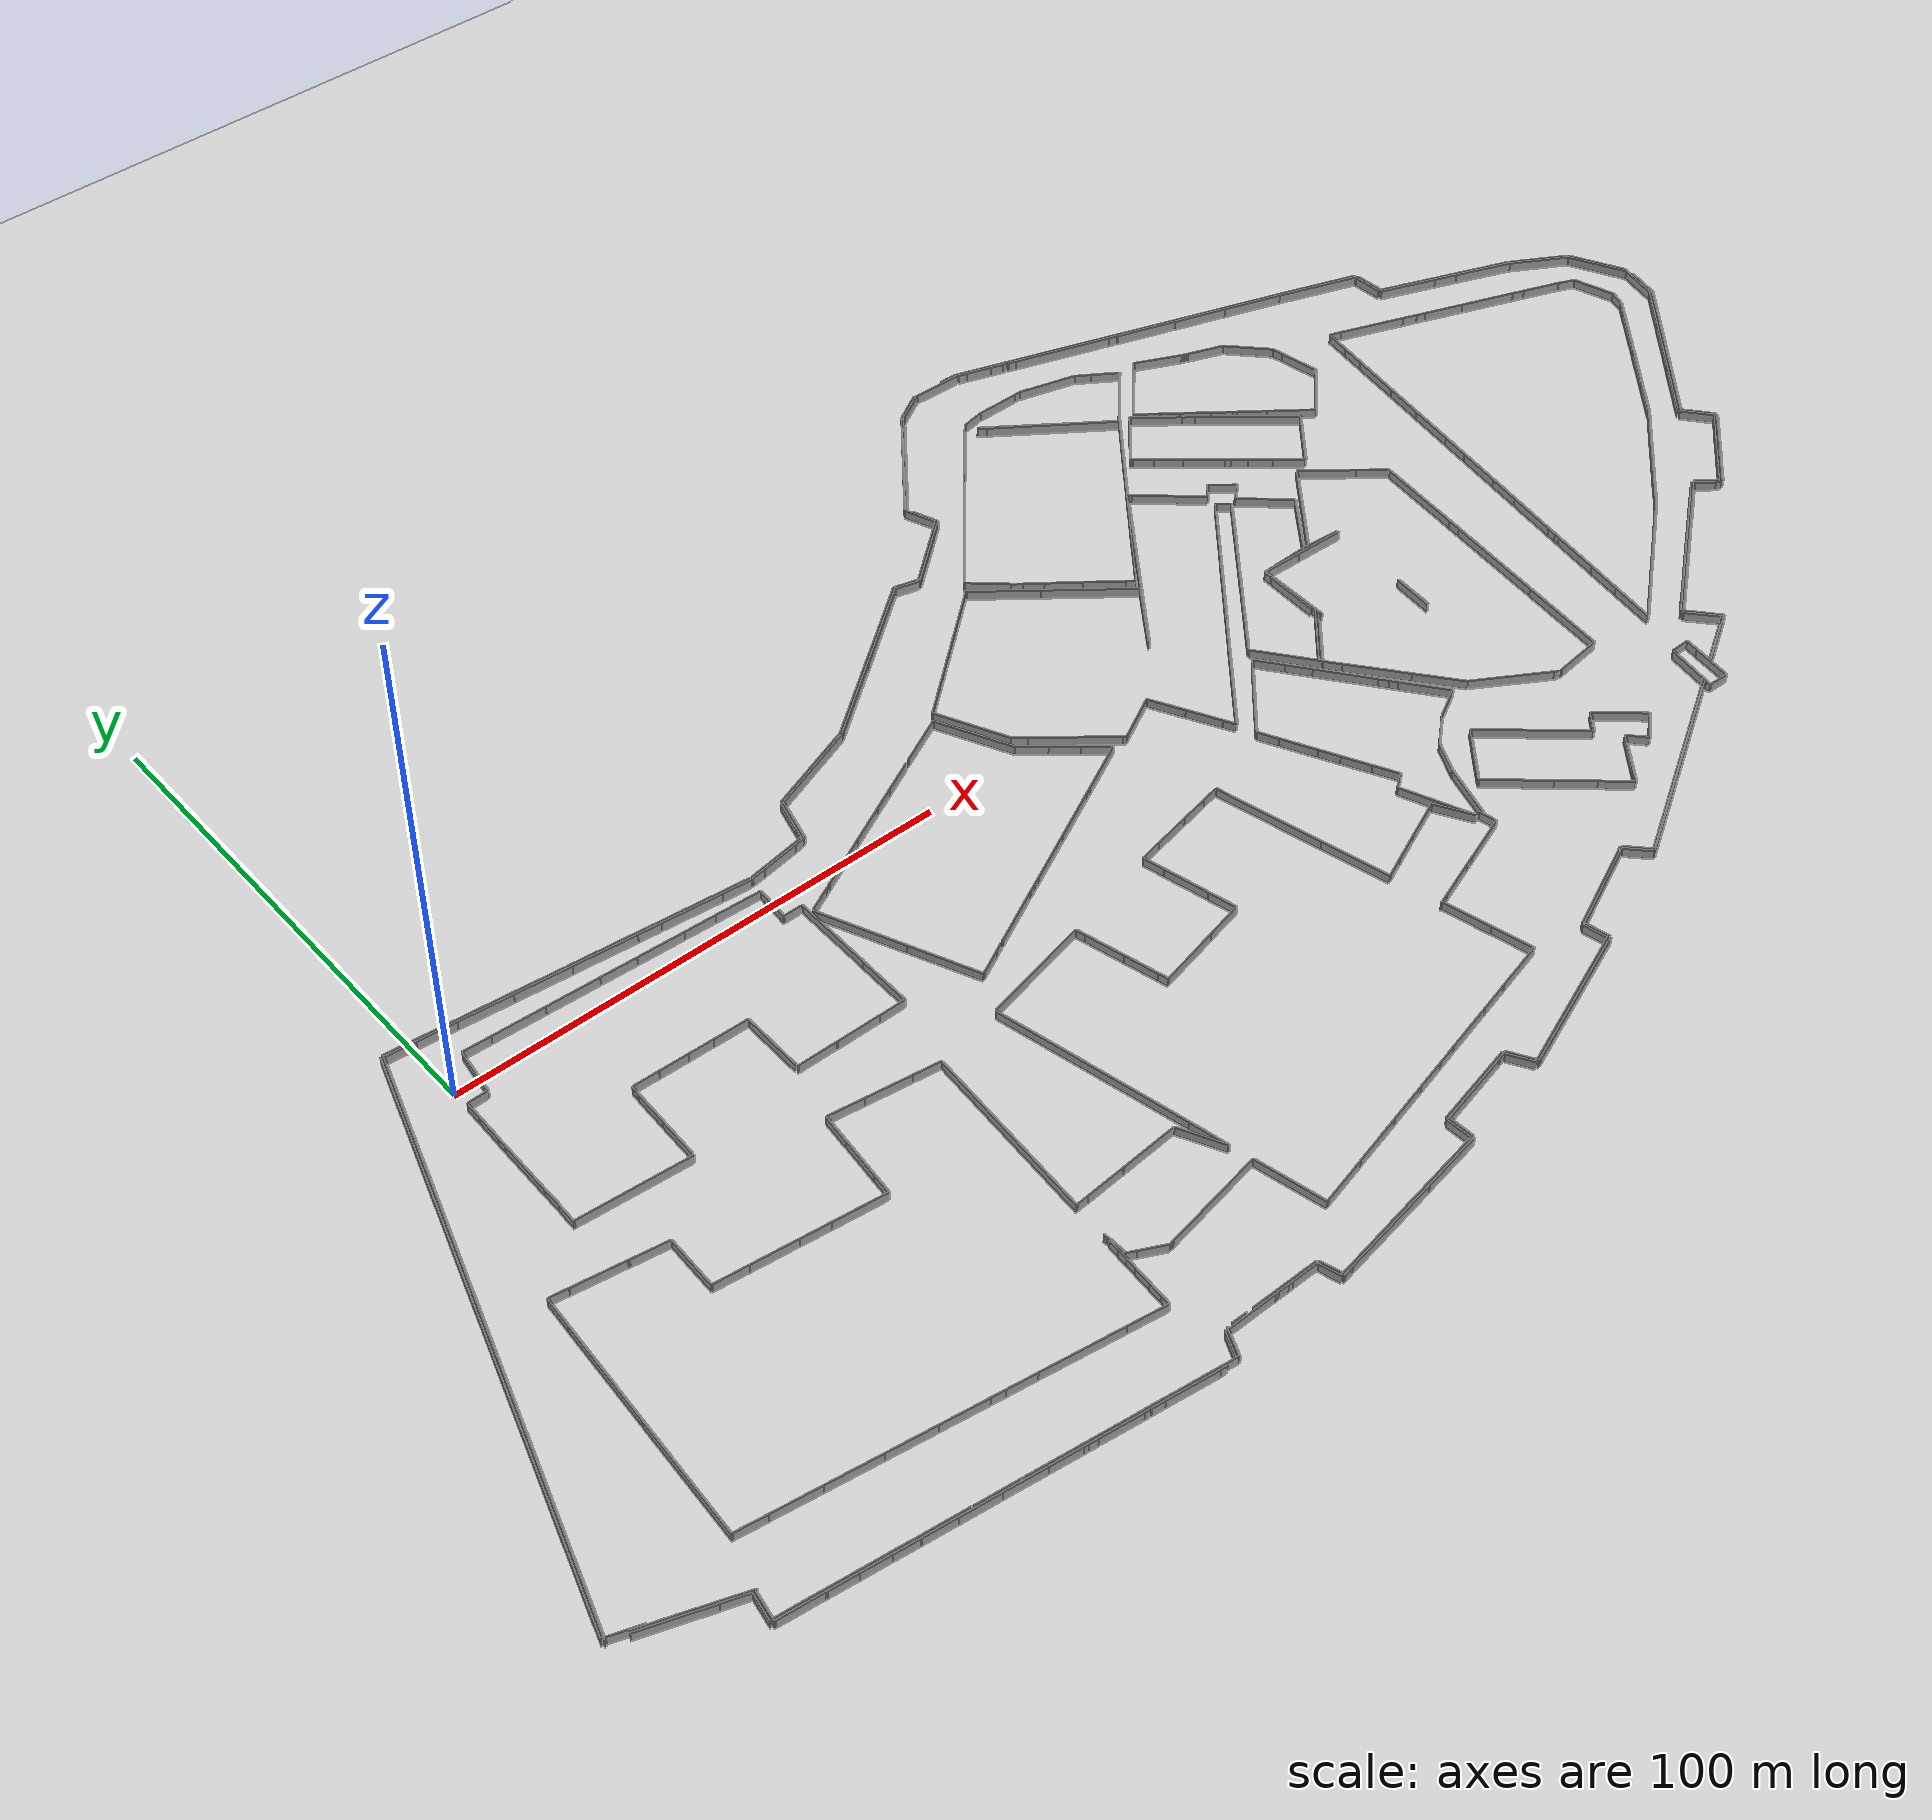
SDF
<sdf version="1.7">
 <world name="slam_world">
  <light name="sun" type="directional">
   <pose>0 0 10 0 -0 0</pose>
   <diffuse>0.8 0.8 0.8 1</diffuse>
   <direction>-0.5 0.1 -0.9</direction>
   <attenuation><range>10</range></attenuation>
   <spot><inner_angle>0</inner_angle><outer_angle>0</outer_angle><falloff>0</falloff></spot>
  </light>
  <model name="ground_plane">
   <static>1</static>
   <link name="link">
    <collision name="collision">
     <geometry><plane><normal>0 0 1</normal><size>100 100</size></plane></geometry>
    </collision>
    <visual name="visual">
     <geometry><plane><normal>0 0 1</normal><size>100 100</size></plane></geometry>
     <material>
      <ambient>0.8 0.8 0.8 1</ambient>
      <diffuse>0.8 0.8 0.8 1</diffuse>
      <specular>0.8 0.8 0.8 1</specular>
     </material>
    </visual>
   </link>
  </model>
  <model name="wall_0">
   <static>1</static>
   <pose>-15.824 -19.025 1 0 -0 1.25765</pose>
   <link name="link">
    <collision name="collision"><geometry><box><size>40.4154 0.2 2</size></box></geometry></collision>
    <visual name="visual">
     <geometry><box><size>40.4154 0.2 2</size></box></geometry>
     <material><ambient>0.5 0.5 0.5 1</ambient><diffuse>0.7 0.7 0.7 1</diffuse></material>
    </visual>
   </link>
  </model>
  <model name="wall_1">
   <static>1</static>
   <pose>63.051 -64.125 1 0 -0 1.50137</pose>
   <link name="link">
    <collision name="collision"><geometry><box><size>36.0368 0.2 2</size></box></geometry></collision>
    <visual name="visual">
     <geometry><box><size>36.0368 0.2 2</size></box></geometry>
     <material><ambient>0.5 0.5 0.5 1</ambient><diffuse>0.7 0.7 0.7 1</diffuse></material>
    </visual>
   </link>
  </model>
  <model name="wall_2">
   <static>1</static>
   <pose>115.076 35.5 1 0 -0 0.645263</pose>
   <link name="link">
    <collision name="collision"><geometry><box><size>39.7401 0.2 2</size></box></geometry></collision>
    <visual name="visual">
     <geometry><box><size>39.7401 0.2 2</size></box></geometry>
     <material><ambient>0.5 0.5 0.5 1</ambient><diffuse>0.7 0.7 0.7 1</diffuse></material>
    </visual>
   </link>
  </model>
  <model name="wall_3">
   <static>1</static>
   <pose>155.401 56.975 1 0 -0 0.872171</pose>
   <link name="link">
    <collision name="collision"><geometry><box><size>44.4675 0.2 2</size></box></geometry></collision>
    <visual name="visual">
     <geometry><box><size>44.4675 0.2 2</size></box></geometry>
     <material><ambient>0.5 0.5 0.5 1</ambient><diffuse>0.7 0.7 0.7 1</diffuse></material>
    </visual>
   </link>
  </model>
  <model name="wall_4">
   <static>1</static>
   <pose>154.201 73.825 1 0 -0 0.907997</pose>
   <link name="link">
    <collision name="collision"><geometry><box><size>27.4651 0.2 2</size></box></geometry></collision>
    <visual name="visual">
     <geometry><box><size>27.4651 0.2 2</size></box></geometry>
     <material><ambient>0.5 0.5 0.5 1</ambient><diffuse>0.7 0.7 0.7 1</diffuse></material>
    </visual>
   </link>
  </model>
  <model name="wall_5">
   <static>1</static>
   <pose>182.226 86.725 1 0 -0 0.661043</pose>
   <link name="link">
    <collision name="collision"><geometry><box><size>0.570088 0.2 2</size></box></geometry></collision>
    <visual name="visual">
     <geometry><box><size>0.570088 0.2 2</size></box></geometry>
     <material><ambient>0.5 0.5 0.5 1</ambient><diffuse>0.7 0.7 0.7 1</diffuse></material>
    </visual>
   </link>
  </model>
  <model name="wall_6">
   <static>1</static>
   <pose>82.851 -64.275 1 0 0 -1.34478</pose>
   <link name="link">
    <collision name="collision"><geometry><box><size>42.8395 0.2 2</size></box></geometry></collision>
    <visual name="visual">
     <geometry><box><size>42.8395 0.2 2</size></box></geometry>
     <material><ambient>0.5 0.5 0.5 1</ambient><diffuse>0.7 0.7 0.7 1</diffuse></material>
    </visual>
   </link>
  </model>
  <model name="wall_7">
   <static>1</static>
   <pose>113.851 35.2 1 0 -0 0.644967</pose>
   <link name="link">
    <collision name="collision"><geometry><box><size>40.92 0.2 2</size></box></geometry></collision>
    <visual name="visual">
     <geometry><box><size>40.92 0.2 2</size></box></geometry>
     <material><ambient>0.5 0.5 0.5 1</ambient><diffuse>0.7 0.7 0.7 1</diffuse></material>
    </visual>
   </link>
  </model>
  <model name="wall_8">
   <static>1</static>
   <pose>-26.474 -53.675 1 0 -0 1.25765</pose>
   <link name="link">
    <collision name="collision"><geometry><box><size>40.4154 0.2 2</size></box></geometry></collision>
    <visual name="visual">
     <geometry><box><size>40.4154 0.2 2</size></box></geometry>
     <material><ambient>0.5 0.5 0.5 1</ambient><diffuse>0.7 0.7 0.7 1</diffuse></material>
    </visual>
   </link>
  </model>
  <model name="wall_9">
   <static>1</static>
   <pose>78.951 -95.15 1 0 -0 0.189988</pose>
   <link name="link">
    <collision name="collision"><geometry><box><size>21.1811 0.2 2</size></box></geometry></collision>
    <visual name="visual">
     <geometry><box><size>21.1811 0.2 2</size></box></geometry>
     <material><ambient>0.5 0.5 0.5 1</ambient><diffuse>0.7 0.7 0.7 1</diffuse></material>
    </visual>
   </link>
  </model>
  <model name="wall_10">
   <static>1</static>
   <pose>183.101 64.65 1 0 0 -0.611022</pose>
   <link name="link">
    <collision name="collision"><geometry><box><size>27.7146 0.2 2</size></box></geometry></collision>
    <visual name="visual">
     <geometry><box><size>27.7146 0.2 2</size></box></geometry>
     <material><ambient>0.5 0.5 0.5 1</ambient><diffuse>0.7 0.7 0.7 1</diffuse></material>
    </visual>
   </link>
  </model>
  <model name="wall_11">
   <static>1</static>
   <pose>-23.274 -42.125 1 0 -0 1.25765</pose>
   <link name="link">
    <collision name="collision"><geometry><box><size>40.4154 0.2 2</size></box></geometry></collision>
    <visual name="visual">
     <geometry><box><size>40.4154 0.2 2</size></box></geometry>
     <material><ambient>0.5 0.5 0.5 1</ambient><diffuse>0.7 0.7 0.7 1</diffuse></material>
    </visual>
   </link>
  </model>
  <model name="wall_12">
   <static>1</static>
   <pose>168.326 -2.675 1 0 -0 0.889225</pose>
   <link name="link">
    <collision name="collision"><geometry><box><size>42.3006 0.2 2</size></box></geometry></collision>
    <visual name="visual">
     <geometry><box><size>42.3006 0.2 2</size></box></geometry>
     <material><ambient>0.5 0.5 0.5 1</ambient><diffuse>0.7 0.7 0.7 1</diffuse></material>
    </visual>
   </link>
  </model>
  <model name="wall_13">
   <static>1</static>
   <pose>-18.774 -29.8 1 0 -0 1.25761</pose>
   <link name="link">
    <collision name="collision"><geometry><box><size>38.7868 0.2 2</size></box></geometry></collision>
    <visual name="visual">
     <geometry><box><size>38.7868 0.2 2</size></box></geometry>
     <material><ambient>0.5 0.5 0.5 1</ambient><diffuse>0.7 0.7 0.7 1</diffuse></material>
    </visual>
   </link>
  </model>
  <model name="wall_14">
   <static>1</static>
   <pose>68.151 -12.6 1 0 -0 1.5708</pose>
   <link name="link">
    <collision name="collision"><geometry><box><size>16.4 0.2 2</size></box></geometry></collision>
    <visual name="visual">
     <geometry><box><size>16.4 0.2 2</size></box></geometry>
     <material><ambient>0.5 0.5 0.5 1</ambient><diffuse>0.7 0.7 0.7 1</diffuse></material>
    </visual>
   </link>
  </model>
  <model name="wall_15">
   <static>1</static>
   <pose>253.476 62.9 1 0 0 -0.331017</pose>
   <link name="link">
    <collision name="collision"><geometry><box><size>18.7689 0.2 2</size></box></geometry></collision>
    <visual name="visual">
     <geometry><box><size>18.7689 0.2 2</size></box></geometry>
     <material><ambient>0.5 0.5 0.5 1</ambient><diffuse>0.7 0.7 0.7 1</diffuse></material>
    </visual>
   </link>
  </model>
  <model name="wall_16">
   <static>1</static>
   <pose>-0.999 -112.875 1 0 0 -0.109089</pose>
   <link name="link">
    <collision name="collision"><geometry><box><size>10.5628 0.2 2</size></box></geometry></collision>
    <visual name="visual">
     <geometry><box><size>10.5628 0.2 2</size></box></geometry>
     <material><ambient>0.5 0.5 0.5 1</ambient><diffuse>0.7 0.7 0.7 1</diffuse></material>
    </visual>
   </link>
  </model>
  <model name="wall_17">
   <static>1</static>
   <pose>155.026 74.05 1 0 -0 0.907765</pose>
   <link name="link">
    <collision name="collision"><geometry><box><size>28.6755 0.2 2</size></box></geometry></collision>
    <visual name="visual">
     <geometry><box><size>28.6755 0.2 2</size></box></geometry>
     <material><ambient>0.5 0.5 0.5 1</ambient><diffuse>0.7 0.7 0.7 1</diffuse></material>
    </visual>
   </link>
  </model>
  <model name="wall_18">
   <static>1</static>
   <pose>89.076 -40.8 1 0 -0 0.228296</pose>
   <link name="link">
    <collision name="collision"><geometry><box><size>22.5347 0.2 2</size></box></geometry></collision>
    <visual name="visual">
     <geometry><box><size>22.5347 0.2 2</size></box></geometry>
     <material><ambient>0.5 0.5 0.5 1</ambient><diffuse>0.7 0.7 0.7 1</diffuse></material>
    </visual>
   </link>
  </model>
  <model name="wall_19">
   <static>1</static>
   <pose>-10.249 -1.775 1 0 -0 1.25668</pose>
   <link name="link">
    <collision name="collision"><geometry><box><size>31.0703 0.2 2</size></box></geometry></collision>
    <visual name="visual">
     <geometry><box><size>31.0703 0.2 2</size></box></geometry>
     <material><ambient>0.5 0.5 0.5 1</ambient><diffuse>0.7 0.7 0.7 1</diffuse></material>
    </visual>
   </link>
  </model>
  <model name="wall_20">
   <static>1</static>
   <pose>-34.974 -80 1 0 -0 1.25707</pose>
   <link name="link">
    <collision name="collision"><geometry><box><size>37.4268 0.2 2</size></box></geometry></collision>
    <visual name="visual">
     <geometry><box><size>37.4268 0.2 2</size></box></geometry>
     <material><ambient>0.5 0.5 0.5 1</ambient><diffuse>0.7 0.7 0.7 1</diffuse></material>
    </visual>
   </link>
  </model>
  <model name="wall_21">
   <static>1</static>
   <pose>257.001 -26.325 1 0 -0 0.741947</pose>
   <link name="link">
    <collision name="collision"><geometry><box><size>0.813941 0.2 2</size></box></geometry></collision>
    <visual name="visual">
     <geometry><box><size>0.813941 0.2 2</size></box></geometry>
     <material><ambient>0.5 0.5 0.5 1</ambient><diffuse>0.7 0.7 0.7 1</diffuse></material>
    </visual>
   </link>
  </model>
  <model name="wall_22">
   <static>1</static>
   <pose>267.626 -15.625 1 0 -0 0.785398</pose>
   <link name="link">
    <collision name="collision"><geometry><box><size>22.8395 0.2 2</size></box></geometry></collision>
    <visual name="visual">
     <geometry><box><size>22.8395 0.2 2</size></box></geometry>
     <material><ambient>0.5 0.5 0.5 1</ambient><diffuse>0.7 0.7 0.7 1</diffuse></material>
    </visual>
   </link>
  </model>
  <model name="wall_23">
   <static>1</static>
   <pose>173.651 -12.075 1 0 0 -0.908779</pose>
   <link name="link">
    <collision name="collision"><geometry><box><size>13.5023 0.2 2</size></box></geometry></collision>
    <visual name="visual">
     <geometry><box><size>13.5023 0.2 2</size></box></geometry>
     <material><ambient>0.5 0.5 0.5 1</ambient><diffuse>0.7 0.7 0.7 1</diffuse></material>
    </visual>
   </link>
  </model>
  <model name="wall_24">
   <static>1</static>
   <pose>206.051 -78 1 0 -0 0.539799</pose>
   <link name="link">
    <collision name="collision"><geometry><box><size>27.6284 0.2 2</size></box></geometry></collision>
    <visual name="visual">
     <geometry><box><size>27.6284 0.2 2</size></box></geometry>
     <material><ambient>0.5 0.5 0.5 1</ambient><diffuse>0.7 0.7 0.7 1</diffuse></material>
    </visual>
   </link>
  </model>
  <model name="wall_25">
   <static>1</static>
   <pose>199.426 -81.375 1 0 -0 0.539749</pose>
   <link name="link">
    <collision name="collision"><geometry><box><size>25.5876 0.2 2</size></box></geometry></collision>
    <visual name="visual">
     <geometry><box><size>25.5876 0.2 2</size></box></geometry>
     <material><ambient>0.5 0.5 0.5 1</ambient><diffuse>0.7 0.7 0.7 1</diffuse></material>
    </visual>
   </link>
  </model>
  <model name="wall_26">
   <static>1</static>
   <pose>150.051 -104 1 0 -0 0.364735</pose>
   <link name="link">
    <collision name="collision"><geometry><box><size>23.5491 0.2 2</size></box></geometry></collision>
    <visual name="visual">
     <geometry><box><size>23.5491 0.2 2</size></box></geometry>
     <material><ambient>0.5 0.5 0.5 1</ambient><diffuse>0.7 0.7 0.7 1</diffuse></material>
    </visual>
   </link>
  </model>
  <model name="wall_27">
   <static>1</static>
   <pose>298.151 10.8 1 0 -0 0.889595</pose>
   <link name="link">
    <collision name="collision"><geometry><box><size>21.7555 0.2 2</size></box></geometry></collision>
    <visual name="visual">
     <geometry><box><size>21.7555 0.2 2</size></box></geometry>
     <material><ambient>0.5 0.5 0.5 1</ambient><diffuse>0.7 0.7 0.7 1</diffuse></material>
    </visual>
   </link>
  </model>
  <model name="wall_28">
   <static>1</static>
   <pose>151.576 29.1 1 0 0 -0.664518</pose>
   <link name="link">
    <collision name="collision"><geometry><box><size>29.0264 0.2 2</size></box></geometry></collision>
    <visual name="visual">
     <geometry><box><size>29.0264 0.2 2</size></box></geometry>
     <material><ambient>0.5 0.5 0.5 1</ambient><diffuse>0.7 0.7 0.7 1</diffuse></material>
    </visual>
   </link>
  </model>
  <model name="wall_29">
   <static>1</static>
   <pose>73.451 -114.725 1 0 -0 0.017325</pose>
   <link name="link">
    <collision name="collision"><geometry><box><size>20.203 0.2 2</size></box></geometry></collision>
    <visual name="visual">
     <geometry><box><size>20.203 0.2 2</size></box></geometry>
     <material><ambient>0.5 0.5 0.5 1</ambient><diffuse>0.7 0.7 0.7 1</diffuse></material>
    </visual>
   </link>
  </model>
  <model name="wall_30">
   <static>1</static>
   <pose>75.276 -21.125 1 0 0 -1.15241</pose>
   <link name="link">
    <collision name="collision"><geometry><box><size>32.1205 0.2 2</size></box></geometry></collision>
    <visual name="visual">
     <geometry><box><size>32.1205 0.2 2</size></box></geometry>
     <material><ambient>0.5 0.5 0.5 1</ambient><diffuse>0.7 0.7 0.7 1</diffuse></material>
    </visual>
   </link>
  </model>
  <model name="wall_31">
   <static>1</static>
   <pose>76.326 -114.2 1 0 -0 0.014651</pose>
   <link name="link">
    <collision name="collision"><geometry><box><size>13.6515 0.2 2</size></box></geometry></collision>
    <visual name="visual">
     <geometry><box><size>13.6515 0.2 2</size></box></geometry>
     <material><ambient>0.5 0.5 0.5 1</ambient><diffuse>0.7 0.7 0.7 1</diffuse></material>
    </visual>
   </link>
  </model>
  <model name="wall_32">
   <static>1</static>
   <pose>203.951 15.075 1 0 -0 0.907209</pose>
   <link name="link">
    <collision name="collision"><geometry><box><size>22.4045 0.2 2</size></box></geometry></collision>
    <visual name="visual">
     <geometry><box><size>22.4045 0.2 2</size></box></geometry>
     <material><ambient>0.5 0.5 0.5 1</ambient><diffuse>0.7 0.7 0.7 1</diffuse></material>
    </visual>
   </link>
  </model>
  <model name="wall_33">
   <static>1</static>
   <pose>200.326 12.05 1 0 -0 0.924542</pose>
   <link name="link">
    <collision name="collision"><geometry><box><size>14.5301 0.2 2</size></box></geometry></collision>
    <visual name="visual">
     <geometry><box><size>14.5301 0.2 2</size></box></geometry>
     <material><ambient>0.5 0.5 0.5 1</ambient><diffuse>0.7 0.7 0.7 1</diffuse></material>
    </visual>
   </link>
  </model>
  <model name="wall_34">
   <static>1</static>
   <pose>180.451 38.5 1 0 -0 0.909025</pose>
   <link name="link">
    <collision name="collision"><geometry><box><size>24.084 0.2 2</size></box></geometry></collision>
    <visual name="visual">
     <geometry><box><size>24.084 0.2 2</size></box></geometry>
     <material><ambient>0.5 0.5 0.5 1</ambient><diffuse>0.7 0.7 0.7 1</diffuse></material>
    </visual>
   </link>
  </model>
  <model name="wall_35">
   <static>1</static>
   <pose>-6.724 -112.225 1 0 0 -0.108382</pose>
   <link name="link">
    <collision name="collision"><geometry><box><size>9.70696 0.2 2</size></box></geometry></collision>
    <visual name="visual">
     <geometry><box><size>9.70696 0.2 2</size></box></geometry>
     <material><ambient>0.5 0.5 0.5 1</ambient><diffuse>0.7 0.7 0.7 1</diffuse></material>
    </visual>
   </link>
  </model>
  <model name="wall_36">
   <static>1</static>
   <pose>218.126 -70.8 1 0 -0 0.540019</pose>
   <link name="link">
    <collision name="collision"><geometry><box><size>21.3944 0.2 2</size></box></geometry></collision>
    <visual name="visual">
     <geometry><box><size>21.3944 0.2 2</size></box></geometry>
     <material><ambient>0.5 0.5 0.5 1</ambient><diffuse>0.7 0.7 0.7 1</diffuse></material>
    </visual>
   </link>
  </model>
  <model name="wall_37">
   <static>1</static>
   <pose>202.376 51.8 1 0 0 -0.682488</pose>
   <link name="link">
    <collision name="collision"><geometry><box><size>14.1107 0.2 2</size></box></geometry></collision>
    <visual name="visual">
     <geometry><box><size>14.1107 0.2 2</size></box></geometry>
     <material><ambient>0.5 0.5 0.5 1</ambient><diffuse>0.7 0.7 0.7 1</diffuse></material>
    </visual>
   </link>
  </model>
  <model name="wall_38">
   <static>1</static>
   <pose>214.651 41.75 1 0 0 -0.682317</pose>
   <link name="link">
    <collision name="collision"><geometry><box><size>20.6155 0.2 2</size></box></geometry></collision>
    <visual name="visual">
     <geometry><box><size>20.6155 0.2 2</size></box></geometry>
     <material><ambient>0.5 0.5 0.5 1</ambient><diffuse>0.7 0.7 0.7 1</diffuse></material>
    </visual>
   </link>
  </model>
  <model name="wall_39">
   <static>1</static>
   <pose>281.976 0.35 1 0 -0 0.905735</pose>
   <link name="link">
    <collision name="collision"><geometry><box><size>18.5543 0.2 2</size></box></geometry></collision>
    <visual name="visual">
     <geometry><box><size>18.5543 0.2 2</size></box></geometry>
     <material><ambient>0.5 0.5 0.5 1</ambient><diffuse>0.7 0.7 0.7 1</diffuse></material>
    </visual>
   </link>
  </model>
  <model name="wall_40">
   <static>1</static>
   <pose>230.551 71.075 1 0 0 -0.316411</pose>
   <link name="link">
    <collision name="collision"><geometry><box><size>20.729 0.2 2</size></box></geometry></collision>
    <visual name="visual">
     <geometry><box><size>20.729 0.2 2</size></box></geometry>
     <material><ambient>0.5 0.5 0.5 1</ambient><diffuse>0.7 0.7 0.7 1</diffuse></material>
    </visual>
   </link>
  </model>
  <model name="wall_41">
   <static>1</static>
   <pose>38.726 -117.4 1 0 0 -0.11768</pose>
   <link name="link">
    <collision name="collision"><geometry><box><size>10.2207 0.2 2</size></box></geometry></collision>
    <visual name="visual">
     <geometry><box><size>10.2207 0.2 2</size></box></geometry>
     <material><ambient>0.5 0.5 0.5 1</ambient><diffuse>0.7 0.7 0.7 1</diffuse></material>
    </visual>
   </link>
  </model>
  <model name="wall_42">
   <static>1</static>
   <pose>141.926 51.1 1 0 -0 0.681298</pose>
   <link name="link">
    <collision name="collision"><geometry><box><size>16.6719 0.2 2</size></box></geometry></collision>
    <visual name="visual">
     <geometry><box><size>16.6719 0.2 2</size></box></geometry>
     <material><ambient>0.5 0.5 0.5 1</ambient><diffuse>0.7 0.7 0.7 1</diffuse></material>
    </visual>
   </link>
  </model>
  <model name="wall_43">
   <static>1</static>
   <pose>182.876 -61.05 1 0 0 -0.71275</pose>
   <link name="link">
    <collision name="collision"><geometry><box><size>13.1515 0.2 2</size></box></geometry></collision>
    <visual name="visual">
     <geometry><box><size>13.1515 0.2 2</size></box></geometry>
     <material><ambient>0.5 0.5 0.5 1</ambient><diffuse>0.7 0.7 0.7 1</diffuse></material>
    </visual>
   </link>
  </model>
  <model name="wall_44">
   <static>1</static>
   <pose>-29.974 -62.9 1 0 -0 1.25761</pose>
   <link name="link">
    <collision name="collision"><geometry><box><size>38.7868 0.2 2</size></box></geometry></collision>
    <visual name="visual">
     <geometry><box><size>38.7868 0.2 2</size></box></geometry>
     <material><ambient>0.5 0.5 0.5 1</ambient><diffuse>0.7 0.7 0.7 1</diffuse></material>
    </visual>
   </link>
  </model>
  <model name="wall_45">
   <static>1</static>
   <pose>153.326 -102.225 1 0 -0 0.36672</pose>
   <link name="link">
    <collision name="collision"><geometry><box><size>31.6548 0.2 2</size></box></geometry></collision>
    <visual name="visual">
     <geometry><box><size>31.6548 0.2 2</size></box></geometry>
     <material><ambient>0.5 0.5 0.5 1</ambient><diffuse>0.7 0.7 0.7 1</diffuse></material>
    </visual>
   </link>
  </model>
  <model name="wall_46">
   <static>1</static>
   <pose>181.951 -11.775 1 0 -0 0.855778</pose>
   <link name="link">
    <collision name="collision"><geometry><box><size>13.5747 0.2 2</size></box></geometry></collision>
    <visual name="visual">
     <geometry><box><size>13.5747 0.2 2</size></box></geometry>
     <material><ambient>0.5 0.5 0.5 1</ambient><diffuse>0.7 0.7 0.7 1</diffuse></material>
    </visual>
   </link>
  </model>
  <model name="wall_47">
   <static>1</static>
   <pose>175.776 -87.725 1 0 -0 0.419509</pose>
   <link name="link">
    <collision name="collision"><geometry><box><size>19.7637 0.2 2</size></box></geometry></collision>
    <visual name="visual">
     <geometry><box><size>19.7637 0.2 2</size></box></geometry>
     <material><ambient>0.5 0.5 0.5 1</ambient><diffuse>0.7 0.7 0.7 1</diffuse></material>
    </visual>
   </link>
  </model>
  <model name="wall_48">
   <static>1</static>
   <pose>91.026 -99.975 1 0 0 -1.344</pose>
   <link name="link">
    <collision name="collision"><geometry><box><size>14.0087 0.2 2</size></box></geometry></collision>
    <visual name="visual">
     <geometry><box><size>14.0087 0.2 2</size></box></geometry>
     <material><ambient>0.5 0.5 0.5 1</ambient><diffuse>0.7 0.7 0.7 1</diffuse></material>
    </visual>
   </link>
  </model>
  <model name="wall_49">
   <static>1</static>
   <pose>193.976 -54.1 1 0 0 -0.715593</pose>
   <link name="link">
    <collision name="collision"><geometry><box><size>21.7966 0.2 2</size></box></geometry></collision>
    <visual name="visual">
     <geometry><box><size>21.7966 0.2 2</size></box></geometry>
     <material><ambient>0.5 0.5 0.5 1</ambient><diffuse>0.7 0.7 0.7 1</diffuse></material>
    </visual>
   </link>
  </model>
  <model name="wall_50">
   <static>1</static>
   <pose>200.851 80.325 1 0 0 -0.316411</pose>
   <link name="link">
    <collision name="collision"><geometry><box><size>20.729 0.2 2</size></box></geometry></collision>
    <visual name="visual">
     <geometry><box><size>20.729 0.2 2</size></box></geometry>
     <material><ambient>0.5 0.5 0.5 1</ambient><diffuse>0.7 0.7 0.7 1</diffuse></material>
    </visual>
   </link>
  </model>
  <model name="wall_51">
   <static>1</static>
   <pose>129.226 -2.575 1 0 0 -0.679039</pose>
   <link name="link">
    <collision name="collision"><geometry><box><size>19.9826 0.2 2</size></box></geometry></collision>
    <visual name="visual">
     <geometry><box><size>19.9826 0.2 2</size></box></geometry>
     <material><ambient>0.5 0.5 0.5 1</ambient><diffuse>0.7 0.7 0.7 1</diffuse></material>
    </visual>
   </link>
  </model>
  <model name="wall_52">
   <static>1</static>
   <pose>254.151 63.225 1 0 0 -0.330217</pose>
   <link name="link">
    <collision name="collision"><geometry><box><size>16.8081 0.2 2</size></box></geometry></collision>
    <visual name="visual">
     <geometry><box><size>16.8081 0.2 2</size></box></geometry>
     <material><ambient>0.5 0.5 0.5 1</ambient><diffuse>0.7 0.7 0.7 1</diffuse></material>
    </visual>
   </link>
  </model>
  <model name="wall_53">
   <static>1</static>
   <pose>-37.724 -86.975 1 0 -0 1.25809</pose>
   <link name="link">
    <collision name="collision"><geometry><box><size>20.9668 0.2 2</size></box></geometry></collision>
    <visual name="visual">
     <geometry><box><size>20.9668 0.2 2</size></box></geometry>
     <material><ambient>0.5 0.5 0.5 1</ambient><diffuse>0.7 0.7 0.7 1</diffuse></material>
    </visual>
   </link>
  </model>
  <model name="wall_54">
   <static>1</static>
   <pose>274.076 -27.625 1 0 -0 0.785398</pose>
   <link name="link">
    <collision name="collision"><geometry><box><size>7.56604 0.2 2</size></box></geometry></collision>
    <visual name="visual">
     <geometry><box><size>7.56604 0.2 2</size></box></geometry>
     <material><ambient>0.5 0.5 0.5 1</ambient><diffuse>0.7 0.7 0.7 1</diffuse></material>
    </visual>
   </link>
  </model>
  <model name="wall_55">
   <static>1</static>
   <pose>295.276 6.475 1 0 -0 0.888581</pose>
   <link name="link">
    <collision name="collision"><geometry><box><size>24.028 0.2 2</size></box></geometry></collision>
    <visual name="visual">
     <geometry><box><size>24.028 0.2 2</size></box></geometry>
     <material><ambient>0.5 0.5 0.5 1</ambient><diffuse>0.7 0.7 0.7 1</diffuse></material>
    </visual>
   </link>
  </model>
  <model name="wall_56">
   <static>1</static>
   <pose>181.751 -51.85 1 0 -0 0.88848</pose>
   <link name="link">
    <collision name="collision"><geometry><box><size>12.3693 0.2 2</size></box></geometry></collision>
    <visual name="visual">
     <geometry><box><size>12.3693 0.2 2</size></box></geometry>
     <material><ambient>0.5 0.5 0.5 1</ambient><diffuse>0.7 0.7 0.7 1</diffuse></material>
    </visual>
   </link>
  </model>
  <model name="wall_57">
   <static>1</static>
   <pose>186.926 34.275 1 0 0 -0.715419</pose>
   <link name="link">
    <collision name="collision"><geometry><box><size>15.1692 0.2 2</size></box></geometry></collision>
    <visual name="visual">
     <geometry><box><size>15.1692 0.2 2</size></box></geometry>
     <material><ambient>0.5 0.5 0.5 1</ambient><diffuse>0.7 0.7 0.7 1</diffuse></material>
    </visual>
   </link>
  </model>
  <model name="wall_58">
   <static>1</static>
   <pose>71.951 7.25 1 0 -0 0.153814</pose>
   <link name="link">
    <collision name="collision"><geometry><box><size>13.0541 0.2 2</size></box></geometry></collision>
    <visual name="visual">
     <geometry><box><size>13.0541 0.2 2</size></box></geometry>
     <material><ambient>0.5 0.5 0.5 1</ambient><diffuse>0.7 0.7 0.7 1</diffuse></material>
    </visual>
   </link>
  </model>
  <model name="wall_59">
   <static>1</static>
   <pose>95.001 -116.575 1 0 -0 0.176388</pose>
   <link name="link">
    <collision name="collision"><geometry><box><size>21.9404 0.2 2</size></box></geometry></collision>
    <visual name="visual">
     <geometry><box><size>21.9404 0.2 2</size></box></geometry>
     <material><ambient>0.5 0.5 0.5 1</ambient><diffuse>0.7 0.7 0.7 1</diffuse></material>
    </visual>
   </link>
  </model>
  <model name="wall_60">
   <static>1</static>
   <pose>221.651 -20.05 1 0 -0 1.4816</pose>
   <link name="link">
    <collision name="collision"><geometry><box><size>24.6982 0.2 2</size></box></geometry></collision>
    <visual name="visual">
     <geometry><box><size>24.6982 0.2 2</size></box></geometry>
     <material><ambient>0.5 0.5 0.5 1</ambient><diffuse>0.7 0.7 0.7 1</diffuse></material>
    </visual>
   </link>
  </model>
  <model name="wall_61">
   <static>1</static>
   <pose>141.601 51.45 1 0 -0 0.680941</pose>
   <link name="link">
    <collision name="collision"><geometry><box><size>17.6324 0.2 2</size></box></geometry></collision>
    <visual name="visual">
     <geometry><box><size>17.6324 0.2 2</size></box></geometry>
     <material><ambient>0.5 0.5 0.5 1</ambient><diffuse>0.7 0.7 0.7 1</diffuse></material>
    </visual>
   </link>
  </model>
  <model name="wall_62">
   <static>1</static>
   <pose>277.051 -24 1 0 -0 0.785398</pose>
   <link name="link">
    <collision name="collision"><geometry><box><size>11.4551 0.2 2</size></box></geometry></collision>
    <visual name="visual">
     <geometry><box><size>11.4551 0.2 2</size></box></geometry>
     <material><ambient>0.5 0.5 0.5 1</ambient><diffuse>0.7 0.7 0.7 1</diffuse></material>
    </visual>
   </link>
  </model>
  <model name="wall_63">
   <static>1</static>
   <pose>180.026 -24.325 1 0 0 -0.909753</pose>
   <link name="link">
    <collision name="collision"><geometry><box><size>16.5325 0.2 2</size></box></geometry></collision>
    <visual name="visual">
     <geometry><box><size>16.5325 0.2 2</size></box></geometry>
     <material><ambient>0.5 0.5 0.5 1</ambient><diffuse>0.7 0.7 0.7 1</diffuse></material>
    </visual>
   </link>
  </model>
  <model name="wall_64">
   <static>1</static>
   <pose>168.301 -55.525 1 0 0 -1.16917</pose>
   <link name="link">
    <collision name="collision"><geometry><box><size>14.0696 0.2 2</size></box></geometry></collision>
    <visual name="visual">
     <geometry><box><size>14.0696 0.2 2</size></box></geometry>
     <material><ambient>0.5 0.5 0.5 1</ambient><diffuse>0.7 0.7 0.7 1</diffuse></material>
    </visual>
   </link>
  </model>
  <model name="wall_65">
   <static>1</static>
   <pose>280.926 46.4 1 0 0 -0.366185</pose>
   <link name="link">
    <collision name="collision"><geometry><box><size>18.1536 0.2 2</size></box></geometry></collision>
    <visual name="visual">
     <geometry><box><size>18.1536 0.2 2</size></box></geometry>
     <material><ambient>0.5 0.5 0.5 1</ambient><diffuse>0.7 0.7 0.7 1</diffuse></material>
    </visual>
   </link>
  </model>
  <model name="wall_66">
   <static>1</static>
   <pose>187.476 -33.975 1 0 0 -0.907969</pose>
   <link name="link">
    <collision name="collision"><geometry><box><size>9.83184 0.2 2</size></box></geometry></collision>
    <visual name="visual">
     <geometry><box><size>9.83184 0.2 2</size></box></geometry>
     <material><ambient>0.5 0.5 0.5 1</ambient><diffuse>0.7 0.7 0.7 1</diffuse></material>
    </visual>
   </link>
  </model>
  <model name="wall_67">
   <static>1</static>
   <pose>222.651 73.15 1 0 0 -0.31621</pose>
   <link name="link">
    <collision name="collision"><geometry><box><size>22.832 0.2 2</size></box></geometry></collision>
    <visual name="visual">
     <geometry><box><size>22.832 0.2 2</size></box></geometry>
     <material><ambient>0.5 0.5 0.5 1</ambient><diffuse>0.7 0.7 0.7 1</diffuse></material>
    </visual>
   </link>
  </model>
  <model name="wall_68">
   <static>1</static>
   <pose>43.651 -103.35 1 0 0 -0.137066</pose>
   <link name="link">
    <collision name="collision"><geometry><box><size>17.5647 0.2 2</size></box></geometry></collision>
    <visual name="visual">
     <geometry><box><size>17.5647 0.2 2</size></box></geometry>
     <material><ambient>0.5 0.5 0.5 1</ambient><diffuse>0.7 0.7 0.7 1</diffuse></material>
    </visual>
   </link>
  </model>
  <model name="wall_69">
   <static>1</static>
   <pose>176.026 -88.125 1 0 -0 0.418966</pose>
   <link name="link">
    <collision name="collision"><geometry><box><size>20.5252 0.2 2</size></box></geometry></collision>
    <visual name="visual">
     <geometry><box><size>20.5252 0.2 2</size></box></geometry>
     <material><ambient>0.5 0.5 0.5 1</ambient><diffuse>0.7 0.7 0.7 1</diffuse></material>
    </visual>
   </link>
  </model>
  <model name="wall_70">
   <static>1</static>
   <pose>190.401 -67.5 1 0 0 -0.714091</pose>
   <link name="link">
    <collision name="collision"><geometry><box><size>21.8344 0.2 2</size></box></geometry></collision>
    <visual name="visual">
     <geometry><box><size>21.8344 0.2 2</size></box></geometry>
     <material><ambient>0.5 0.5 0.5 1</ambient><diffuse>0.7 0.7 0.7 1</diffuse></material>
    </visual>
   </link>
  </model>
  <model name="wall_71">
   <static>1</static>
   <pose>256.126 -35.8 1 0 -0 0.680714</pose>
   <link name="link">
    <collision name="collision"><geometry><box><size>28.7599 0.2 2</size></box></geometry></collision>
    <visual name="visual">
     <geometry><box><size>28.7599 0.2 2</size></box></geometry>
     <material><ambient>0.5 0.5 0.5 1</ambient><diffuse>0.7 0.7 0.7 1</diffuse></material>
    </visual>
   </link>
  </model>
  <model name="wall_72">
   <static>1</static>
   <pose>198.351 81.675 1 0 0 -0.316411</pose>
   <link name="link">
    <collision name="collision"><geometry><box><size>20.729 0.2 2</size></box></geometry></collision>
    <visual name="visual">
     <geometry><box><size>20.729 0.2 2</size></box></geometry>
     <material><ambient>0.5 0.5 0.5 1</ambient><diffuse>0.7 0.7 0.7 1</diffuse></material>
    </visual>
   </link>
  </model>
  <model name="wall_73">
   <static>1</static>
   <pose>171.551 27 1 0 -0 0.909753</pose>
   <link name="link">
    <collision name="collision"><geometry><box><size>17.1026 0.2 2</size></box></geometry></collision>
    <visual name="visual">
     <geometry><box><size>17.1026 0.2 2</size></box></geometry>
     <material><ambient>0.5 0.5 0.5 1</ambient><diffuse>0.7 0.7 0.7 1</diffuse></material>
    </visual>
   </link>
  </model>
  <model name="wall_74">
   <static>1</static>
   <pose>45.601 -25.075 1 0 -0 1.5708</pose>
   <link name="link">
    <collision name="collision"><geometry><box><size>12.55 0.2 2</size></box></geometry></collision>
    <visual name="visual">
     <geometry><box><size>12.55 0.2 2</size></box></geometry>
     <material><ambient>0.5 0.5 0.5 1</ambient><diffuse>0.7 0.7 0.7 1</diffuse></material>
    </visual>
   </link>
  </model>
  <model name="wall_75">
   <static>1</static>
   <pose>154.301 -81.8 1 0 0 -1.32718</pose>
   <link name="link">
    <collision name="collision"><geometry><box><size>17.8264 0.2 2</size></box></geometry></collision>
    <visual name="visual">
     <geometry><box><size>17.8264 0.2 2</size></box></geometry>
     <material><ambient>0.5 0.5 0.5 1</ambient><diffuse>0.7 0.7 0.7 1</diffuse></material>
    </visual>
   </link>
  </model>
  <model name="wall_76">
   <static>1</static>
   <pose>287.201 -3.425 1 0 -0 0.889813</pose>
   <link name="link">
    <collision name="collision"><geometry><box><size>20.0141 0.2 2</size></box></geometry></collision>
    <visual name="visual">
     <geometry><box><size>20.0141 0.2 2</size></box></geometry>
     <material><ambient>0.5 0.5 0.5 1</ambient><diffuse>0.7 0.7 0.7 1</diffuse></material>
    </visual>
   </link>
  </model>
  <model name="wall_77">
   <static>1</static>
   <pose>194.051 -54.125 1 0 0 -0.715366</pose>
   <link name="link">
    <collision name="collision"><geometry><box><size>21.7261 0.2 2</size></box></geometry></collision>
    <visual name="visual">
     <geometry><box><size>21.7261 0.2 2</size></box></geometry>
     <material><ambient>0.5 0.5 0.5 1</ambient><diffuse>0.7 0.7 0.7 1</diffuse></material>
    </visual>
   </link>
  </model>
  <model name="wall_78">
   <static>1</static>
   <pose>58.126 -31.9 1 0 -0 0</pose>
   <link name="link">
    <collision name="collision"><geometry><box><size>8.85 0.2 2</size></box></geometry></collision>
    <visual name="visual">
     <geometry><box><size>8.85 0.2 2</size></box></geometry>
     <material><ambient>0.5 0.5 0.5 1</ambient><diffuse>0.7 0.7 0.7 1</diffuse></material>
    </visual>
   </link>
  </model>
  <model name="wall_79">
   <static>1</static>
   <pose>-8.849 1 1 0 -0 1.25768</pose>
   <link name="link">
    <collision name="collision"><geometry><box><size>25.647 0.2 2</size></box></geometry></collision>
    <visual name="visual">
     <geometry><box><size>25.647 0.2 2</size></box></geometry>
     <material><ambient>0.5 0.5 0.5 1</ambient><diffuse>0.7 0.7 0.7 1</diffuse></material>
    </visual>
   </link>
  </model>
  <model name="wall_80">
   <static>1</static>
   <pose>162.926 14.75 1 0 -0 0.933726</pose>
   <link name="link">
    <collision name="collision"><geometry><box><size>3.11006 0.2 2</size></box></geometry></collision>
    <visual name="visual">
     <geometry><box><size>3.11006 0.2 2</size></box></geometry>
     <material><ambient>0.5 0.5 0.5 1</ambient><diffuse>0.7 0.7 0.7 1</diffuse></material>
    </visual>
   </link>
  </model>
  <model name="wall_81">
   <static>1</static>
   <pose>252.501 -38.1 1 0 -0 0.679305</pose>
   <link name="link">
    <collision name="collision"><geometry><box><size>27.3775 0.2 2</size></box></geometry></collision>
    <visual name="visual">
     <geometry><box><size>27.3775 0.2 2</size></box></geometry>
     <material><ambient>0.5 0.5 0.5 1</ambient><diffuse>0.7 0.7 0.7 1</diffuse></material>
    </visual>
   </link>
  </model>
  <model name="wall_82">
   <static>1</static>
   <pose>223.726 2.675 1 0 -0 1.48197</pose>
   <link name="link">
    <collision name="collision"><geometry><box><size>19.7278 0.2 2</size></box></geometry></collision>
    <visual name="visual">
     <geometry><box><size>19.7278 0.2 2</size></box></geometry>
     <material><ambient>0.5 0.5 0.5 1</ambient><diffuse>0.7 0.7 0.7 1</diffuse></material>
    </visual>
   </link>
  </model>
  <model name="wall_83">
   <static>1</static>
   <pose>182.251 14.425 1 0 -0 0.889167</pose>
   <link name="link">
    <collision name="collision"><geometry><box><size>31.7431 0.2 2</size></box></geometry></collision>
    <visual name="visual">
     <geometry><box><size>31.7431 0.2 2</size></box></geometry>
     <material><ambient>0.5 0.5 0.5 1</ambient><diffuse>0.7 0.7 0.7 1</diffuse></material>
    </visual>
   </link>
  </model>
  <model name="wall_84">
   <static>1</static>
   <pose>254.951 46.15 1 0 0 -0.351817</pose>
   <link name="link">
    <collision name="collision"><geometry><box><size>16.8309 0.2 2</size></box></geometry></collision>
    <visual name="visual">
     <geometry><box><size>16.8309 0.2 2</size></box></geometry>
     <material><ambient>0.5 0.5 0.5 1</ambient><diffuse>0.7 0.7 0.7 1</diffuse></material>
    </visual>
   </link>
  </model>
  <model name="wall_85">
   <static>1</static>
   <pose>186.476 46.275 1 0 -0 0.909042</pose>
   <link name="link">
    <collision name="collision"><geometry><box><size>24.6541 0.2 2</size></box></geometry></collision>
    <visual name="visual">
     <geometry><box><size>24.6541 0.2 2</size></box></geometry>
     <material><ambient>0.5 0.5 0.5 1</ambient><diffuse>0.7 0.7 0.7 1</diffuse></material>
    </visual>
   </link>
  </model>
  <model name="wall_86">
   <static>1</static>
   <pose>52.776 -119 1 0 0 -0.11768</pose>
   <link name="link">
    <collision name="collision"><geometry><box><size>10.2207 0.2 2</size></box></geometry></collision>
    <visual name="visual">
     <geometry><box><size>10.2207 0.2 2</size></box></geometry>
     <material><ambient>0.5 0.5 0.5 1</ambient><diffuse>0.7 0.7 0.7 1</diffuse></material>
    </visual>
   </link>
  </model>
  <model name="wall_87">
   <static>1</static>
   <pose>-9.774 -111.375 1 0 0 -0.117934</pose>
   <link name="link">
    <collision name="collision"><geometry><box><size>10.6238 0.2 2</size></box></geometry></collision>
    <visual name="visual">
     <geometry><box><size>10.6238 0.2 2</size></box></geometry>
     <material><ambient>0.5 0.5 0.5 1</ambient><diffuse>0.7 0.7 0.7 1</diffuse></material>
    </visual>
   </link>
  </model>
  <model name="wall_88">
   <static>1</static>
   <pose>162.151 -16.125 1 0 -0 0.855758</pose>
   <link name="link">
    <collision name="collision"><geometry><box><size>18.6076 0.2 2</size></box></geometry></collision>
    <visual name="visual">
     <geometry><box><size>18.6076 0.2 2</size></box></geometry>
     <material><ambient>0.5 0.5 0.5 1</ambient><diffuse>0.7 0.7 0.7 1</diffuse></material>
    </visual>
   </link>
  </model>
  <model name="wall_89">
   <static>1</static>
   <pose>-14.049 -64.575 1 0 -0 1.49937</pose>
   <link name="link">
    <collision name="collision"><geometry><box><size>29.425 0.2 2</size></box></geometry></collision>
    <visual name="visual">
     <geometry><box><size>29.425 0.2 2</size></box></geometry>
     <material><ambient>0.5 0.5 0.5 1</ambient><diffuse>0.7 0.7 0.7 1</diffuse></material>
    </visual>
   </link>
  </model>
  <model name="wall_90">
   <static>1</static>
   <pose>303.276 32 1 0 0 -1.08108</pose>
   <link name="link">
    <collision name="collision"><geometry><box><size>12.0118 0.2 2</size></box></geometry></collision>
    <visual name="visual">
     <geometry><box><size>12.0118 0.2 2</size></box></geometry>
     <material><ambient>0.5 0.5 0.5 1</ambient><diffuse>0.7 0.7 0.7 1</diffuse></material>
    </visual>
   </link>
  </model>
  <model name="wall_91">
   <static>1</static>
   <pose>98.176 8.15 1 0 -0 0.457719</pose>
   <link name="link">
    <collision name="collision"><geometry><box><size>11.3147 0.2 2</size></box></geometry></collision>
    <visual name="visual">
     <geometry><box><size>11.3147 0.2 2</size></box></geometry>
     <material><ambient>0.5 0.5 0.5 1</ambient><diffuse>0.7 0.7 0.7 1</diffuse></material>
    </visual>
   </link>
  </model>
  <model name="wall_92">
   <static>1</static>
   <pose>49.676 -31.85 1 0 -0 0</pose>
   <link name="link">
    <collision name="collision"><geometry><box><size>7.95 0.2 2</size></box></geometry></collision>
    <visual name="visual">
     <geometry><box><size>7.95 0.2 2</size></box></geometry>
     <material><ambient>0.5 0.5 0.5 1</ambient><diffuse>0.7 0.7 0.7 1</diffuse></material>
    </visual>
   </link>
  </model>
  <model name="wall_93">
   <static>1</static>
   <pose>237.476 -58.675 1 0 -0 0.54042</pose>
   <link name="link">
    <collision name="collision"><geometry><box><size>12.5365 0.2 2</size></box></geometry></collision>
    <visual name="visual">
     <geometry><box><size>12.5365 0.2 2</size></box></geometry>
     <material><ambient>0.5 0.5 0.5 1</ambient><diffuse>0.7 0.7 0.7 1</diffuse></material>
    </visual>
   </link>
  </model>
  <model name="wall_94">
   <static>1</static>
   <pose>174.276 -57.65 1 0 -0 1.27448</pose>
   <link name="link">
    <collision name="collision"><geometry><box><size>11.8149 0.2 2</size></box></geometry></collision>
    <visual name="visual">
     <geometry><box><size>11.8149 0.2 2</size></box></geometry>
     <material><ambient>0.5 0.5 0.5 1</ambient><diffuse>0.7 0.7 0.7 1</diffuse></material>
    </visual>
   </link>
  </model>
  <model name="wall_95">
   <static>1</static>
   <pose>89.451 19.95 1 0 -0 0.350045</pose>
   <link name="link">
    <collision name="collision"><geometry><box><size>20.1201 0.2 2</size></box></geometry></collision>
    <visual name="visual">
     <geometry><box><size>20.1201 0.2 2</size></box></geometry>
     <material><ambient>0.5 0.5 0.5 1</ambient><diffuse>0.7 0.7 0.7 1</diffuse></material>
    </visual>
   </link>
  </model>
  <model name="wall_96">
   <static>1</static>
   <pose>218.326 40.925 1 0 0 -0.648109</pose>
   <link name="link">
    <collision name="collision"><geometry><box><size>10.8501 0.2 2</size></box></geometry></collision>
    <visual name="visual">
     <geometry><box><size>10.8501 0.2 2</size></box></geometry>
     <material><ambient>0.5 0.5 0.5 1</ambient><diffuse>0.7 0.7 0.7 1</diffuse></material>
    </visual>
   </link>
  </model>
  <model name="wall_97">
   <static>1</static>
   <pose>8.026 -113.4 1 0 0 -0.109153</pose>
   <link name="link">
    <collision name="collision"><geometry><box><size>11.0156 0.2 2</size></box></geometry></collision>
    <visual name="visual">
     <geometry><box><size>11.0156 0.2 2</size></box></geometry>
     <material><ambient>0.5 0.5 0.5 1</ambient><diffuse>0.7 0.7 0.7 1</diffuse></material>
    </visual>
   </link>
  </model>
  <model name="wall_98">
   <static>1</static>
   <pose>68.101 -26.4 1 0 -0 1.5708</pose>
   <link name="link">
    <collision name="collision"><geometry><box><size>11.1 0.2 2</size></box></geometry></collision>
    <visual name="visual">
     <geometry><box><size>11.1 0.2 2</size></box></geometry>
     <material><ambient>0.5 0.5 0.5 1</ambient><diffuse>0.7 0.7 0.7 1</diffuse></material>
    </visual>
   </link>
  </model>
  <model name="wall_99">
   <static>1</static>
   <pose>10.451 -35.025 1 0 0 -0.069395</pose>
   <link name="link">
    <collision name="collision"><geometry><box><size>22.3538 0.2 2</size></box></geometry></collision>
    <visual name="visual">
     <geometry><box><size>22.3538 0.2 2</size></box></geometry>
     <material><ambient>0.5 0.5 0.5 1</ambient><diffuse>0.7 0.7 0.7 1</diffuse></material>
    </visual>
   </link>
  </model>
  <model name="wall_100">
   <static>1</static>
   <pose>182.126 -22.9 1 0 0 -0.890948</pose>
   <link name="link">
    <collision name="collision"><geometry><box><size>13.7591 0.2 2</size></box></geometry></collision>
    <visual name="visual">
     <geometry><box><size>13.7591 0.2 2</size></box></geometry>
     <material><ambient>0.5 0.5 0.5 1</ambient><diffuse>0.7 0.7 0.7 1</diffuse></material>
    </visual>
   </link>
  </model>
  <model name="wall_101">
   <static>1</static>
   <pose>-15.949 -111.175 1 0 0 -0.108764</pose>
   <link name="link">
    <collision name="collision"><geometry><box><size>8.75171 0.2 2</size></box></geometry></collision>
    <visual name="visual">
     <geometry><box><size>8.75171 0.2 2</size></box></geometry>
     <material><ambient>0.5 0.5 0.5 1</ambient><diffuse>0.7 0.7 0.7 1</diffuse></material>
    </visual>
   </link>
  </model>
  <model name="wall_102">
   <static>1</static>
   <pose>19.251 -100.05 1 0 0 -0.137066</pose>
   <link name="link">
    <collision name="collision"><geometry><box><size>17.5647 0.2 2</size></box></geometry></collision>
    <visual name="visual">
     <geometry><box><size>17.5647 0.2 2</size></box></geometry>
     <material><ambient>0.5 0.5 0.5 1</ambient><diffuse>0.7 0.7 0.7 1</diffuse></material>
    </visual>
   </link>
  </model>
  <model name="wall_103">
   <static>1</static>
   <pose>272.051 39.825 1 0 0 -0.351636</pose>
   <link name="link">
    <collision name="collision"><geometry><box><size>16.4037 0.2 2</size></box></geometry></collision>
    <visual name="visual">
     <geometry><box><size>16.4037 0.2 2</size></box></geometry>
     <material><ambient>0.5 0.5 0.5 1</ambient><diffuse>0.7 0.7 0.7 1</diffuse></material>
    </visual>
   </link>
  </model>
  <model name="wall_104">
   <static>1</static>
   <pose>282.451 46.375 1 0 0 -0.365018</pose>
   <link name="link">
    <collision name="collision"><geometry><box><size>14.9874 0.2 2</size></box></geometry></collision>
    <visual name="visual">
     <geometry><box><size>14.9874 0.2 2</size></box></geometry>
     <material><ambient>0.5 0.5 0.5 1</ambient><diffuse>0.7 0.7 0.7 1</diffuse></material>
    </visual>
   </link>
  </model>
  <model name="wall_105">
   <static>1</static>
   <pose>143.576 -39.425 1 0 0 -1.32526</pose>
   <link name="link">
    <collision name="collision"><geometry><box><size>21.5978 0.2 2</size></box></geometry></collision>
    <visual name="visual">
     <geometry><box><size>21.5978 0.2 2</size></box></geometry>
     <material><ambient>0.5 0.5 0.5 1</ambient><diffuse>0.7 0.7 0.7 1</diffuse></material>
    </visual>
   </link>
  </model>
  <model name="wall_106">
   <static>1</static>
   <pose>217.801 18.35 1 0 0 -0.680941</pose>
   <link name="link">
    <collision name="collision"><geometry><box><size>17.6324 0.2 2</size></box></geometry></collision>
    <visual name="visual">
     <geometry><box><size>17.6324 0.2 2</size></box></geometry>
     <material><ambient>0.5 0.5 0.5 1</ambient><diffuse>0.7 0.7 0.7 1</diffuse></material>
    </visual>
   </link>
  </model>
  <model name="wall_107">
   <static>1</static>
   <pose>118.201 10.475 1 0 0 -1.1144</pose>
   <link name="link">
    <collision name="collision"><geometry><box><size>15.4293 0.2 2</size></box></geometry></collision>
    <visual name="visual">
     <geometry><box><size>15.4293 0.2 2</size></box></geometry>
     <material><ambient>0.5 0.5 0.5 1</ambient><diffuse>0.7 0.7 0.7 1</diffuse></material>
    </visual>
   </link>
  </model>
  <model name="wall_108">
   <static>1</static>
   <pose>56.251 3.125 1 0 0 -0.050254</pose>
   <link name="link">
    <collision name="collision"><geometry><box><size>16.9214 0.2 2</size></box></geometry></collision>
    <visual name="visual">
     <geometry><box><size>16.9214 0.2 2</size></box></geometry>
     <material><ambient>0.5 0.5 0.5 1</ambient><diffuse>0.7 0.7 0.7 1</diffuse></material>
    </visual>
   </link>
  </model>
  <model name="wall_109">
   <static>1</static>
   <pose>257.876 -25.475 1 0 -0 0.785398</pose>
   <link name="link">
    <collision name="collision"><geometry><box><size>4.59619 0.2 2</size></box></geometry></collision>
    <visual name="visual">
     <geometry><box><size>4.59619 0.2 2</size></box></geometry>
     <material><ambient>0.5 0.5 0.5 1</ambient><diffuse>0.7 0.7 0.7 1</diffuse></material>
    </visual>
   </link>
  </model>
  <model name="wall_110">
   <static>1</static>
   <pose>21.376 -115.425 1 0 0 -0.117934</pose>
   <link name="link">
    <collision name="collision"><geometry><box><size>10.6238 0.2 2</size></box></geometry></collision>
    <visual name="visual">
     <geometry><box><size>10.6238 0.2 2</size></box></geometry>
     <material><ambient>0.5 0.5 0.5 1</ambient><diffuse>0.7 0.7 0.7 1</diffuse></material>
    </visual>
   </link>
  </model>
  <model name="wall_111">
   <static>1</static>
   <pose>108.576 -114.125 1 0 -0 0.176474</pose>
   <link name="link">
    <collision name="collision"><geometry><box><size>22.4994 0.2 2</size></box></geometry></collision>
    <visual name="visual">
     <geometry><box><size>22.4994 0.2 2</size></box></geometry>
     <material><ambient>0.5 0.5 0.5 1</ambient><diffuse>0.7 0.7 0.7 1</diffuse></material>
    </visual>
   </link>
  </model>
  <model name="wall_112">
   <static>1</static>
   <pose>8.601 -52.4 1 0 -0 1.53378</pose>
   <link name="link">
    <collision name="collision"><geometry><box><size>10.8074 0.2 2</size></box></geometry></collision>
    <visual name="visual">
     <geometry><box><size>10.8074 0.2 2</size></box></geometry>
     <material><ambient>0.5 0.5 0.5 1</ambient><diffuse>0.7 0.7 0.7 1</diffuse></material>
    </visual>
   </link>
  </model>
  <model name="wall_113">
   <static>1</static>
   <pose>25.226 10.2 1 0 0 -0.101882</pose>
   <link name="link">
    <collision name="collision"><geometry><box><size>15.7316 0.2 2</size></box></geometry></collision>
    <visual name="visual">
     <geometry><box><size>15.7316 0.2 2</size></box></geometry>
     <material><ambient>0.5 0.5 0.5 1</ambient><diffuse>0.7 0.7 0.7 1</diffuse></material>
    </visual>
   </link>
  </model>
  <model name="wall_114">
   <static>1</static>
   <pose>237.401 -59.25 1 0 -0 0.54042</pose>
   <link name="link">
    <collision name="collision"><geometry><box><size>12.8281 0.2 2</size></box></geometry></collision>
    <visual name="visual">
     <geometry><box><size>12.8281 0.2 2</size></box></geometry>
     <material><ambient>0.5 0.5 0.5 1</ambient><diffuse>0.7 0.7 0.7 1</diffuse></material>
    </visual>
   </link>
  </model>
  <model name="wall_115">
   <static>1</static>
   <pose>179.651 67.35 1 0 0 -0.613915</pose>
   <link name="link">
    <collision name="collision"><geometry><box><size>12.8456 0.2 2</size></box></geometry></collision>
    <visual name="visual">
     <geometry><box><size>12.8456 0.2 2</size></box></geometry>
     <material><ambient>0.5 0.5 0.5 1</ambient><diffuse>0.7 0.7 0.7 1</diffuse></material>
    </visual>
   </link>
  </model>
  <model name="wall_116">
   <static>1</static>
   <pose>127.601 -105.35 1 0 -0 0.228873</pose>
   <link name="link">
    <collision name="collision"><geometry><box><size>18.0712 0.2 2</size></box></geometry></collision>
    <visual name="visual">
     <geometry><box><size>18.0712 0.2 2</size></box></geometry>
     <material><ambient>0.5 0.5 0.5 1</ambient><diffuse>0.7 0.7 0.7 1</diffuse></material>
    </visual>
   </link>
  </model>
  <model name="wall_117">
   <static>1</static>
   <pose>117.076 8.65 1 0 0 -1.11563</pose>
   <link name="link">
    <collision name="collision"><geometry><box><size>15.8096 0.2 2</size></box></geometry></collision>
    <visual name="visual">
     <geometry><box><size>15.8096 0.2 2</size></box></geometry>
     <material><ambient>0.5 0.5 0.5 1</ambient><diffuse>0.7 0.7 0.7 1</diffuse></material>
    </visual>
   </link>
  </model>
  <model name="wall_118">
   <static>1</static>
   <pose>222.901 -67.375 1 0 -0 0.539611</pose>
   <link name="link">
    <collision name="collision"><geometry><box><size>10.6072 0.2 2</size></box></geometry></collision>
    <visual name="visual">
     <geometry><box><size>10.6072 0.2 2</size></box></geometry>
     <material><ambient>0.5 0.5 0.5 1</ambient><diffuse>0.7 0.7 0.7 1</diffuse></material>
    </visual>
   </link>
  </model>
  <model name="wall_119">
   <static>1</static>
   <pose>289.751 10.2 1 0 -0 0.905694</pose>
   <link name="link">
    <collision name="collision"><geometry><box><size>19.4445 0.2 2</size></box></geometry></collision>
    <visual name="visual">
     <geometry><box><size>19.4445 0.2 2</size></box></geometry>
     <material><ambient>0.5 0.5 0.5 1</ambient><diffuse>0.7 0.7 0.7 1</diffuse></material>
    </visual>
   </link>
  </model>
  <model name="wall_120">
   <static>1</static>
   <pose>-0.470948 -20.7511 1 0 -0 1.55325</pose>
   <link name="link">
    <collision name="collision"><geometry><box><size>11.4018 0.2 2</size></box></geometry></collision>
    <visual name="visual">
     <geometry><box><size>11.4018 0.2 2</size></box></geometry>
     <material><ambient>0.5 0.5 0.5 1</ambient><diffuse>0.7 0.7 0.7 1</diffuse></material>
    </visual>
   </link>
  </model>
  <model name="wall_121">
   <static>1</static>
   <pose>95.751 -116.925 1 0 -0 0.174545</pose>
   <link name="link">
    <collision name="collision"><geometry><box><size>22.7456 0.2 2</size></box></geometry></collision>
    <visual name="visual">
     <geometry><box><size>22.7456 0.2 2</size></box></geometry>
     <material><ambient>0.5 0.5 0.5 1</ambient><diffuse>0.7 0.7 0.7 1</diffuse></material>
    </visual>
   </link>
  </model>
  <model name="wall_122">
   <static>1</static>
   <pose>186.401 -0.825 1 0 -0 1.5708</pose>
   <link name="link">
    <collision name="collision"><geometry><box><size>15.15 0.2 2</size></box></geometry></collision>
    <visual name="visual">
     <geometry><box><size>15.15 0.2 2</size></box></geometry>
     <material><ambient>0.5 0.5 0.5 1</ambient><diffuse>0.7 0.7 0.7 1</diffuse></material>
    </visual>
   </link>
  </model>
  <model name="wall_123">
   <static>1</static>
   <pose>246.951 -43.2 1 0 -0 0.679684</pose>
   <link name="link">
    <collision name="collision"><geometry><box><size>22.1145 0.2 2</size></box></geometry></collision>
    <visual name="visual">
     <geometry><box><size>22.1145 0.2 2</size></box></geometry>
     <material><ambient>0.5 0.5 0.5 1</ambient><diffuse>0.7 0.7 0.7 1</diffuse></material>
    </visual>
   </link>
  </model>
  <model name="wall_124">
   <static>1</static>
   <pose>128.976 -12.125 1 0 -0 0.469541</pose>
   <link name="link">
    <collision name="collision"><geometry><box><size>11.3818 0.2 2</size></box></geometry></collision>
    <visual name="visual">
     <geometry><box><size>11.3818 0.2 2</size></box></geometry>
     <material><ambient>0.5 0.5 0.5 1</ambient><diffuse>0.7 0.7 0.7 1</diffuse></material>
    </visual>
   </link>
  </model>
  <model name="wall_125">
   <static>1</static>
   <pose>267.651 51.975 1 0 0 -0.364959</pose>
   <link name="link">
    <collision name="collision"><geometry><box><size>11.3474 0.2 2</size></box></geometry></collision>
    <visual name="visual">
     <geometry><box><size>11.3474 0.2 2</size></box></geometry>
     <material><ambient>0.5 0.5 0.5 1</ambient><diffuse>0.7 0.7 0.7 1</diffuse></material>
    </visual>
   </link>
  </model>
  <model name="wall_126">
   <static>1</static>
   <pose>162.176 -16.025 1 0 -0 0.854785</pose>
   <link name="link">
    <collision name="collision"><geometry><box><size>18.3582 0.2 2</size></box></geometry></collision>
    <visual name="visual">
     <geometry><box><size>18.3582 0.2 2</size></box></geometry>
     <material><ambient>0.5 0.5 0.5 1</ambient><diffuse>0.7 0.7 0.7 1</diffuse></material>
    </visual>
   </link>
  </model>
  <model name="wall_127">
   <static>1</static>
   <pose>246.351 -43.05 1 0 -0 0.680355</pose>
   <link name="link">
    <collision name="collision"><geometry><box><size>22.2551 0.2 2</size></box></geometry></collision>
    <visual name="visual">
     <geometry><box><size>22.2551 0.2 2</size></box></geometry>
     <material><ambient>0.5 0.5 0.5 1</ambient><diffuse>0.7 0.7 0.7 1</diffuse></material>
    </visual>
   </link>
  </model>
  <model name="wall_128">
   <static>1</static>
   <pose>189.176 17.95 1 0 -0 0.893014</pose>
   <link name="link">
    <collision name="collision"><geometry><box><size>12.8375 0.2 2</size></box></geometry></collision>
    <visual name="visual">
     <geometry><box><size>12.8375 0.2 2</size></box></geometry>
     <material><ambient>0.5 0.5 0.5 1</ambient><diffuse>0.7 0.7 0.7 1</diffuse></material>
    </visual>
   </link>
  </model>
  <model name="wall_129">
   <static>1</static>
   <pose>244.051 44.55 1 0 -0 1.44525</pose>
   <link name="link">
    <collision name="collision"><geometry><box><size>10.3817 0.2 2</size></box></geometry></collision>
    <visual name="visual">
     <geometry><box><size>10.3817 0.2 2</size></box></geometry>
     <material><ambient>0.5 0.5 0.5 1</ambient><diffuse>0.7 0.7 0.7 1</diffuse></material>
    </visual>
   </link>
  </model>
  <model name="wall_130">
   <static>1</static>
   <pose>109.026 -114.55 1 0 -0 0.176459</pose>
   <link name="link">
    <collision name="collision"><geometry><box><size>21.0773 0.2 2</size></box></geometry></collision>
    <visual name="visual">
     <geometry><box><size>21.0773 0.2 2</size></box></geometry>
     <material><ambient>0.5 0.5 0.5 1</ambient><diffuse>0.7 0.7 0.7 1</diffuse></material>
    </visual>
   </link>
  </model>
  <model name="wall_131">
   <static>1</static>
   <pose>239.401 -41.05 1 0 -0 0.696142</pose>
   <link name="link">
    <collision name="collision"><geometry><box><size>18.2453 0.2 2</size></box></geometry></collision>
    <visual name="visual">
     <geometry><box><size>18.2453 0.2 2</size></box></geometry>
     <material><ambient>0.5 0.5 0.5 1</ambient><diffuse>0.7 0.7 0.7 1</diffuse></material>
    </visual>
   </link>
  </model>
  <model name="wall_132">
   <static>1</static>
   <pose>39.951 3.9 1 0 0 -0.049683</pose>
   <link name="link">
    <collision name="collision"><geometry><box><size>18.1224 0.2 2</size></box></geometry></collision>
    <visual name="visual">
     <geometry><box><size>18.1224 0.2 2</size></box></geometry>
     <material><ambient>0.5 0.5 0.5 1</ambient><diffuse>0.7 0.7 0.7 1</diffuse></material>
    </visual>
   </link>
  </model>
  <model name="wall_133">
   <static>1</static>
   <pose>199.426 62.275 1 0 -0 0.837238</pose>
   <link name="link">
    <collision name="collision"><geometry><box><size>15.0108 0.2 2</size></box></geometry></collision>
    <visual name="visual">
     <geometry><box><size>15.0108 0.2 2</size></box></geometry>
     <material><ambient>0.5 0.5 0.5 1</ambient><diffuse>0.7 0.7 0.7 1</diffuse></material>
    </visual>
   </link>
  </model>
  <model name="wall_134">
   <static>1</static>
   <pose>121.101 -37.875 1 0 0 -1.3296</pose>
   <link name="link">
    <collision name="collision"><geometry><box><size>9.62873 0.2 2</size></box></geometry></collision>
    <visual name="visual">
     <geometry><box><size>9.62873 0.2 2</size></box></geometry>
     <material><ambient>0.5 0.5 0.5 1</ambient><diffuse>0.7 0.7 0.7 1</diffuse></material>
    </visual>
   </link>
  </model>
  <model name="wall_135">
   <static>1</static>
   <pose>153.726 -102.625 1 0 -0 0.366235</pose>
   <link name="link">
    <collision name="collision"><geometry><box><size>30.5779 0.2 2</size></box></geometry></collision>
    <visual name="visual">
     <geometry><box><size>30.5779 0.2 2</size></box></geometry>
     <material><ambient>0.5 0.5 0.5 1</ambient><diffuse>0.7 0.7 0.7 1</diffuse></material>
    </visual>
   </link>
  </model>
  <model name="wall_136">
   <static>1</static>
   <pose>285.226 -5.025 1 0 -0 0.888986</pose>
   <link name="link">
    <collision name="collision"><geometry><box><size>14.3605 0.2 2</size></box></geometry></collision>
    <visual name="visual">
     <geometry><box><size>14.3605 0.2 2</size></box></geometry>
     <material><ambient>0.5 0.5 0.5 1</ambient><diffuse>0.7 0.7 0.7 1</diffuse></material>
    </visual>
   </link>
  </model>
  <model name="wall_137">
   <static>1</static>
   <pose>127.476 -104.875 1 0 -0 0.225927</pose>
   <link name="link">
    <collision name="collision"><geometry><box><size>17.1868 0.2 2</size></box></geometry></collision>
    <visual name="visual">
     <geometry><box><size>17.1868 0.2 2</size></box></geometry>
     <material><ambient>0.5 0.5 0.5 1</ambient><diffuse>0.7 0.7 0.7 1</diffuse></material>
    </visual>
   </link>
  </model>
  <model name="wall_138">
   <static>1</static>
   <pose>186.051 -27.8 1 0 0 -0.892004</pose>
   <link name="link">
    <collision name="collision"><geometry><box><size>19.272 0.2 2</size></box></geometry></collision>
    <visual name="visual">
     <geometry><box><size>19.272 0.2 2</size></box></geometry>
     <material><ambient>0.5 0.5 0.5 1</ambient><diffuse>0.7 0.7 0.7 1</diffuse></material>
    </visual>
   </link>
  </model>
  <model name="wall_139">
   <static>1</static>
   <pose>4.026 -113.45 1 0 0 -0.108858</pose>
   <link name="link">
    <collision name="collision"><geometry><box><size>9.20448 0.2 2</size></box></geometry></collision>
    <visual name="visual">
     <geometry><box><size>9.20448 0.2 2</size></box></geometry>
     <material><ambient>0.5 0.5 0.5 1</ambient><diffuse>0.7 0.7 0.7 1</diffuse></material>
    </visual>
   </link>
  </model>
  <model name="wall_140">
   <static>1</static>
   <pose>47.151 8.025 1 0 0 -0.101622</pose>
   <link name="link">
    <collision name="collision"><geometry><box><size>15.2788 0.2 2</size></box></geometry></collision>
    <visual name="visual">
     <geometry><box><size>15.2788 0.2 2</size></box></geometry>
     <material><ambient>0.5 0.5 0.5 1</ambient><diffuse>0.7 0.7 0.7 1</diffuse></material>
    </visual>
   </link>
  </model>
  <model name="wall_141">
   <static>1</static>
   <pose>192.676 51.5 1 0 -0 0.855705</pose>
   <link name="link">
    <collision name="collision"><geometry><box><size>12.5822 0.2 2</size></box></geometry></collision>
    <visual name="visual">
     <geometry><box><size>12.5822 0.2 2</size></box></geometry>
     <material><ambient>0.5 0.5 0.5 1</ambient><diffuse>0.7 0.7 0.7 1</diffuse></material>
    </visual>
   </link>
  </model>
  <model name="wall_142">
   <static>1</static>
   <pose>188.801 60.85 1 0 0 -0.613638</pose>
   <link name="link">
    <collision name="collision"><geometry><box><size>14.0663 0.2 2</size></box></geometry></collision>
    <visual name="visual">
     <geometry><box><size>14.0663 0.2 2</size></box></geometry>
     <material><ambient>0.5 0.5 0.5 1</ambient><diffuse>0.7 0.7 0.7 1</diffuse></material>
    </visual>
   </link>
  </model>
  <model name="wall_143">
   <static>1</static>
   <pose>203.276 62.35 1 0 -0 0.837038</pose>
   <link name="link">
    <collision name="collision"><geometry><box><size>15.7541 0.2 2</size></box></geometry></collision>
    <visual name="visual">
     <geometry><box><size>15.7541 0.2 2</size></box></geometry>
     <material><ambient>0.5 0.5 0.5 1</ambient><diffuse>0.7 0.7 0.7 1</diffuse></material>
    </visual>
   </link>
  </model>
  <model name="wall_144">
   <static>1</static>
   <pose>34.526 8.775 1 0 0 -0.101814</pose>
   <link name="link">
    <collision name="collision"><geometry><box><size>16.2341 0.2 2</size></box></geometry></collision>
    <visual name="visual">
     <geometry><box><size>16.2341 0.2 2</size></box></geometry>
     <material><ambient>0.5 0.5 0.5 1</ambient><diffuse>0.7 0.7 0.7 1</diffuse></material>
    </visual>
   </link>
  </model>
  <model name="wall_145">
   <static>1</static>
   <pose>29.976 -115.9 1 0 0 -0.11768</pose>
   <link name="link">
    <collision name="collision"><geometry><box><size>10.2207 0.2 2</size></box></geometry></collision>
    <visual name="visual">
     <geometry><box><size>10.2207 0.2 2</size></box></geometry>
     <material><ambient>0.5 0.5 0.5 1</ambient><diffuse>0.7 0.7 0.7 1</diffuse></material>
    </visual>
   </link>
  </model>
  <model name="wall_146">
   <static>1</static>
   <pose>295.401 40.275 1 0 0 -0.522984</pose>
   <link name="link">
    <collision name="collision"><geometry><box><size>11.3121 0.2 2</size></box></geometry></collision>
    <visual name="visual">
     <geometry><box><size>11.3121 0.2 2</size></box></geometry>
     <material><ambient>0.5 0.5 0.5 1</ambient><diffuse>0.7 0.7 0.7 1</diffuse></material>
    </visual>
   </link>
  </model>
  <model name="wall_147">
   <static>1</static>
   <pose>-15.399 -83.175 1 0 -0 1.50052</pose>
   <link name="link">
    <collision name="collision"><geometry><box><size>24.2098 0.2 2</size></box></geometry></collision>
    <visual name="visual">
     <geometry><box><size>24.2098 0.2 2</size></box></geometry>
     <material><ambient>0.5 0.5 0.5 1</ambient><diffuse>0.7 0.7 0.7 1</diffuse></material>
    </visual>
   </link>
  </model>
  <model name="wall_148">
   <static>1</static>
   <pose>172.576 -14.675 1 0 0 -0.909115</pose>
   <link name="link">
    <collision name="collision"><geometry><box><size>13.7523 0.2 2</size></box></geometry></collision>
    <visual name="visual">
     <geometry><box><size>13.7523 0.2 2</size></box></geometry>
     <material><ambient>0.5 0.5 0.5 1</ambient><diffuse>0.7 0.7 0.7 1</diffuse></material>
    </visual>
   </link>
  </model>
  <model name="wall_149">
   <static>1</static>
   <pose>37.576 8.975 1 0 0 -0.101814</pose>
   <link name="link">
    <collision name="collision"><geometry><box><size>16.2341 0.2 2</size></box></geometry></collision>
    <visual name="visual">
     <geometry><box><size>16.2341 0.2 2</size></box></geometry>
     <material><ambient>0.5 0.5 0.5 1</ambient><diffuse>0.7 0.7 0.7 1</diffuse></material>
    </visual>
   </link>
  </model>
  <model name="wall_150">
   <static>1</static>
   <pose>50.851 -44.175 1 0 0 -0.136958</pose>
   <link name="link">
    <collision name="collision"><geometry><box><size>15.7475 0.2 2</size></box></geometry></collision>
    <visual name="visual">
     <geometry><box><size>15.7475 0.2 2</size></box></geometry>
     <material><ambient>0.5 0.5 0.5 1</ambient><diffuse>0.7 0.7 0.7 1</diffuse></material>
    </visual>
   </link>
  </model>
  <model name="wall_151">
   <static>1</static>
   <pose>146.301 -50.225 1 0 0 -1.32536</pose>
   <link name="link">
    <collision name="collision"><geometry><box><size>26.7517 0.2 2</size></box></geometry></collision>
    <visual name="visual">
     <geometry><box><size>26.7517 0.2 2</size></box></geometry>
     <material><ambient>0.5 0.5 0.5 1</ambient><diffuse>0.7 0.7 0.7 1</diffuse></material>
    </visual>
   </link>
  </model>
  <model name="wall_152">
   <static>1</static>
   <pose>258.876 -32.975 1 0 -0 0.679786</pose>
   <link name="link">
    <collision name="collision"><geometry><box><size>20.1232 0.2 2</size></box></geometry></collision>
    <visual name="visual">
     <geometry><box><size>20.1232 0.2 2</size></box></geometry>
     <material><ambient>0.5 0.5 0.5 1</ambient><diffuse>0.7 0.7 0.7 1</diffuse></material>
    </visual>
   </link>
  </model>
  <model name="wall_153">
   <static>1</static>
   <pose>50.626 -118.25 1 0 0 -0.11768</pose>
   <link name="link">
    <collision name="collision"><geometry><box><size>10.2207 0.2 2</size></box></geometry></collision>
    <visual name="visual">
     <geometry><box><size>10.2207 0.2 2</size></box></geometry>
     <material><ambient>0.5 0.5 0.5 1</ambient><diffuse>0.7 0.7 0.7 1</diffuse></material>
    </visual>
   </link>
  </model>
  <model name="wall_154">
   <static>1</static>
   <pose>129.601 -5.875 1 0 0 -0.683584</pose>
   <link name="link">
    <collision name="collision"><geometry><box><size>11.4792 0.2 2</size></box></geometry></collision>
    <visual name="visual">
     <geometry><box><size>11.4792 0.2 2</size></box></geometry>
     <material><ambient>0.5 0.5 0.5 1</ambient><diffuse>0.7 0.7 0.7 1</diffuse></material>
    </visual>
   </link>
  </model>
  <model name="wall_155">
   <static>1</static>
   <pose>201.051 -42.025 1 0 0 -0.540948</pose>
   <link name="link">
    <collision name="collision"><geometry><box><size>16.2152 0.2 2</size></box></geometry></collision>
    <visual name="visual">
     <geometry><box><size>16.2152 0.2 2</size></box></geometry>
     <material><ambient>0.5 0.5 0.5 1</ambient><diffuse>0.7 0.7 0.7 1</diffuse></material>
    </visual>
   </link>
  </model>
  <model name="wall_156">
   <static>1</static>
   <pose>220.126 -36.75 1 0 -0 1.48246</pose>
   <link name="link">
    <collision name="collision"><geometry><box><size>17.5685 0.2 2</size></box></geometry></collision>
    <visual name="visual">
     <geometry><box><size>17.5685 0.2 2</size></box></geometry>
     <material><ambient>0.5 0.5 0.5 1</ambient><diffuse>0.7 0.7 0.7 1</diffuse></material>
    </visual>
   </link>
  </model>
  <model name="wall_157">
   <static>1</static>
   <pose>187.676 85.175 1 0 0 -0.314818</pose>
   <link name="link">
    <collision name="collision"><geometry><box><size>18.2468 0.2 2</size></box></geometry></collision>
    <visual name="visual">
     <geometry><box><size>18.2468 0.2 2</size></box></geometry>
     <material><ambient>0.5 0.5 0.5 1</ambient><diffuse>0.7 0.7 0.7 1</diffuse></material>
    </visual>
   </link>
  </model>
  <model name="wall_158">
   <static>1</static>
   <pose>185.026 12.75 1 0 -0 0.893014</pose>
   <link name="link">
    <collision name="collision"><geometry><box><size>12.8375 0.2 2</size></box></geometry></collision>
    <visual name="visual">
     <geometry><box><size>12.8375 0.2 2</size></box></geometry>
     <material><ambient>0.5 0.5 0.5 1</ambient><diffuse>0.7 0.7 0.7 1</diffuse></material>
    </visual>
   </link>
  </model>
  <model name="wall_159">
   <static>1</static>
   <pose>1.726 12.025 1 0 0 -0.101536</pose>
   <link name="link">
    <collision name="collision"><geometry><box><size>13.3186 0.2 2</size></box></geometry></collision>
    <visual name="visual">
     <geometry><box><size>13.3186 0.2 2</size></box></geometry>
     <material><ambient>0.5 0.5 0.5 1</ambient><diffuse>0.7 0.7 0.7 1</diffuse></material>
    </visual>
   </link>
  </model>
  <model name="wall_160">
   <static>1</static>
   <pose>57.376 -119.025 1 0 0 -0.119429</pose>
   <link name="link">
    <collision name="collision"><geometry><box><size>8.81278 0.2 2</size></box></geometry></collision>
    <visual name="visual">
     <geometry><box><size>8.81278 0.2 2</size></box></geometry>
     <material><ambient>0.5 0.5 0.5 1</ambient><diffuse>0.7 0.7 0.7 1</diffuse></material>
    </visual>
   </link>
  </model>
  <model name="wall_161">
   <static>1</static>
   <pose>275.001 49.2 1 0 0 -0.364239</pose>
   <link name="link">
    <collision name="collision"><geometry><box><size>17.1234 0.2 2</size></box></geometry></collision>
    <visual name="visual">
     <geometry><box><size>17.1234 0.2 2</size></box></geometry>
     <material><ambient>0.5 0.5 0.5 1</ambient><diffuse>0.7 0.7 0.7 1</diffuse></material>
    </visual>
   </link>
  </model>
  <model name="wall_162">
   <static>1</static>
   <pose>233.401 -37.025 1 0 -0 1.44488</pose>
   <link name="link">
    <collision name="collision"><geometry><box><size>11.9446 0.2 2</size></box></geometry></collision>
    <visual name="visual">
     <geometry><box><size>11.9446 0.2 2</size></box></geometry>
     <material><ambient>0.5 0.5 0.5 1</ambient><diffuse>0.7 0.7 0.7 1</diffuse></material>
    </visual>
   </link>
  </model>
  <model name="wall_163">
   <static>1</static>
   <pose>41.926 -50.05 1 0 -0 1.46686</pose>
   <link name="link">
    <collision name="collision"><geometry><box><size>13.9754 0.2 2</size></box></geometry></collision>
    <visual name="visual">
     <geometry><box><size>13.9754 0.2 2</size></box></geometry>
     <material><ambient>0.5 0.5 0.5 1</ambient><diffuse>0.7 0.7 0.7 1</diffuse></material>
    </visual>
   </link>
  </model>
  <model name="wall_164">
   <static>1</static>
   <pose>58.501 -45.2 1 0 0 -0.137066</pose>
   <link name="link">
    <collision name="collision"><geometry><box><size>11.7098 0.2 2</size></box></geometry></collision>
    <visual name="visual">
     <geometry><box><size>11.7098 0.2 2</size></box></geometry>
     <material><ambient>0.5 0.5 0.5 1</ambient><diffuse>0.7 0.7 0.7 1</diffuse></material>
    </visual>
   </link>
  </model>
  <model name="wall_165">
   <static>1</static>
   <pose>302.726 32 1 0 0 -1.0833</pose>
   <link name="link">
    <collision name="collision"><geometry><box><size>13.1295 0.2 2</size></box></geometry></collision>
    <visual name="visual">
     <geometry><box><size>13.1295 0.2 2</size></box></geometry>
     <material><ambient>0.5 0.5 0.5 1</ambient><diffuse>0.7 0.7 0.7 1</diffuse></material>
    </visual>
   </link>
  </model>
  <model name="wall_166">
   <static>1</static>
   <pose>41.076 8.125 1 0 0 -0.10252</pose>
   <link name="link">
    <collision name="collision"><geometry><box><size>12.2141 0.2 2</size></box></geometry></collision>
    <visual name="visual">
     <geometry><box><size>12.2141 0.2 2</size></box></geometry>
     <material><ambient>0.5 0.5 0.5 1</ambient><diffuse>0.7 0.7 0.7 1</diffuse></material>
    </visual>
   </link>
  </model>
  <model name="wall_167">
   <static>1</static>
   <pose>23.726 -59.525 1 0 0 -0.107456</pose>
   <link name="link">
    <collision name="collision"><geometry><box><size>17.2495 0.2 2</size></box></geometry></collision>
    <visual name="visual">
     <geometry><box><size>17.2495 0.2 2</size></box></geometry>
     <material><ambient>0.5 0.5 0.5 1</ambient><diffuse>0.7 0.7 0.7 1</diffuse></material>
    </visual>
   </link>
  </model>
  <model name="wall_168">
   <static>1</static>
   <pose>23.526 4.675 1 0 0 -0.049522</pose>
   <link name="link">
    <collision name="collision"><geometry><box><size>17.1711 0.2 2</size></box></geometry></collision>
    <visual name="visual">
     <geometry><box><size>17.1711 0.2 2</size></box></geometry>
     <material><ambient>0.5 0.5 0.5 1</ambient><diffuse>0.7 0.7 0.7 1</diffuse></material>
    </visual>
   </link>
  </model>
  <model name="wall_169">
   <static>1</static>
   <pose>13.426 5.15 1 0 0 -0.050115</pose>
   <link name="link">
    <collision name="collision"><geometry><box><size>15.9701 0.2 2</size></box></geometry></collision>
    <visual name="visual">
     <geometry><box><size>15.9701 0.2 2</size></box></geometry>
     <material><ambient>0.5 0.5 0.5 1</ambient><diffuse>0.7 0.7 0.7 1</diffuse></material>
    </visual>
   </link>
  </model>
  <model name="wall_170">
   <static>1</static>
   <pose>200.576 36.775 1 0 0 -0.683838</pose>
   <link name="link">
    <collision name="collision"><geometry><box><size>11.1591 0.2 2</size></box></geometry></collision>
    <visual name="visual">
     <geometry><box><size>11.1591 0.2 2</size></box></geometry>
     <material><ambient>0.5 0.5 0.5 1</ambient><diffuse>0.7 0.7 0.7 1</diffuse></material>
    </visual>
   </link>
  </model>
  <model name="wall_171">
   <static>1</static>
   <pose>163.651 -37.825 1 0 0 -1.09604</pose>
   <link name="link">
    <collision name="collision"><geometry><box><size>10.0629 0.2 2</size></box></geometry></collision>
    <visual name="visual">
     <geometry><box><size>10.0629 0.2 2</size></box></geometry>
     <material><ambient>0.5 0.5 0.5 1</ambient><diffuse>0.7 0.7 0.7 1</diffuse></material>
    </visual>
   </link>
  </model>
  <model name="wall_172">
   <static>1</static>
   <pose>209.376 -61.15 1 0 0 -0.715744</pose>
   <link name="link">
    <collision name="collision"><geometry><box><size>10.6678 0.2 2</size></box></geometry></collision>
    <visual name="visual">
     <geometry><box><size>10.6678 0.2 2</size></box></geometry>
     <material><ambient>0.5 0.5 0.5 1</ambient><diffuse>0.7 0.7 0.7 1</diffuse></material>
    </visual>
   </link>
  </model>
  <model name="wall_173">
   <static>1</static>
   <pose>181.726 -12.1 1 0 -0 0.854924</pose>
   <link name="link">
    <collision name="collision"><geometry><box><size>12.7233 0.2 2</size></box></geometry></collision>
    <visual name="visual">
     <geometry><box><size>12.7233 0.2 2</size></box></geometry>
     <material><ambient>0.5 0.5 0.5 1</ambient><diffuse>0.7 0.7 0.7 1</diffuse></material>
    </visual>
   </link>
  </model>
  <model name="wall_174">
   <static>1</static>
   <pose>-8.599 -96.275 1 0 0 -0.138714</pose>
   <link name="link">
    <collision name="collision"><geometry><box><size>15.5494 0.2 2</size></box></geometry></collision>
    <visual name="visual">
     <geometry><box><size>15.5494 0.2 2</size></box></geometry>
     <material><ambient>0.5 0.5 0.5 1</ambient><diffuse>0.7 0.7 0.7 1</diffuse></material>
    </visual>
   </link>
  </model>
  <model name="wall_175">
   <static>1</static>
   <pose>271.926 -11.275 1 0 -0 0.785398</pose>
   <link name="link">
    <collision name="collision"><geometry><box><size>12.0915 0.2 2</size></box></geometry></collision>
    <visual name="visual">
     <geometry><box><size>12.0915 0.2 2</size></box></geometry>
     <material><ambient>0.5 0.5 0.5 1</ambient><diffuse>0.7 0.7 0.7 1</diffuse></material>
    </visual>
   </link>
  </model>
  <model name="wall_176">
   <static>1</static>
   <pose>89.576 20.525 1 0 -0 0.350728</pose>
   <link name="link">
    <collision name="collision"><geometry><box><size>19.646 0.2 2</size></box></geometry></collision>
    <visual name="visual">
     <geometry><box><size>19.646 0.2 2</size></box></geometry>
     <material><ambient>0.5 0.5 0.5 1</ambient><diffuse>0.7 0.7 0.7 1</diffuse></material>
    </visual>
   </link>
  </model>
  <model name="wall_177">
   <static>1</static>
   <pose>125.051 -2.125 1 0 0 -0.683584</pose>
   <link name="link">
    <collision name="collision"><geometry><box><size>11.4792 0.2 2</size></box></geometry></collision>
    <visual name="visual">
     <geometry><box><size>11.4792 0.2 2</size></box></geometry>
     <material><ambient>0.5 0.5 0.5 1</ambient><diffuse>0.7 0.7 0.7 1</diffuse></material>
    </visual>
   </link>
  </model>
  <model name="wall_178">
   <static>1</static>
   <pose>242.626 33.625 1 0 -0 1.44494</pose>
   <link name="link">
    <collision name="collision"><geometry><box><size>12.3477 0.2 2</size></box></geometry></collision>
    <visual name="visual">
     <geometry><box><size>12.3477 0.2 2</size></box></geometry>
     <material><ambient>0.5 0.5 0.5 1</ambient><diffuse>0.7 0.7 0.7 1</diffuse></material>
    </visual>
   </link>
  </model>
  <model name="wall_179">
   <static>1</static>
   <pose>201.626 53.725 1 0 0 -0.661997</pose>
   <link name="link">
    <collision name="collision"><geometry><box><size>9.19157 0.2 2</size></box></geometry></collision>
    <visual name="visual">
     <geometry><box><size>9.19157 0.2 2</size></box></geometry>
     <material><ambient>0.5 0.5 0.5 1</ambient><diffuse>0.7 0.7 0.7 1</diffuse></material>
    </visual>
   </link>
  </model>
  <model name="wall_180">
   <static>1</static>
   <pose>122.651 -44.3 1 0 0 -1.32923</pose>
   <link name="link">
    <collision name="collision"><geometry><box><size>14.2127 0.2 2</size></box></geometry></collision>
    <visual name="visual">
     <geometry><box><size>14.2127 0.2 2</size></box></geometry>
     <material><ambient>0.5 0.5 0.5 1</ambient><diffuse>0.7 0.7 0.7 1</diffuse></material>
    </visual>
   </link>
  </model>
  <model name="wall_181">
   <static>1</static>
   <pose>197.526 6.225 1 0 0 -0.031568</pose>
   <link name="link">
    <collision name="collision"><geometry><box><size>14.2571 0.2 2</size></box></geometry></collision>
    <visual name="visual">
     <geometry><box><size>14.2571 0.2 2</size></box></geometry>
     <material><ambient>0.5 0.5 0.5 1</ambient><diffuse>0.7 0.7 0.7 1</diffuse></material>
    </visual>
   </link>
  </model>
  <model name="wall_182">
   <static>1</static>
   <pose>209.976 77.85 1 0 0 -0.308651</pose>
   <link name="link">
    <collision name="collision"><geometry><box><size>3.62112 0.2 2</size></box></geometry></collision>
    <visual name="visual">
     <geometry><box><size>3.62112 0.2 2</size></box></geometry>
     <material><ambient>0.5 0.5 0.5 1</ambient><diffuse>0.7 0.7 0.7 1</diffuse></material>
    </visual>
   </link>
  </model>
  <model name="wall_183">
   <static>1</static>
   <pose>241.401 24.225 1 0 -0 1.44477</pose>
   <link name="link">
    <collision name="collision"><geometry><box><size>11.1383 0.2 2</size></box></geometry></collision>
    <visual name="visual">
     <geometry><box><size>11.1383 0.2 2</size></box></geometry>
     <material><ambient>0.5 0.5 0.5 1</ambient><diffuse>0.7 0.7 0.7 1</diffuse></material>
    </visual>
   </link>
  </model>
  <model name="wall_184">
   <static>1</static>
   <pose>53.101 -104.625 1 0 0 -0.137426</pose>
   <link name="link">
    <collision name="collision"><geometry><box><size>14.2342 0.2 2</size></box></geometry></collision>
    <visual name="visual">
     <geometry><box><size>14.2342 0.2 2</size></box></geometry>
     <material><ambient>0.5 0.5 0.5 1</ambient><diffuse>0.7 0.7 0.7 1</diffuse></material>
    </visual>
   </link>
  </model>
  <model name="wall_185">
   <static>1</static>
   <pose>281.201 -20.6 1 0 -0 0.785398</pose>
   <link name="link">
    <collision name="collision"><geometry><box><size>12.1622 0.2 2</size></box></geometry></collision>
    <visual name="visual">
     <geometry><box><size>12.1622 0.2 2</size></box></geometry>
     <material><ambient>0.5 0.5 0.5 1</ambient><diffuse>0.7 0.7 0.7 1</diffuse></material>
    </visual>
   </link>
  </model>
  <model name="wall_186">
   <static>1</static>
   <pose>140.451 -94.55 1 0 -0 0.246955</pose>
   <link name="link">
    <collision name="collision"><geometry><box><size>12.2723 0.2 2</size></box></geometry></collision>
    <visual name="visual">
     <geometry><box><size>12.2723 0.2 2</size></box></geometry>
     <material><ambient>0.5 0.5 0.5 1</ambient><diffuse>0.7 0.7 0.7 1</diffuse></material>
    </visual>
   </link>
  </model>
  <model name="wall_187">
   <static>1</static>
   <pose>200.501 21.775 1 0 0 -0.732157</pose>
   <link name="link">
    <collision name="collision"><geometry><box><size>11.2944 0.2 2</size></box></geometry></collision>
    <visual name="visual">
     <geometry><box><size>11.2944 0.2 2</size></box></geometry>
     <material><ambient>0.5 0.5 0.5 1</ambient><diffuse>0.7 0.7 0.7 1</diffuse></material>
    </visual>
   </link>
  </model>
  <model name="wall_188">
   <static>1</static>
   <pose>203.376 -68.65 1 0 -0 0.909186</pose>
   <link name="link">
    <collision name="collision"><geometry><box><size>7.73127 0.2 2</size></box></geometry></collision>
    <visual name="visual">
     <geometry><box><size>7.73127 0.2 2</size></box></geometry>
     <material><ambient>0.5 0.5 0.5 1</ambient><diffuse>0.7 0.7 0.7 1</diffuse></material>
    </visual>
   </link>
  </model>
  <model name="wall_189">
   <static>1</static>
   <pose>179.651 75.8 1 0 -0 0</pose>
   <link name="link">
    <collision name="collision"><geometry><box><size>8.7 0.2 2</size></box></geometry></collision>
    <visual name="visual">
     <geometry><box><size>8.7 0.2 2</size></box></geometry>
     <material><ambient>0.5 0.5 0.5 1</ambient><diffuse>0.7 0.7 0.7 1</diffuse></material>
    </visual>
   </link>
  </model>
  <model name="wall_190">
   <static>1</static>
   <pose>273.876 -27.125 1 0 -0 0.785398</pose>
   <link name="link">
    <collision name="collision"><geometry><box><size>8.69741 0.2 2</size></box></geometry></collision>
    <visual name="visual">
     <geometry><box><size>8.69741 0.2 2</size></box></geometry>
     <material><ambient>0.5 0.5 0.5 1</ambient><diffuse>0.7 0.7 0.7 1</diffuse></material>
    </visual>
   </link>
  </model>
  <model name="wall_191">
   <static>1</static>
   <pose>-31.049 -101.25 1 0 0 -0.328876</pose>
   <link name="link">
    <collision name="collision"><geometry><box><size>13.3135 0.2 2</size></box></geometry></collision>
    <visual name="visual">
     <geometry><box><size>13.3135 0.2 2</size></box></geometry>
     <material><ambient>0.5 0.5 0.5 1</ambient><diffuse>0.7 0.7 0.7 1</diffuse></material>
    </visual>
   </link>
  </model>
  <model name="wall_192">
   <static>1</static>
   <pose>94.301 -29.55 1 0 -0 0.46745</pose>
   <link name="link">
    <collision name="collision"><geometry><box><size>11.7618 0.2 2</size></box></geometry></collision>
    <visual name="visual">
     <geometry><box><size>11.7618 0.2 2</size></box></geometry>
     <material><ambient>0.5 0.5 0.5 1</ambient><diffuse>0.7 0.7 0.7 1</diffuse></material>
    </visual>
   </link>
  </model>
  <model name="wall_193">
   <static>1</static>
   <pose>238.351 0.875 1 0 -0 1.44488</pose>
   <link name="link">
    <collision name="collision"><geometry><box><size>11.9446 0.2 2</size></box></geometry></collision>
    <visual name="visual">
     <geometry><box><size>11.9446 0.2 2</size></box></geometry>
     <material><ambient>0.5 0.5 0.5 1</ambient><diffuse>0.7 0.7 0.7 1</diffuse></material>
    </visual>
   </link>
  </model>
  <model name="wall_194">
   <static>1</static>
   <pose>240.276 15.625 1 0 -0 1.44494</pose>
   <link name="link">
    <collision name="collision"><geometry><box><size>12.3477 0.2 2</size></box></geometry></collision>
    <visual name="visual">
     <geometry><box><size>12.3477 0.2 2</size></box></geometry>
     <material><ambient>0.5 0.5 0.5 1</ambient><diffuse>0.7 0.7 0.7 1</diffuse></material>
    </visual>
   </link>
  </model>
  <model name="wall_195">
   <static>1</static>
   <pose>191.151 74.3 1 0 0 -0.261139</pose>
   <link name="link">
    <collision name="collision"><geometry><box><size>12.0071 0.2 2</size></box></geometry></collision>
    <visual name="visual">
     <geometry><box><size>12.0071 0.2 2</size></box></geometry>
     <material><ambient>0.5 0.5 0.5 1</ambient><diffuse>0.7 0.7 0.7 1</diffuse></material>
    </visual>
   </link>
  </model>
  <model name="wall_196">
   <static>1</static>
   <pose>120.351 -99.7 1 0 -0 0.246955</pose>
   <link name="link">
    <collision name="collision"><geometry><box><size>12.2723 0.2 2</size></box></geometry></collision>
    <visual name="visual">
     <geometry><box><size>12.2723 0.2 2</size></box></geometry>
     <material><ambient>0.5 0.5 0.5 1</ambient><diffuse>0.7 0.7 0.7 1</diffuse></material>
    </visual>
   </link>
  </model>
  <model name="wall_197">
   <static>1</static>
   <pose>231.001 39.575 1 0 -0 0.819441</pose>
   <link name="link">
    <collision name="collision"><geometry><box><size>11.4264 0.2 2</size></box></geometry></collision>
    <visual name="visual">
     <geometry><box><size>11.4264 0.2 2</size></box></geometry>
     <material><ambient>0.5 0.5 0.5 1</ambient><diffuse>0.7 0.7 0.7 1</diffuse></material>
    </visual>
   </link>
  </model>
  <model name="wall_198">
   <static>1</static>
   <pose>58.026 6.95 1 0 0 -0.101469</pose>
   <link name="link">
    <collision name="collision"><geometry><box><size>13.8211 0.2 2</size></box></geometry></collision>
    <visual name="visual">
     <geometry><box><size>13.8211 0.2 2</size></box></geometry>
     <material><ambient>0.5 0.5 0.5 1</ambient><diffuse>0.7 0.7 0.7 1</diffuse></material>
    </visual>
   </link>
  </model>
  <model name="wall_199">
   <static>1</static>
   <pose>150.451 -11.55 1 0 0 -1.07899</pose>
   <link name="link">
    <collision name="collision"><geometry><box><size>12.7059 0.2 2</size></box></geometry></collision>
    <visual name="visual">
     <geometry><box><size>12.7059 0.2 2</size></box></geometry>
     <material><ambient>0.5 0.5 0.5 1</ambient><diffuse>0.7 0.7 0.7 1</diffuse></material>
    </visual>
   </link>
  </model>
  <model name="wall_200">
   <static>1</static>
   <pose>10.001 -98.8 1 0 0 -0.137066</pose>
   <link name="link">
    <collision name="collision"><geometry><box><size>17.5647 0.2 2</size></box></geometry></collision>
    <visual name="visual">
     <geometry><box><size>17.5647 0.2 2</size></box></geometry>
     <material><ambient>0.5 0.5 0.5 1</ambient><diffuse>0.7 0.7 0.7 1</diffuse></material>
    </visual>
   </link>
  </model>
  <model name="wall_201">
   <static>1</static>
   <pose>144.931 37.0112 1 0 0 -0.723024</pose>
   <link name="link">
    <collision name="collision"><geometry><box><size>9.85013 0.2 2</size></box></geometry></collision>
    <visual name="visual">
     <geometry><box><size>9.85013 0.2 2</size></box></geometry>
     <material><ambient>0.5 0.5 0.5 1</ambient><diffuse>0.7 0.7 0.7 1</diffuse></material>
    </visual>
   </link>
  </model>
  <model name="wall_202">
   <static>1</static>
   <pose>229.426 57.35 1 0 0 -0.803064</pose>
   <link name="link">
    <collision name="collision"><geometry><box><size>10.0071 0.2 2</size></box></geometry></collision>
    <visual name="visual">
     <geometry><box><size>10.0071 0.2 2</size></box></geometry>
     <material><ambient>0.5 0.5 0.5 1</ambient><diffuse>0.7 0.7 0.7 1</diffuse></material>
    </visual>
   </link>
  </model>
  <model name="wall_203">
   <static>1</static>
   <pose>-34.399 -99.625 1 0 0 -0.324475</pose>
   <link name="link">
    <collision name="collision"><geometry><box><size>5.8028 0.2 2</size></box></geometry></collision>
    <visual name="visual">
     <geometry><box><size>5.8028 0.2 2</size></box></geometry>
     <material><ambient>0.5 0.5 0.5 1</ambient><diffuse>0.7 0.7 0.7 1</diffuse></material>
    </visual>
   </link>
  </model>
  <model name="wall_204">
   <static>1</static>
   <pose>22.226 -21.45 1 0 -0 1.53175</pose>
   <link name="link">
    <collision name="collision"><geometry><box><size>6.40488 0.2 2</size></box></geometry></collision>
    <visual name="visual">
     <geometry><box><size>6.40488 0.2 2</size></box></geometry>
     <material><ambient>0.5 0.5 0.5 1</ambient><diffuse>0.7 0.7 0.7 1</diffuse></material>
    </visual>
   </link>
  </model>
  <model name="wall_205">
   <static>1</static>
   <pose>160.351 24.775 1 0 0 -0.659848</pose>
   <link name="link">
    <collision name="collision"><geometry><box><size>11.0115 0.2 2</size></box></geometry></collision>
    <visual name="visual">
     <geometry><box><size>11.0115 0.2 2</size></box></geometry>
     <material><ambient>0.5 0.5 0.5 1</ambient><diffuse>0.7 0.7 0.7 1</diffuse></material>
    </visual>
   </link>
  </model>
  <model name="wall_206">
   <static>1</static>
   <pose>3.301 12.375 1 0 0 -0.101622</pose>
   <link name="link">
    <collision name="collision"><geometry><box><size>15.2788 0.2 2</size></box></geometry></collision>
    <visual name="visual">
     <geometry><box><size>15.2788 0.2 2</size></box></geometry>
     <material><ambient>0.5 0.5 0.5 1</ambient><diffuse>0.7 0.7 0.7 1</diffuse></material>
    </visual>
   </link>
  </model>
  <model name="wall_207">
   <static>1</static>
   <pose>120.851 22.425 1 0 -0 0.694738</pose>
   <link name="link">
    <collision name="collision"><geometry><box><size>10.5438 0.2 2</size></box></geometry></collision>
    <visual name="visual">
     <geometry><box><size>10.5438 0.2 2</size></box></geometry>
     <material><ambient>0.5 0.5 0.5 1</ambient><diffuse>0.7 0.7 0.7 1</diffuse></material>
    </visual>
   </link>
  </model>
  <model name="wall_208">
   <static>1</static>
   <pose>197.376 -83.175 1 0 -0 0.54042</pose>
   <link name="link">
    <collision name="collision"><geometry><box><size>19.5337 0.2 2</size></box></geometry></collision>
    <visual name="visual">
     <geometry><box><size>19.5337 0.2 2</size></box></geometry>
     <material><ambient>0.5 0.5 0.5 1</ambient><diffuse>0.7 0.7 0.7 1</diffuse></material>
    </visual>
   </link>
  </model>
  <model name="wall_209">
   <static>1</static>
   <pose>240.301 -53.375 1 0 0 -0.838488</pose>
   <link name="link">
    <collision name="collision"><geometry><box><size>7.32888 0.2 2</size></box></geometry></collision>
    <visual name="visual">
     <geometry><box><size>7.32888 0.2 2</size></box></geometry>
     <material><ambient>0.5 0.5 0.5 1</ambient><diffuse>0.7 0.7 0.7 1</diffuse></material>
    </visual>
   </link>
  </model>
  <model name="wall_210">
   <static>1</static>
   <pose>249.826 -32.375 1 0 -0 0.697972</pose>
   <link name="link">
    <collision name="collision"><geometry><box><size>17.8164 0.2 2</size></box></geometry></collision>
    <visual name="visual">
     <geometry><box><size>17.8164 0.2 2</size></box></geometry>
     <material><ambient>0.5 0.5 0.5 1</ambient><diffuse>0.7 0.7 0.7 1</diffuse></material>
    </visual>
   </link>
  </model>
  <model name="wall_211">
   <static>1</static>
   <pose>268.126 51.25 1 0 0 -0.363226</pose>
   <link name="link">
    <collision name="collision"><geometry><box><size>11.8213 0.2 2</size></box></geometry></collision>
    <visual name="visual">
     <geometry><box><size>11.8213 0.2 2</size></box></geometry>
     <material><ambient>0.5 0.5 0.5 1</ambient><diffuse>0.7 0.7 0.7 1</diffuse></material>
    </visual>
   </link>
  </model>
  <model name="wall_212">
   <static>1</static>
   <pose>58.301 6.425 1 0 0 -0.101157</pose>
   <link name="link">
    <collision name="collision"><geometry><box><size>13.3683 0.2 2</size></box></geometry></collision>
    <visual name="visual">
     <geometry><box><size>13.3683 0.2 2</size></box></geometry>
     <material><ambient>0.5 0.5 0.5 1</ambient><diffuse>0.7 0.7 0.7 1</diffuse></material>
    </visual>
   </link>
  </model>
  <model name="wall_213">
   <static>1</static>
   <pose>126.676 27.225 1 0 -0 0.695364</pose>
   <link name="link">
    <collision name="collision"><geometry><box><size>10.2237 0.2 2</size></box></geometry></collision>
    <visual name="visual">
     <geometry><box><size>10.2237 0.2 2</size></box></geometry>
     <material><ambient>0.5 0.5 0.5 1</ambient><diffuse>0.7 0.7 0.7 1</diffuse></material>
    </visual>
   </link>
  </model>
  <model name="wall_214">
   <static>1</static>
   <pose>-24.053 -103.158 1 0 0 -0.330679</pose>
   <link name="link">
    <collision name="collision"><geometry><box><size>10.6257 0.2 2</size></box></geometry></collision>
    <visual name="visual">
     <geometry><box><size>10.6257 0.2 2</size></box></geometry>
     <material><ambient>0.5 0.5 0.5 1</ambient><diffuse>0.7 0.7 0.7 1</diffuse></material>
    </visual>
   </link>
  </model>
  <model name="wall_215">
   <static>1</static>
   <pose>102.826 -48.95 1 0 0 -1.32366</pose>
   <link name="link">
    <collision name="collision"><geometry><box><size>11.2416 0.2 2</size></box></geometry></collision>
    <visual name="visual">
     <geometry><box><size>11.2416 0.2 2</size></box></geometry>
     <material><ambient>0.5 0.5 0.5 1</ambient><diffuse>0.7 0.7 0.7 1</diffuse></material>
    </visual>
   </link>
  </model>
  <model name="wall_216">
   <static>1</static>
   <pose>9.101 -114.025 1 0 0 -0.108942</pose>
   <link name="link">
    <collision name="collision"><geometry><box><size>9.65725 0.2 2</size></box></geometry></collision>
    <visual name="visual">
     <geometry><box><size>9.65725 0.2 2</size></box></geometry>
     <material><ambient>0.5 0.5 0.5 1</ambient><diffuse>0.7 0.7 0.7 1</diffuse></material>
    </visual>
   </link>
  </model>
  <model name="wall_217">
   <static>1</static>
   <pose>231.826 -62.75 1 0 -0 1.46361</pose>
   <link name="link">
    <collision name="collision"><geometry><box><size>7.9456 0.2 2</size></box></geometry></collision>
    <visual name="visual">
     <geometry><box><size>7.9456 0.2 2</size></box></geometry>
     <material><ambient>0.5 0.5 0.5 1</ambient><diffuse>0.7 0.7 0.7 1</diffuse></material>
    </visual>
   </link>
  </model>
  <model name="wall_218">
   <static>1</static>
   <pose>106.301 -103.3 1 0 -0 0.246955</pose>
   <link name="link">
    <collision name="collision"><geometry><box><size>12.2723 0.2 2</size></box></geometry></collision>
    <visual name="visual">
     <geometry><box><size>12.2723 0.2 2</size></box></geometry>
     <material><ambient>0.5 0.5 0.5 1</ambient><diffuse>0.7 0.7 0.7 1</diffuse></material>
    </visual>
   </link>
  </model>
  <model name="wall_219">
   <static>1</static>
   <pose>37.876 -116.8 1 0 0 -0.11768</pose>
   <link name="link">
    <collision name="collision"><geometry><box><size>10.2207 0.2 2</size></box></geometry></collision>
    <visual name="visual">
     <geometry><box><size>10.2207 0.2 2</size></box></geometry>
     <material><ambient>0.5 0.5 0.5 1</ambient><diffuse>0.7 0.7 0.7 1</diffuse></material>
    </visual>
   </link>
  </model>
  <model name="wall_220">
   <static>1</static>
   <pose>71.951 -81.35 1 0 -0 0.084216</pose>
   <link name="link">
    <collision name="collision"><geometry><box><size>15.4548 0.2 2</size></box></geometry></collision>
    <visual name="visual">
     <geometry><box><size>15.4548 0.2 2</size></box></geometry>
     <material><ambient>0.5 0.5 0.5 1</ambient><diffuse>0.7 0.7 0.7 1</diffuse></material>
    </visual>
   </link>
  </model>
  <model name="wall_221">
   <static>1</static>
   <pose>183.826 64.1 1 0 0 -0.611515</pose>
   <link name="link">
    <collision name="collision"><geometry><box><size>25.9533 0.2 2</size></box></geometry></collision>
    <visual name="visual">
     <geometry><box><size>25.9533 0.2 2</size></box></geometry>
     <material><ambient>0.5 0.5 0.5 1</ambient><diffuse>0.7 0.7 0.7 1</diffuse></material>
    </visual>
   </link>
  </model>
  <model name="wall_222">
   <static>1</static>
   <pose>108.676 13.35 1 0 -0 0.457475</pose>
   <link name="link">
    <collision name="collision"><geometry><box><size>10.8675 0.2 2</size></box></geometry></collision>
    <visual name="visual">
     <geometry><box><size>10.8675 0.2 2</size></box></geometry>
     <material><ambient>0.5 0.5 0.5 1</ambient><diffuse>0.7 0.7 0.7 1</diffuse></material>
    </visual>
   </link>
  </model>
  <model name="wall_223">
   <static>1</static>
   <pose>173.701 87.65 1 0 0 -0.03602</pose>
   <link name="link">
    <collision name="collision"><geometry><box><size>11.1072 0.2 2</size></box></geometry></collision>
    <visual name="visual">
     <geometry><box><size>11.1072 0.2 2</size></box></geometry>
     <material><ambient>0.5 0.5 0.5 1</ambient><diffuse>0.7 0.7 0.7 1</diffuse></material>
    </visual>
   </link>
  </model>
  <model name="wall_224">
   <static>1</static>
   <pose>209.901 47.375 1 0 0 -0.659536</pose>
   <link name="link">
    <collision name="collision"><geometry><box><size>8.73112 0.2 2</size></box></geometry></collision>
    <visual name="visual">
     <geometry><box><size>8.73112 0.2 2</size></box></geometry>
     <material><ambient>0.5 0.5 0.5 1</ambient><diffuse>0.7 0.7 0.7 1</diffuse></material>
    </visual>
   </link>
  </model>
  <model name="wall_225">
   <static>1</static>
   <pose>210.076 -61.675 1 0 0 -0.712945</pose>
   <link name="link">
    <collision name="collision"><geometry><box><size>8.79119 0.2 2</size></box></geometry></collision>
    <visual name="visual">
     <geometry><box><size>8.79119 0.2 2</size></box></geometry>
     <material><ambient>0.5 0.5 0.5 1</ambient><diffuse>0.7 0.7 0.7 1</diffuse></material>
    </visual>
   </link>
  </model>
  <model name="wall_226">
   <static>1</static>
   <pose>181.801 -12.85 1 0 -0 0.855053</pose>
   <link name="link">
    <collision name="collision"><geometry><box><size>12.1918 0.2 2</size></box></geometry></collision>
    <visual name="visual">
     <geometry><box><size>12.1918 0.2 2</size></box></geometry>
     <material><ambient>0.5 0.5 0.5 1</ambient><diffuse>0.7 0.7 0.7 1</diffuse></material>
    </visual>
   </link>
  </model>
  <model name="wall_227">
   <static>1</static>
   <pose>219.576 31.425 1 0 -0 0.887234</pose>
   <link name="link">
    <collision name="collision"><geometry><box><size>9.73781 0.2 2</size></box></geometry></collision>
    <visual name="visual">
     <geometry><box><size>9.73781 0.2 2</size></box></geometry>
     <material><ambient>0.5 0.5 0.5 1</ambient><diffuse>0.7 0.7 0.7 1</diffuse></material>
    </visual>
   </link>
  </model>
  <model name="wall_228">
   <static>1</static>
   <pose>22.026 -25.875 1 0 -0 1.53252</pose>
   <link name="link">
    <collision name="collision"><geometry><box><size>11.7586 0.2 2</size></box></geometry></collision>
    <visual name="visual">
     <geometry><box><size>11.7586 0.2 2</size></box></geometry>
     <material><ambient>0.5 0.5 0.5 1</ambient><diffuse>0.7 0.7 0.7 1</diffuse></material>
    </visual>
   </link>
  </model>
  <model name="wall_229">
   <static>1</static>
   <pose>46.651 -117.8 1 0 0 -0.119429</pose>
   <link name="link">
    <collision name="collision"><geometry><box><size>7.55381 0.2 2</size></box></geometry></collision>
    <visual name="visual">
     <geometry><box><size>7.55381 0.2 2</size></box></geometry>
     <material><ambient>0.5 0.5 0.5 1</ambient><diffuse>0.7 0.7 0.7 1</diffuse></material>
    </visual>
   </link>
  </model>
  <model name="wall_230">
   <static>1</static>
   <pose>41.326 -55.9 1 0 -0 1.46663</pose>
   <link name="link">
    <collision name="collision"><geometry><box><size>11.06 0.2 2</size></box></geometry></collision>
    <visual name="visual">
     <geometry><box><size>11.06 0.2 2</size></box></geometry>
     <material><ambient>0.5 0.5 0.5 1</ambient><diffuse>0.7 0.7 0.7 1</diffuse></material>
    </visual>
   </link>
  </model>
  <model name="wall_231">
   <static>1</static>
   <pose>227.951 -61.4 1 0 -0 1.43439</pose>
   <link name="link">
    <collision name="collision"><geometry><box><size>10.2956 0.2 2</size></box></geometry></collision>
    <visual name="visual">
     <geometry><box><size>10.2956 0.2 2</size></box></geometry>
     <material><ambient>0.5 0.5 0.5 1</ambient><diffuse>0.7 0.7 0.7 1</diffuse></material>
    </visual>
   </link>
  </model>
  <model name="wall_232">
   <static>1</static>
   <pose>22.176 10 1 0 0 -0.101882</pose>
   <link name="link">
    <collision name="collision"><geometry><box><size>15.7316 0.2 2</size></box></geometry></collision>
    <visual name="visual">
     <geometry><box><size>15.7316 0.2 2</size></box></geometry>
     <material><ambient>0.5 0.5 0.5 1</ambient><diffuse>0.7 0.7 0.7 1</diffuse></material>
    </visual>
   </link>
  </model>
  <model name="wall_233">
   <static>1</static>
   <pose>-13.249 -53.725 1 0 -0 1.49967</pose>
   <link name="link">
    <collision name="collision"><geometry><box><size>19.6998 0.2 2</size></box></geometry></collision>
    <visual name="visual">
     <geometry><box><size>19.6998 0.2 2</size></box></geometry>
     <material><ambient>0.5 0.5 0.5 1</ambient><diffuse>0.7 0.7 0.7 1</diffuse></material>
    </visual>
   </link>
  </model>
  <model name="wall_234">
   <static>1</static>
   <pose>294.926 39.95 1 0 0 -0.52364</pose>
   <link name="link">
    <collision name="collision"><geometry><box><size>13.799 0.2 2</size></box></geometry></collision>
    <visual name="visual">
     <geometry><box><size>13.799 0.2 2</size></box></geometry>
     <material><ambient>0.5 0.5 0.5 1</ambient><diffuse>0.7 0.7 0.7 1</diffuse></material>
    </visual>
   </link>
  </model>
  <model name="wall_235">
   <static>1</static>
   <pose>186.051 -0.55 1 0 -0 1.55245</pose>
   <link name="link">
    <collision name="collision"><geometry><box><size>10.9018 0.2 2</size></box></geometry></collision>
    <visual name="visual">
     <geometry><box><size>10.9018 0.2 2</size></box></geometry>
     <material><ambient>0.5 0.5 0.5 1</ambient><diffuse>0.7 0.7 0.7 1</diffuse></material>
    </visual>
   </link>
  </model>
  <model name="wall_236">
   <static>1</static>
   <pose>117.376 -53.4 1 0 -0 0.22912</pose>
   <link name="link">
    <collision name="collision"><geometry><box><size>14.5297 0.2 2</size></box></geometry></collision>
    <visual name="visual">
     <geometry><box><size>14.5297 0.2 2</size></box></geometry>
     <material><ambient>0.5 0.5 0.5 1</ambient><diffuse>0.7 0.7 0.7 1</diffuse></material>
    </visual>
   </link>
  </model>
  <model name="wall_237">
   <static>1</static>
   <pose>210.201 28.85 1 0 0 -0.683191</pose>
   <link name="link">
    <collision name="collision"><geometry><box><size>11.0887 0.2 2</size></box></geometry></collision>
    <visual name="visual">
     <geometry><box><size>11.0887 0.2 2</size></box></geometry>
     <material><ambient>0.5 0.5 0.5 1</ambient><diffuse>0.7 0.7 0.7 1</diffuse></material>
    </visual>
   </link>
  </model>
  <model name="wall_238">
   <static>1</static>
   <pose>305.076 22.1 1 0 -0 1.38042</pose>
   <link name="link">
    <collision name="collision"><geometry><box><size>9.77663 0.2 2</size></box></geometry></collision>
    <visual name="visual">
     <geometry><box><size>9.77663 0.2 2</size></box></geometry>
     <material><ambient>0.5 0.5 0.5 1</ambient><diffuse>0.7 0.7 0.7 1</diffuse></material>
    </visual>
   </link>
  </model>
  <model name="wall_239">
   <static>1</static>
   <pose>221.701 62.525 1 0 0 -0.352153</pose>
   <link name="link">
    <collision name="collision"><geometry><box><size>8.84265 0.2 2</size></box></geometry></collision>
    <visual name="visual">
     <geometry><box><size>8.84265 0.2 2</size></box></geometry>
     <material><ambient>0.5 0.5 0.5 1</ambient><diffuse>0.7 0.7 0.7 1</diffuse></material>
    </visual>
   </link>
  </model>
  <model name="wall_240">
   <static>1</static>
   <pose>200.701 70.3 1 0 0 -0.575425</pose>
   <link name="link">
    <collision name="collision"><geometry><box><size>8.82043 0.2 2</size></box></geometry></collision>
    <visual name="visual">
     <geometry><box><size>8.82043 0.2 2</size></box></geometry>
     <material><ambient>0.5 0.5 0.5 1</ambient><diffuse>0.7 0.7 0.7 1</diffuse></material>
    </visual>
   </link>
  </model>
  <model name="wall_241">
   <static>1</static>
   <pose>236.401 -14.05 1 0 -0 1.44533</pose>
   <link name="link">
    <collision name="collision"><geometry><box><size>11.1879 0.2 2</size></box></geometry></collision>
    <visual name="visual">
     <geometry><box><size>11.1879 0.2 2</size></box></geometry>
     <material><ambient>0.5 0.5 0.5 1</ambient><diffuse>0.7 0.7 0.7 1</diffuse></material>
    </visual>
   </link>
  </model>
  <model name="wall_242">
   <static>1</static>
   <pose>108.151 -22.6 1 0 -0 0.46745</pose>
   <link name="link">
    <collision name="collision"><geometry><box><size>11.7618 0.2 2</size></box></geometry></collision>
    <visual name="visual">
     <geometry><box><size>11.7618 0.2 2</size></box></geometry>
     <material><ambient>0.5 0.5 0.5 1</ambient><diffuse>0.7 0.7 0.7 1</diffuse></material>
    </visual>
   </link>
  </model>
  <model name="wall_243">
   <static>1</static>
   <pose>214.351 -46.15 1 0 -0 0.120624</pose>
   <link name="link">
    <collision name="collision"><geometry><box><size>9.97246 0.2 2</size></box></geometry></collision>
    <visual name="visual">
     <geometry><box><size>9.97246 0.2 2</size></box></geometry>
     <material><ambient>0.5 0.5 0.5 1</ambient><diffuse>0.7 0.7 0.7 1</diffuse></material>
    </visual>
   </link>
  </model>
  <model name="wall_244">
   <static>1</static>
   <pose>222.576 37.675 1 0 0 -0.646591</pose>
   <link name="link">
    <collision name="collision"><geometry><box><size>9.71005 0.2 2</size></box></geometry></collision>
    <visual name="visual">
     <geometry><box><size>9.71005 0.2 2</size></box></geometry>
     <material><ambient>0.5 0.5 0.5 1</ambient><diffuse>0.7 0.7 0.7 1</diffuse></material>
    </visual>
   </link>
  </model>
  <model name="wall_245">
   <static>1</static>
   <pose>18.976 -114.65 1 0 0 -0.109019</pose>
   <link name="link">
    <collision name="collision"><geometry><box><size>10.11 0.2 2</size></box></geometry></collision>
    <visual name="visual">
     <geometry><box><size>10.11 0.2 2</size></box></geometry>
     <material><ambient>0.5 0.5 0.5 1</ambient><diffuse>0.7 0.7 0.7 1</diffuse></material>
    </visual>
   </link>
  </model>
  <model name="wall_246">
   <static>1</static>
   <pose>169.301 -59.125 1 0 0 -1.04405</pose>
   <link name="link">
    <collision name="collision"><geometry><box><size>8.15552 0.2 2</size></box></geometry></collision>
    <visual name="visual">
     <geometry><box><size>8.15552 0.2 2</size></box></geometry>
     <material><ambient>0.5 0.5 0.5 1</ambient><diffuse>0.7 0.7 0.7 1</diffuse></material>
    </visual>
   </link>
  </model>
  <model name="wall_247">
   <static>1</static>
   <pose>283.251 -18.6 1 0 -0 0.785398</pose>
   <link name="link">
    <collision name="collision"><geometry><box><size>6.36396 0.2 2</size></box></geometry></collision>
    <visual name="visual">
     <geometry><box><size>6.36396 0.2 2</size></box></geometry>
     <material><ambient>0.5 0.5 0.5 1</ambient><diffuse>0.7 0.7 0.7 1</diffuse></material>
    </visual>
   </link>
  </model>
  <model name="wall_248">
   <static>1</static>
   <pose>161.101 -11.525 1 0 -0 0.889081</pose>
   <link name="link">
    <collision name="collision"><geometry><box><size>20.1547 0.2 2</size></box></geometry></collision>
    <visual name="visual">
     <geometry><box><size>20.1547 0.2 2</size></box></geometry>
     <material><ambient>0.5 0.5 0.5 1</ambient><diffuse>0.7 0.7 0.7 1</diffuse></material>
    </visual>
   </link>
  </model>
  <model name="wall_249">
   <static>1</static>
   <pose>-0.124 -5.775 1 0 -0 1.55631</pose>
   <link name="link">
    <collision name="collision"><geometry><box><size>3.45036 0.2 2</size></box></geometry></collision>
    <visual name="visual">
     <geometry><box><size>3.45036 0.2 2</size></box></geometry>
     <material><ambient>0.5 0.5 0.5 1</ambient><diffuse>0.7 0.7 0.7 1</diffuse></material>
    </visual>
   </link>
  </model>
  <model name="wall_250">
   <static>1</static>
   <pose>4.651 0.675 1 0 -0 1.43117</pose>
   <link name="link">
    <collision name="collision"><geometry><box><size>9.3409 0.2 2</size></box></geometry></collision>
    <visual name="visual">
     <geometry><box><size>9.3409 0.2 2</size></box></geometry>
     <material><ambient>0.5 0.5 0.5 1</ambient><diffuse>0.7 0.7 0.7 1</diffuse></material>
    </visual>
   </link>
  </model>
  <model name="wall_251">
   <static>1</static>
   <pose>159.326 -29.5 1 0 0 -1.09681</pose>
   <link name="link">
    <collision name="collision"><geometry><box><size>8.65404 0.2 2</size></box></geometry></collision>
    <visual name="visual">
     <geometry><box><size>8.65404 0.2 2</size></box></geometry>
     <material><ambient>0.5 0.5 0.5 1</ambient><diffuse>0.7 0.7 0.7 1</diffuse></material>
    </visual>
   </link>
  </model>
  <model name="wall_252">
   <static>1</static>
   <pose>210.501 -67.25 1 0 -0 0.745419</pose>
   <link name="link">
    <collision name="collision"><geometry><box><size>3.53836 0.2 2</size></box></geometry></collision>
    <visual name="visual">
     <geometry><box><size>3.53836 0.2 2</size></box></geometry>
     <material><ambient>0.5 0.5 0.5 1</ambient><diffuse>0.7 0.7 0.7 1</diffuse></material>
    </visual>
   </link>
  </model>
  <model name="wall_253">
   <static>1</static>
   <pose>-3.199 -45.175 1 0 0 -0.143739</pose>
   <link name="link">
    <collision name="collision"><geometry><box><size>11.5188 0.2 2</size></box></geometry></collision>
    <visual name="visual">
     <geometry><box><size>11.5188 0.2 2</size></box></geometry>
     <material><ambient>0.5 0.5 0.5 1</ambient><diffuse>0.7 0.7 0.7 1</diffuse></material>
    </visual>
   </link>
  </model>
  <model name="wall_254">
   <static>1</static>
   <pose>262.126 56.825 1 0 0 -1.4844</pose>
   <link name="link">
    <collision name="collision"><geometry><box><size>6.37377 0.2 2</size></box></geometry></collision>
    <visual name="visual">
     <geometry><box><size>6.37377 0.2 2</size></box></geometry>
     <material><ambient>0.5 0.5 0.5 1</ambient><diffuse>0.7 0.7 0.7 1</diffuse></material>
    </visual>
   </link>
  </model>
  <model name="wall_255">
   <static>1</static>
   <pose>207.101 31.4 1 0 0 -0.682818</pose>
   <link name="link">
    <collision name="collision"><geometry><box><size>9.66747 0.2 2</size></box></geometry></collision>
    <visual name="visual">
     <geometry><box><size>9.66747 0.2 2</size></box></geometry>
     <material><ambient>0.5 0.5 0.5 1</ambient><diffuse>0.7 0.7 0.7 1</diffuse></material>
    </visual>
   </link>
  </model>
  <model name="wall_256">
   <static>1</static>
   <pose>78.126 -80.85 1 0 -0 0.084902</pose>
   <link name="link">
    <collision name="collision"><geometry><box><size>11.7925 0.2 2</size></box></geometry></collision>
    <visual name="visual">
     <geometry><box><size>11.7925 0.2 2</size></box></geometry>
     <material><ambient>0.5 0.5 0.5 1</ambient><diffuse>0.7 0.7 0.7 1</diffuse></material>
    </visual>
   </link>
  </model>
  <model name="wall_257">
   <static>1</static>
   <pose>-38.449 -90.85 1 0 -0 1.2577</pose>
   <link name="link">
    <collision name="collision"><geometry><box><size>14.6103 0.2 2</size></box></geometry></collision>
    <visual name="visual">
     <geometry><box><size>14.6103 0.2 2</size></box></geometry>
     <material><ambient>0.5 0.5 0.5 1</ambient><diffuse>0.7 0.7 0.7 1</diffuse></material>
    </visual>
   </link>
  </model>
  <model name="wall_258">
   <static>1</static>
   <pose>15.401 -58.6 1 0 0 -0.107498</pose>
   <link name="link">
    <collision name="collision"><geometry><box><size>13.9807 0.2 2</size></box></geometry></collision>
    <visual name="visual">
     <geometry><box><size>13.9807 0.2 2</size></box></geometry>
     <material><ambient>0.5 0.5 0.5 1</ambient><diffuse>0.7 0.7 0.7 1</diffuse></material>
    </visual>
   </link>
  </model>
  <model name="wall_259">
   <static>1</static>
   <pose>295.051 16.9 1 0 -0 0.907241</pose>
   <link name="link">
    <collision name="collision"><geometry><box><size>6.9814 0.2 2</size></box></geometry></collision>
    <visual name="visual">
     <geometry><box><size>6.9814 0.2 2</size></box></geometry>
     <material><ambient>0.5 0.5 0.5 1</ambient><diffuse>0.7 0.7 0.7 1</diffuse></material>
    </visual>
   </link>
  </model>
  <model name="wall_260">
   <static>1</static>
   <pose>192.901 43.1 1 0 0 -0.683709</pose>
   <link name="link">
    <collision name="collision"><geometry><box><size>10.4484 0.2 2</size></box></geometry></collision>
    <visual name="visual">
     <geometry><box><size>10.4484 0.2 2</size></box></geometry>
     <material><ambient>0.5 0.5 0.5 1</ambient><diffuse>0.7 0.7 0.7 1</diffuse></material>
    </visual>
   </link>
  </model>
  <model name="wall_261">
   <static>1</static>
   <pose>150.501 -91.975 1 0 -0 0.246989</pose>
   <link name="link">
    <collision name="collision"><geometry><box><size>12.0662 0.2 2</size></box></geometry></collision>
    <visual name="visual">
     <geometry><box><size>12.0662 0.2 2</size></box></geometry>
     <material><ambient>0.5 0.5 0.5 1</ambient><diffuse>0.7 0.7 0.7 1</diffuse></material>
    </visual>
   </link>
  </model>
  <model name="wall_262">
   <static>1</static>
   <pose>288.626 33.675 1 0 0 -0.353612</pose>
   <link name="link">
    <collision name="collision"><geometry><box><size>7.94135 0.2 2</size></box></geometry></collision>
    <visual name="visual">
     <geometry><box><size>7.94135 0.2 2</size></box></geometry>
     <material><ambient>0.5 0.5 0.5 1</ambient><diffuse>0.7 0.7 0.7 1</diffuse></material>
    </visual>
   </link>
  </model>
  <model name="wall_263">
   <static>1</static>
   <pose>5.126 -46.425 1 0 0 -0.143828</pose>
   <link name="link">
    <collision name="collision"><geometry><box><size>7.32564 0.2 2</size></box></geometry></collision>
    <visual name="visual">
     <geometry><box><size>7.32564 0.2 2</size></box></geometry>
     <material><ambient>0.5 0.5 0.5 1</ambient><diffuse>0.7 0.7 0.7 1</diffuse></material>
    </visual>
   </link>
  </model>
  <model name="wall_264">
   <static>1</static>
   <pose>234.676 -27.275 1 0 -0 1.44483</pose>
   <link name="link">
    <collision name="collision"><geometry><box><size>11.5414 0.2 2</size></box></geometry></collision>
    <visual name="visual">
     <geometry><box><size>11.5414 0.2 2</size></box></geometry>
     <material><ambient>0.5 0.5 0.5 1</ambient><diffuse>0.7 0.7 0.7 1</diffuse></material>
    </visual>
   </link>
  </model>
  <model name="wall_265">
   <static>1</static>
   <pose>30.576 -101.575 1 0 0 -0.12905</pose>
   <link name="link">
    <collision name="collision"><geometry><box><size>6.60492 0.2 2</size></box></geometry></collision>
    <visual name="visual">
     <geometry><box><size>6.60492 0.2 2</size></box></geometry>
     <material><ambient>0.5 0.5 0.5 1</ambient><diffuse>0.7 0.7 0.7 1</diffuse></material>
    </visual>
   </link>
  </model>
  <model name="wall_266">
   <static>1</static>
   <pose>213.026 76.85 1 0 0 -0.308651</pose>
   <link name="link">
    <collision name="collision"><geometry><box><size>3.62112 0.2 2</size></box></geometry></collision>
    <visual name="visual">
     <geometry><box><size>3.62112 0.2 2</size></box></geometry>
     <material><ambient>0.5 0.5 0.5 1</ambient><diffuse>0.7 0.7 0.7 1</diffuse></material>
    </visual>
   </link>
  </model>
  <model name="wall_267">
   <static>1</static>
   <pose>117.801 -17.75 1 0 -0 0.46745</pose>
   <link name="link">
    <collision name="collision"><geometry><box><size>11.7618 0.2 2</size></box></geometry></collision>
    <visual name="visual">
     <geometry><box><size>11.7618 0.2 2</size></box></geometry>
     <material><ambient>0.5 0.5 0.5 1</ambient><diffuse>0.7 0.7 0.7 1</diffuse></material>
    </visual>
   </link>
  </model>
  <model name="wall_268">
   <static>1</static>
   <pose>239.151 7.025 1 0 -0 1.44477</pose>
   <link name="link">
    <collision name="collision"><geometry><box><size>11.1383 0.2 2</size></box></geometry></collision>
    <visual name="visual">
     <geometry><box><size>11.1383 0.2 2</size></box></geometry>
     <material><ambient>0.5 0.5 0.5 1</ambient><diffuse>0.7 0.7 0.7 1</diffuse></material>
    </visual>
   </link>
  </model>
  <model name="wall_269">
   <static>1</static>
   <pose>128.901 -31.325 1 0 -0 0.204546</pose>
   <link name="link">
    <collision name="collision"><geometry><box><size>9.60013 0.2 2</size></box></geometry></collision>
    <visual name="visual">
     <geometry><box><size>9.60013 0.2 2</size></box></geometry>
     <material><ambient>0.5 0.5 0.5 1</ambient><diffuse>0.7 0.7 0.7 1</diffuse></material>
    </visual>
   </link>
  </model>
  <model name="wall_270">
   <static>1</static>
   <pose>212.001 -65.9 1 0 -0 0.748378</pose>
   <link name="link">
    <collision name="collision"><geometry><box><size>3.82099 0.2 2</size></box></geometry></collision>
    <visual name="visual">
     <geometry><box><size>3.82099 0.2 2</size></box></geometry>
     <material><ambient>0.5 0.5 0.5 1</ambient><diffuse>0.7 0.7 0.7 1</diffuse></material>
    </visual>
   </link>
  </model>
  <model name="wall_271">
   <static>1</static>
   <pose>125.426 -98.4 1 0 -0 0.246161</pose>
   <link name="link">
    <collision name="collision"><geometry><box><size>10.2593 0.2 2</size></box></geometry></collision>
    <visual name="visual">
     <geometry><box><size>10.2593 0.2 2</size></box></geometry>
     <material><ambient>0.5 0.5 0.5 1</ambient><diffuse>0.7 0.7 0.7 1</diffuse></material>
    </visual>
   </link>
  </model>
  <model name="wall_272">
   <static>1</static>
   <pose>27.526 -116.125 1 0 0 -0.117934</pose>
   <link name="link">
    <collision name="collision"><geometry><box><size>10.6238 0.2 2</size></box></geometry></collision>
    <visual name="visual">
     <geometry><box><size>10.6238 0.2 2</size></box></geometry>
     <material><ambient>0.5 0.5 0.5 1</ambient><diffuse>0.7 0.7 0.7 1</diffuse></material>
    </visual>
   </link>
  </model>
  <model name="wall_273">
   <static>1</static>
   <pose>65.326 -31.95 1 0 -0 0</pose>
   <link name="link">
    <collision name="collision"><geometry><box><size>5.45 0.2 2</size></box></geometry></collision>
    <visual name="visual">
     <geometry><box><size>5.45 0.2 2</size></box></geometry>
     <material><ambient>0.5 0.5 0.5 1</ambient><diffuse>0.7 0.7 0.7 1</diffuse></material>
    </visual>
   </link>
  </model>
  <model name="wall_274">
   <static>1</static>
   <pose>166.326 19.15 1 0 -0 0.94046</pose>
   <link name="link">
    <collision name="collision"><geometry><box><size>16.7114 0.2 2</size></box></geometry></collision>
    <visual name="visual">
     <geometry><box><size>16.7114 0.2 2</size></box></geometry>
     <material><ambient>0.5 0.5 0.5 1</ambient><diffuse>0.7 0.7 0.7 1</diffuse></material>
    </visual>
   </link>
  </model>
  <model name="wall_275">
   <static>1</static>
   <pose>183.401 86.075 1 0 0 -0.324809</pose>
   <link name="link">
    <collision name="collision"><geometry><box><size>5.17035 0.2 2</size></box></geometry></collision>
    <visual name="visual">
     <geometry><box><size>5.17035 0.2 2</size></box></geometry>
     <material><ambient>0.5 0.5 0.5 1</ambient><diffuse>0.7 0.7 0.7 1</diffuse></material>
    </visual>
   </link>
  </model>
  <model name="wall_276">
   <static>1</static>
   <pose>213.501 65.975 1 0 0 -0.43467</pose>
   <link name="link">
    <collision name="collision"><geometry><box><size>10.8047 0.2 2</size></box></geometry></collision>
    <visual name="visual">
     <geometry><box><size>10.8047 0.2 2</size></box></geometry>
     <material><ambient>0.5 0.5 0.5 1</ambient><diffuse>0.7 0.7 0.7 1</diffuse></material>
    </visual>
   </link>
  </model>
  <model name="wall_277">
   <static>1</static>
   <pose>157.749 -71.1503 1 0 -0 0.345706</pose>
   <link name="link">
    <collision name="collision"><geometry><box><size>12.542 0.2 2</size></box></geometry></collision>
    <visual name="visual">
     <geometry><box><size>12.542 0.2 2</size></box></geometry>
     <material><ambient>0.5 0.5 0.5 1</ambient><diffuse>0.7 0.7 0.7 1</diffuse></material>
    </visual>
   </link>
  </model>
  <model name="wall_278">
   <static>1</static>
   <pose>86.326 -84.575 1 0 0 -1.09999</pose>
   <link name="link">
    <collision name="collision"><geometry><box><size>9.36937 0.2 2</size></box></geometry></collision>
    <visual name="visual">
     <geometry><box><size>9.36937 0.2 2</size></box></geometry>
     <material><ambient>0.5 0.5 0.5 1</ambient><diffuse>0.7 0.7 0.7 1</diffuse></material>
    </visual>
   </link>
  </model>
  <model name="wall_279">
   <static>1</static>
   <pose>101.326 -43.1 1 0 0 -1.32329</pose>
   <link name="link">
    <collision name="collision"><geometry><box><size>9.59231 0.2 2</size></box></geometry></collision>
    <visual name="visual">
     <geometry><box><size>9.59231 0.2 2</size></box></geometry>
     <material><ambient>0.5 0.5 0.5 1</ambient><diffuse>0.7 0.7 0.7 1</diffuse></material>
    </visual>
   </link>
  </model>
  <model name="wall_280">
   <static>1</static>
   <pose>232.676 -42.525 1 0 -0 1.4444</pose>
   <link name="link">
    <collision name="collision"><geometry><box><size>9.12277 0.2 2</size></box></geometry></collision>
    <visual name="visual">
     <geometry><box><size>9.12277 0.2 2</size></box></geometry>
     <material><ambient>0.5 0.5 0.5 1</ambient><diffuse>0.7 0.7 0.7 1</diffuse></material>
    </visual>
   </link>
  </model>
  <model name="wall_281">
   <static>1</static>
   <pose>-19.849 -107.8 1 0 -0 1.39712</pose>
   <link name="link">
    <collision name="collision"><geometry><box><size>5.78705 0.2 2</size></box></geometry></collision>
    <visual name="visual">
     <geometry><box><size>5.78705 0.2 2</size></box></geometry>
     <material><ambient>0.5 0.5 0.5 1</ambient><diffuse>0.7 0.7 0.7 1</diffuse></material>
    </visual>
   </link>
  </model>
  <model name="wall_282">
   <static>1</static>
   <pose>206.276 50.15 1 0 0 -0.659629</pose>
   <link name="link">
    <collision name="collision"><geometry><box><size>9.30121 0.2 2</size></box></geometry></collision>
    <visual name="visual">
     <geometry><box><size>9.30121 0.2 2</size></box></geometry>
     <material><ambient>0.5 0.5 0.5 1</ambient><diffuse>0.7 0.7 0.7 1</diffuse></material>
    </visual>
   </link>
  </model>
  <model name="wall_283">
   <static>1</static>
   <pose>296.826 26.9 1 0 0 -1.2435</pose>
   <link name="link">
    <collision name="collision"><geometry><box><size>8.55409 0.2 2</size></box></geometry></collision>
    <visual name="visual">
     <geometry><box><size>8.55409 0.2 2</size></box></geometry>
     <material><ambient>0.5 0.5 0.5 1</ambient><diffuse>0.7 0.7 0.7 1</diffuse></material>
    </visual>
   </link>
  </model>
  <model name="wall_284">
   <static>1</static>
   <pose>-2.649 -112.175 1 0 0 -0.109944</pose>
   <link name="link">
    <collision name="collision"><geometry><box><size>7.74677 0.2 2</size></box></geometry></collision>
    <visual name="visual">
     <geometry><box><size>7.74677 0.2 2</size></box></geometry>
     <material><ambient>0.5 0.5 0.5 1</ambient><diffuse>0.7 0.7 0.7 1</diffuse></material>
    </visual>
   </link>
  </model>
  <model name="wall_285">
   <static>1</static>
   <pose>194.251 -70.8 1 0 0 -0.713235</pose>
   <link name="link">
    <collision name="collision"><geometry><box><size>11.7686 0.2 2</size></box></geometry></collision>
    <visual name="visual">
     <geometry><box><size>11.7686 0.2 2</size></box></geometry>
     <material><ambient>0.5 0.5 0.5 1</ambient><diffuse>0.7 0.7 0.7 1</diffuse></material>
    </visual>
   </link>
  </model>
  <model name="wall_286">
   <static>1</static>
   <pose>78.951 12.325 1 0 -0 1.30953</pose>
   <link name="link">
    <collision name="collision"><geometry><box><size>9.67845 0.2 2</size></box></geometry></collision>
    <visual name="visual">
     <geometry><box><size>9.67845 0.2 2</size></box></geometry>
     <material><ambient>0.5 0.5 0.5 1</ambient><diffuse>0.7 0.7 0.7 1</diffuse></material>
    </visual>
   </link>
  </model>
  <model name="wall_287">
   <static>1</static>
   <pose>132.851 46.425 1 0 0 -0.254758</pose>
   <link name="link">
    <collision name="collision"><geometry><box><size>4.96009 0.2 2</size></box></geometry></collision>
    <visual name="visual">
     <geometry><box><size>4.96009 0.2 2</size></box></geometry>
     <material><ambient>0.5 0.5 0.5 1</ambient><diffuse>0.7 0.7 0.7 1</diffuse></material>
    </visual>
   </link>
  </model>
  <model name="wall_288">
   <static>1</static>
   <pose>290.426 1.325 1 0 -0 0.888581</pose>
   <link name="link">
    <collision name="collision"><geometry><box><size>24.028 0.2 2</size></box></geometry></collision>
    <visual name="visual">
     <geometry><box><size>24.028 0.2 2</size></box></geometry>
     <material><ambient>0.5 0.5 0.5 1</ambient><diffuse>0.7 0.7 0.7 1</diffuse></material>
    </visual>
   </link>
  </model>
  <model name="wall_289">
   <static>1</static>
   <pose>215.301 20.35 1 0 0 -0.678885</pose>
   <link name="link">
    <collision name="collision"><geometry><box><size>11.3071 0.2 2</size></box></geometry></collision>
    <visual name="visual">
     <geometry><box><size>11.3071 0.2 2</size></box></geometry>
     <material><ambient>0.5 0.5 0.5 1</ambient><diffuse>0.7 0.7 0.7 1</diffuse></material>
    </visual>
   </link>
  </model>
  <model name="wall_290">
   <static>1</static>
   <pose>134.501 -96.075 1 0 -0 0.246989</pose>
   <link name="link">
    <collision name="collision"><geometry><box><size>12.0662 0.2 2</size></box></geometry></collision>
    <visual name="visual">
     <geometry><box><size>12.0662 0.2 2</size></box></geometry>
     <material><ambient>0.5 0.5 0.5 1</ambient><diffuse>0.7 0.7 0.7 1</diffuse></material>
    </visual>
   </link>
  </model>
  <model name="wall_291">
   <static>1</static>
   <pose>131.351 31.075 1 0 -0 0.694738</pose>
   <link name="link">
    <collision name="collision"><geometry><box><size>10.5438 0.2 2</size></box></geometry></collision>
    <visual name="visual">
     <geometry><box><size>10.5438 0.2 2</size></box></geometry>
     <material><ambient>0.5 0.5 0.5 1</ambient><diffuse>0.7 0.7 0.7 1</diffuse></material>
    </visual>
   </link>
  </model>
  <model name="wall_292">
   <static>1</static>
   <pose>172.851 28.025 1 0 -0 0.940194</pose>
   <link name="link">
    <collision name="collision"><geometry><box><size>16.2814 0.2 2</size></box></geometry></collision>
    <visual name="visual">
     <geometry><box><size>16.2814 0.2 2</size></box></geometry>
     <material><ambient>0.5 0.5 0.5 1</ambient><diffuse>0.7 0.7 0.7 1</diffuse></material>
    </visual>
   </link>
  </model>
  <model name="wall_293">
   <static>1</static>
   <pose>70.501 6.55 1 0 -0 0.152649</pose>
   <link name="link">
    <collision name="collision"><geometry><box><size>10.5224 0.2 2</size></box></geometry></collision>
    <visual name="visual">
     <geometry><box><size>10.5224 0.2 2</size></box></geometry>
     <material><ambient>0.5 0.5 0.5 1</ambient><diffuse>0.7 0.7 0.7 1</diffuse></material>
    </visual>
   </link>
  </model>
  <model name="wall_294">
   <static>1</static>
   <pose>165.376 85.625 1 0 -0 0.524259</pose>
   <link name="link">
    <collision name="collision"><geometry><box><size>8.49029 0.2 2</size></box></geometry></collision>
    <visual name="visual">
     <geometry><box><size>8.49029 0.2 2</size></box></geometry>
     <material><ambient>0.5 0.5 0.5 1</ambient><diffuse>0.7 0.7 0.7 1</diffuse></material>
    </visual>
   </link>
  </model>
  <model name="wall_295">
   <static>1</static>
   <pose>97.426 -105.575 1 0 -0 0.246237</pose>
   <link name="link">
    <collision name="collision"><geometry><box><size>9.6408 0.2 2</size></box></geometry></collision>
    <visual name="visual">
     <geometry><box><size>9.6408 0.2 2</size></box></geometry>
     <material><ambient>0.5 0.5 0.5 1</ambient><diffuse>0.7 0.7 0.7 1</diffuse></material>
    </visual>
   </link>
  </model>
  <model name="wall_296">
   <static>1</static>
   <pose>283.976 -17.15 1 0 -0 0.794407</pose>
   <link name="link">
    <collision name="collision"><geometry><box><size>3.9246 0.2 2</size></box></geometry></collision>
    <visual name="visual">
     <geometry><box><size>3.9246 0.2 2</size></box></geometry>
     <material><ambient>0.5 0.5 0.5 1</ambient><diffuse>0.7 0.7 0.7 1</diffuse></material>
    </visual>
   </link>
  </model>
  <model name="wall_297">
   <static>1</static>
   <pose>244.476 66.5 1 0 0 -0.325118</pose>
   <link name="link">
    <collision name="collision"><geometry><box><size>4.69601 0.2 2</size></box></geometry></collision>
    <visual name="visual">
     <geometry><box><size>4.69601 0.2 2</size></box></geometry>
     <material><ambient>0.5 0.5 0.5 1</ambient><diffuse>0.7 0.7 0.7 1</diffuse></material>
    </visual>
   </link>
  </model>
  <model name="wall_298">
   <static>1</static>
   <pose>165.651 86.375 1 0 -0 0.529128</pose>
   <link name="link">
    <collision name="collision"><geometry><box><size>6.83465 0.2 2</size></box></geometry></collision>
    <visual name="visual">
     <geometry><box><size>6.83465 0.2 2</size></box></geometry>
     <material><ambient>0.5 0.5 0.5 1</ambient><diffuse>0.7 0.7 0.7 1</diffuse></material>
    </visual>
   </link>
  </model>
  <model name="wall_299">
   <static>1</static>
   <pose>64.476 -0.575 1 0 -0 1.50114</pose>
   <link name="link">
    <collision name="collision"><geometry><box><size>6.46568 0.2 2</size></box></geometry></collision>
    <visual name="visual">
     <geometry><box><size>6.46568 0.2 2</size></box></geometry>
     <material><ambient>0.5 0.5 0.5 1</ambient><diffuse>0.7 0.7 0.7 1</diffuse></material>
    </visual>
   </link>
  </model>
  <model name="wall_300">
   <static>1</static>
   <pose>187.476 -39.55 1 0 -0 0.486519</pose>
   <link name="link">
    <collision name="collision"><geometry><box><size>6.84416 0.2 2</size></box></geometry></collision>
    <visual name="visual">
     <geometry><box><size>6.84416 0.2 2</size></box></geometry>
     <material><ambient>0.5 0.5 0.5 1</ambient><diffuse>0.7 0.7 0.7 1</diffuse></material>
    </visual>
   </link>
  </model>
  <model name="wall_301">
   <static>1</static>
   <pose>21.801 -31.175 1 0 -0 1.53445</pose>
   <link name="link">
    <collision name="collision"><geometry><box><size>8.25545 0.2 2</size></box></geometry></collision>
    <visual name="visual">
     <geometry><box><size>8.25545 0.2 2</size></box></geometry>
     <material><ambient>0.5 0.5 0.5 1</ambient><diffuse>0.7 0.7 0.7 1</diffuse></material>
    </visual>
   </link>
  </model>
  <model name="wall_302">
   <static>1</static>
   <pose>79.426 12.3 1 0 -0 1.30984</pose>
   <link name="link">
    <collision name="collision"><geometry><box><size>9.10838 0.2 2</size></box></geometry></collision>
    <visual name="visual">
     <geometry><box><size>9.10838 0.2 2</size></box></geometry>
     <material><ambient>0.5 0.5 0.5 1</ambient><diffuse>0.7 0.7 0.7 1</diffuse></material>
    </visual>
   </link>
  </model>
  <model name="wall_303">
   <static>1</static>
   <pose>64.501 -95.5 1 0 0 -0.452154</pose>
   <link name="link">
    <collision name="collision"><geometry><box><size>7.78203 0.2 2</size></box></geometry></collision>
    <visual name="visual">
     <geometry><box><size>7.78203 0.2 2</size></box></geometry>
     <material><ambient>0.5 0.5 0.5 1</ambient><diffuse>0.7 0.7 0.7 1</diffuse></material>
    </visual>
   </link>
  </model>
  <model name="wall_304">
   <static>1</static>
   <pose>135.201 34.25 1 0 -0 0.694738</pose>
   <link name="link">
    <collision name="collision"><geometry><box><size>10.9344 0.2 2</size></box></geometry></collision>
    <visual name="visual">
     <geometry><box><size>10.9344 0.2 2</size></box></geometry>
     <material><ambient>0.5 0.5 0.5 1</ambient><diffuse>0.7 0.7 0.7 1</diffuse></material>
    </visual>
   </link>
  </model>
  <model name="wall_305">
   <static>1</static>
   <pose>166.951 -47.95 1 0 -0 0.588003</pose>
   <link name="link">
    <collision name="collision"><geometry><box><size>3.245 0.2 2</size></box></geometry></collision>
    <visual name="visual">
     <geometry><box><size>3.245 0.2 2</size></box></geometry>
     <material><ambient>0.5 0.5 0.5 1</ambient><diffuse>0.7 0.7 0.7 1</diffuse></material>
    </visual>
   </link>
  </model>
  <model name="wall_306">
   <static>1</static>
   <pose>237.201 -7.925 1 0 -0 1.44488</pose>
   <link name="link">
    <collision name="collision"><geometry><box><size>11.9446 0.2 2</size></box></geometry></collision>
    <visual name="visual">
     <geometry><box><size>11.9446 0.2 2</size></box></geometry>
     <material><ambient>0.5 0.5 0.5 1</ambient><diffuse>0.7 0.7 0.7 1</diffuse></material>
    </visual>
   </link>
  </model>
  <model name="wall_307">
   <static>1</static>
   <pose>119.001 -109.95 1 0 0 -1.4982</pose>
   <link name="link">
    <collision name="collision"><geometry><box><size>5.51453 0.2 2</size></box></geometry></collision>
    <visual name="visual">
     <geometry><box><size>5.51453 0.2 2</size></box></geometry>
     <material><ambient>0.5 0.5 0.5 1</ambient><diffuse>0.7 0.7 0.7 1</diffuse></material>
    </visual>
   </link>
  </model>
  <model name="wall_308">
   <static>1</static>
   <pose>234.101 47.675 1 0 0 -1.36721</pose>
   <link name="link">
    <collision name="collision"><geometry><box><size>7.91344 0.2 2</size></box></geometry></collision>
    <visual name="visual">
     <geometry><box><size>7.91344 0.2 2</size></box></geometry>
     <material><ambient>0.5 0.5 0.5 1</ambient><diffuse>0.7 0.7 0.7 1</diffuse></material>
    </visual>
   </link>
  </model>
  <model name="wall_309">
   <static>1</static>
   <pose>161.901 -57.9 1 0 -0 0.402655</pose>
   <link name="link">
    <collision name="collision"><geometry><box><size>11.7388 0.2 2</size></box></geometry></collision>
    <visual name="visual">
     <geometry><box><size>11.7388 0.2 2</size></box></geometry>
     <material><ambient>0.5 0.5 0.5 1</ambient><diffuse>0.7 0.7 0.7 1</diffuse></material>
    </visual>
   </link>
  </model>
  <model name="wall_310">
   <static>1</static>
   <pose>232.051 40.65 1 0 -0 0.819283</pose>
   <link name="link">
    <collision name="collision"><geometry><box><size>8.34865 0.2 2</size></box></geometry></collision>
    <visual name="visual">
     <geometry><box><size>8.34865 0.2 2</size></box></geometry>
     <material><ambient>0.5 0.5 0.5 1</ambient><diffuse>0.7 0.7 0.7 1</diffuse></material>
    </visual>
   </link>
  </model>
  <model name="wall_311">
   <static>1</static>
   <pose>191.426 58.975 1 0 0 -0.612388</pose>
   <link name="link">
    <collision name="collision"><geometry><box><size>7.39358 0.2 2</size></box></geometry></collision>
    <visual name="visual">
     <geometry><box><size>7.39358 0.2 2</size></box></geometry>
     <material><ambient>0.5 0.5 0.5 1</ambient><diffuse>0.7 0.7 0.7 1</diffuse></material>
    </visual>
   </link>
  </model>
  <model name="wall_312">
   <static>1</static>
   <pose>187.101 34.05 1 0 0 -0.716878</pose>
   <link name="link">
    <collision name="collision"><geometry><box><size>14.4589 0.2 2</size></box></geometry></collision>
    <visual name="visual">
     <geometry><box><size>14.4589 0.2 2</size></box></geometry>
     <material><ambient>0.5 0.5 0.5 1</ambient><diffuse>0.7 0.7 0.7 1</diffuse></material>
    </visual>
   </link>
  </model>
  <model name="wall_313">
   <static>1</static>
   <pose>283.376 -13.4 1 0 0 -0.876058</pose>
   <link name="link">
    <collision name="collision"><geometry><box><size>6.63871 0.2 2</size></box></geometry></collision>
    <visual name="visual">
     <geometry><box><size>6.63871 0.2 2</size></box></geometry>
     <material><ambient>0.5 0.5 0.5 1</ambient><diffuse>0.7 0.7 0.7 1</diffuse></material>
    </visual>
   </link>
  </model>
  <model name="wall_314">
   <static>1</static>
   <pose>199.976 -73.125 1 0 -0 0.914309</pose>
   <link name="link">
    <collision name="collision"><geometry><box><size>3.85033 0.2 2</size></box></geometry></collision>
    <visual name="visual">
     <geometry><box><size>3.85033 0.2 2</size></box></geometry>
     <material><ambient>0.5 0.5 0.5 1</ambient><diffuse>0.7 0.7 0.7 1</diffuse></material>
    </visual>
   </link>
  </model>
  <model name="wall_315">
   <static>1</static>
   <pose>216.726 75.625 1 0 0 -0.321751</pose>
   <link name="link">
    <collision name="collision"><geometry><box><size>4.5853 0.2 2</size></box></geometry></collision>
    <visual name="visual">
     <geometry><box><size>4.5853 0.2 2</size></box></geometry>
     <material><ambient>0.5 0.5 0.5 1</ambient><diffuse>0.7 0.7 0.7 1</diffuse></material>
    </visual>
   </link>
  </model>
  <model name="wall_316">
   <static>1</static>
   <pose>115.876 18.35 1 0 -0 0.692334</pose>
   <link name="link">
    <collision name="collision"><geometry><box><size>2.66317 0.2 2</size></box></geometry></collision>
    <visual name="visual">
     <geometry><box><size>2.66317 0.2 2</size></box></geometry>
     <material><ambient>0.5 0.5 0.5 1</ambient><diffuse>0.7 0.7 0.7 1</diffuse></material>
    </visual>
   </link>
  </model>
  <model name="wall_317">
   <static>1</static>
   <pose>262.651 56.625 1 0 0 -1.48343</pose>
   <link name="link">
    <collision name="collision"><geometry><box><size>6.87623 0.2 2</size></box></geometry></collision>
    <visual name="visual">
     <geometry><box><size>6.87623 0.2 2</size></box></geometry>
     <material><ambient>0.5 0.5 0.5 1</ambient><diffuse>0.7 0.7 0.7 1</diffuse></material>
    </visual>
   </link>
  </model>
  <model name="wall_318">
   <static>1</static>
   <pose>89.676 20.6 1 0 -0 0.350083</pose>
   <link name="link">
    <collision name="collision"><geometry><box><size>19.5349 0.2 2</size></box></geometry></collision>
    <visual name="visual">
     <geometry><box><size>19.5349 0.2 2</size></box></geometry>
     <material><ambient>0.5 0.5 0.5 1</ambient><diffuse>0.7 0.7 0.7 1</diffuse></material>
    </visual>
   </link>
  </model>
  <model name="wall_319">
   <static>1</static>
   <pose>80.176 -52.525 1 0 0 -1.34481</pose>
   <link name="link">
    <collision name="collision"><geometry><box><size>18.5209 0.2 2</size></box></geometry></collision>
    <visual name="visual">
     <geometry><box><size>18.5209 0.2 2</size></box></geometry>
     <material><ambient>0.5 0.5 0.5 1</ambient><diffuse>0.7 0.7 0.7 1</diffuse></material>
    </visual>
   </link>
  </model>
  <model name="wall_320">
   <static>1</static>
   <pose>51.926 7.05 1 0 0 -0.102034</pose>
   <link name="link">
    <collision name="collision"><geometry><box><size>14.7266 0.2 2</size></box></geometry></collision>
    <visual name="visual">
     <geometry><box><size>14.7266 0.2 2</size></box></geometry>
     <material><ambient>0.5 0.5 0.5 1</ambient><diffuse>0.7 0.7 0.7 1</diffuse></material>
    </visual>
   </link>
  </model>
  <model name="wall_321">
   <static>1</static>
   <pose>268.501 -28.425 1 0 0 -0.672833</pose>
   <link name="link">
    <collision name="collision"><geometry><box><size>4.09176 0.2 2</size></box></geometry></collision>
    <visual name="visual">
     <geometry><box><size>4.09176 0.2 2</size></box></geometry>
     <material><ambient>0.5 0.5 0.5 1</ambient><diffuse>0.7 0.7 0.7 1</diffuse></material>
    </visual>
   </link>
  </model>
  <model name="wall_322">
   <static>1</static>
   <pose>137.326 -105.8 1 0 0 -1.03198</pose>
   <link name="link">
    <collision name="collision"><geometry><box><size>5.35934 0.2 2</size></box></geometry></collision>
    <visual name="visual">
     <geometry><box><size>5.35934 0.2 2</size></box></geometry>
     <material><ambient>0.5 0.5 0.5 1</ambient><diffuse>0.7 0.7 0.7 1</diffuse></material>
    </visual>
   </link>
  </model>
  <model name="wall_323">
   <static>1</static>
   <pose>178.126 4.1 1 0 -0 0.893014</pose>
   <link name="link">
    <collision name="collision"><geometry><box><size>12.8375 0.2 2</size></box></geometry></collision>
    <visual name="visual">
     <geometry><box><size>12.8375 0.2 2</size></box></geometry>
     <material><ambient>0.5 0.5 0.5 1</ambient><diffuse>0.7 0.7 0.7 1</diffuse></material>
    </visual>
   </link>
  </model>
  <model name="wall_324">
   <static>1</static>
   <pose>181.726 -43.6 1 0 -0 0.715744</pose>
   <link name="link">
    <collision name="collision"><geometry><box><size>7.61988 0.2 2</size></box></geometry></collision>
    <visual name="visual">
     <geometry><box><size>7.61988 0.2 2</size></box></geometry>
     <material><ambient>0.5 0.5 0.5 1</ambient><diffuse>0.7 0.7 0.7 1</diffuse></material>
    </visual>
   </link>
  </model>
  <model name="wall_325">
   <static>1</static>
   <pose>106.426 29.025 1 0 -0 0.645149</pose>
   <link name="link">
    <collision name="collision"><geometry><box><size>18.21 0.2 2</size></box></geometry></collision>
    <visual name="visual">
     <geometry><box><size>18.21 0.2 2</size></box></geometry>
     <material><ambient>0.5 0.5 0.5 1</ambient><diffuse>0.7 0.7 0.7 1</diffuse></material>
    </visual>
   </link>
  </model>
  <model name="wall_326">
   <static>1</static>
   <pose>119.501 -109.9 1 0 0 -1.50838</pose>
   <link name="link">
    <collision name="collision"><geometry><box><size>4.80937 0.2 2</size></box></geometry></collision>
    <visual name="visual">
     <geometry><box><size>4.80937 0.2 2</size></box></geometry>
     <material><ambient>0.5 0.5 0.5 1</ambient><diffuse>0.7 0.7 0.7 1</diffuse></material>
    </visual>
   </link>
  </model>
  <model name="wall_327">
   <static>1</static>
   <pose>190.626 51.625 1 0 -0 0.907515</pose>
   <link name="link">
    <collision name="collision"><geometry><box><size>15.6731 0.2 2</size></box></geometry></collision>
    <visual name="visual">
     <geometry><box><size>15.6731 0.2 2</size></box></geometry>
     <material><ambient>0.5 0.5 0.5 1</ambient><diffuse>0.7 0.7 0.7 1</diffuse></material>
    </visual>
   </link>
  </model>
  <model name="wall_328">
   <static>1</static>
   <pose>-0.233735 -10.3084 1 0 -0 1.54425</pose>
   <link name="link">
    <collision name="collision"><geometry><box><size>5.65199 0.2 2</size></box></geometry></collision>
    <visual name="visual">
     <geometry><box><size>5.65199 0.2 2</size></box></geometry>
     <material><ambient>0.5 0.5 0.5 1</ambient><diffuse>0.7 0.7 0.7 1</diffuse></material>
    </visual>
   </link>
  </model>
  <model name="wall_329">
   <static>1</static>
   <pose>240.426 -52.75 1 0 0 -0.854413</pose>
   <link name="link">
    <collision name="collision"><geometry><box><size>7.69042 0.2 2</size></box></geometry></collision>
    <visual name="visual">
     <geometry><box><size>7.69042 0.2 2</size></box></geometry>
     <material><ambient>0.5 0.5 0.5 1</ambient><diffuse>0.7 0.7 0.7 1</diffuse></material>
    </visual>
   </link>
  </model>
  <model name="wall_330">
   <static>1</static>
   <pose>103.801 -52.725 1 0 0 -1.32417</pose>
   <link name="link">
    <collision name="collision"><geometry><box><size>7.37309 0.2 2</size></box></geometry></collision>
    <visual name="visual">
     <geometry><box><size>7.37309 0.2 2</size></box></geometry>
     <material><ambient>0.5 0.5 0.5 1</ambient><diffuse>0.7 0.7 0.7 1</diffuse></material>
    </visual>
   </link>
  </model>
  <model name="wall_331">
   <static>1</static>
   <pose>10.826 11.125 1 0 0 -0.101814</pose>
   <link name="link">
    <collision name="collision"><geometry><box><size>16.2341 0.2 2</size></box></geometry></collision>
    <visual name="visual">
     <geometry><box><size>16.2341 0.2 2</size></box></geometry>
     <material><ambient>0.5 0.5 0.5 1</ambient><diffuse>0.7 0.7 0.7 1</diffuse></material>
    </visual>
   </link>
  </model>
  <model name="wall_332">
   <static>1</static>
   <pose>213.876 -72.75 1 0 -0 0.529957</pose>
   <link name="link">
    <collision name="collision"><geometry><box><size>5.73694 0.2 2</size></box></geometry></collision>
    <visual name="visual">
     <geometry><box><size>5.73694 0.2 2</size></box></geometry>
     <material><ambient>0.5 0.5 0.5 1</ambient><diffuse>0.7 0.7 0.7 1</diffuse></material>
    </visual>
   </link>
  </model>
  <model name="wall_333">
   <static>1</static>
   <pose>-20.349 -107.7 1 0 -0 1.39942</pose>
   <link name="link">
    <collision name="collision"><geometry><box><size>5.27731 0.2 2</size></box></geometry></collision>
    <visual name="visual">
     <geometry><box><size>5.27731 0.2 2</size></box></geometry>
     <material><ambient>0.5 0.5 0.5 1</ambient><diffuse>0.7 0.7 0.7 1</diffuse></material>
    </visual>
   </link>
  </model>
  <model name="wall_334">
   <static>1</static>
   <pose>305.426 21.45 1 0 -0 1.37481</pose>
   <link name="link">
    <collision name="collision"><geometry><box><size>6.93271 0.2 2</size></box></geometry></collision>
    <visual name="visual">
     <geometry><box><size>6.93271 0.2 2</size></box></geometry>
     <material><ambient>0.5 0.5 0.5 1</ambient><diffuse>0.7 0.7 0.7 1</diffuse></material>
    </visual>
   </link>
  </model>
  <model name="wall_335">
   <static>1</static>
   <pose>1.676 -97.675 1 0 0 -0.137393</pose>
   <link name="link">
    <collision name="collision"><geometry><box><size>15.6979 0.2 2</size></box></geometry></collision>
    <visual name="visual">
     <geometry><box><size>15.6979 0.2 2</size></box></geometry>
     <material><ambient>0.5 0.5 0.5 1</ambient><diffuse>0.7 0.7 0.7 1</diffuse></material>
    </visual>
   </link>
  </model>
  <model name="wall_336">
   <static>1</static>
   <pose>193.376 6.925 1 0 -0 0.017339</pose>
   <link name="link">
    <collision name="collision"><geometry><box><size>8.6513 0.2 2</size></box></geometry></collision>
    <visual name="visual">
     <geometry><box><size>8.6513 0.2 2</size></box></geometry>
     <material><ambient>0.5 0.5 0.5 1</ambient><diffuse>0.7 0.7 0.7 1</diffuse></material>
    </visual>
   </link>
  </model>
  <model name="wall_337">
   <static>1</static>
   <pose>190.326 6.425 1 0 0 -0.030294</pose>
   <link name="link">
    <collision name="collision"><geometry><box><size>8.25379 0.2 2</size></box></geometry></collision>
    <visual name="visual">
     <geometry><box><size>8.25379 0.2 2</size></box></geometry>
     <material><ambient>0.5 0.5 0.5 1</ambient><diffuse>0.7 0.7 0.7 1</diffuse></material>
    </visual>
   </link>
  </model>
  <model name="wall_338">
   <static>1</static>
   <pose>152.326 -62.025 1 0 -0 0.41388</pose>
   <link name="link">
    <collision name="collision"><geometry><box><size>5.84337 0.2 2</size></box></geometry></collision>
    <visual name="visual">
     <geometry><box><size>5.84337 0.2 2</size></box></geometry>
     <material><ambient>0.5 0.5 0.5 1</ambient><diffuse>0.7 0.7 0.7 1</diffuse></material>
    </visual>
   </link>
  </model>
  <model name="wall_339">
   <static>1</static>
   <pose>186.826 -86.2 1 0 0 -0.805003</pose>
   <link name="link">
    <collision name="collision"><geometry><box><size>5.41041 0.2 2</size></box></geometry></collision>
    <visual name="visual">
     <geometry><box><size>5.41041 0.2 2</size></box></geometry>
     <material><ambient>0.5 0.5 0.5 1</ambient><diffuse>0.7 0.7 0.7 1</diffuse></material>
    </visual>
   </link>
  </model>
  <model name="wall_340">
   <static>1</static>
   <pose>158.501 60.625 1 0 -0 0.871767</pose>
   <link name="link">
    <collision name="collision"><geometry><box><size>37.2975 0.2 2</size></box></geometry></collision>
    <visual name="visual">
     <geometry><box><size>37.2975 0.2 2</size></box></geometry>
     <material><ambient>0.5 0.5 0.5 1</ambient><diffuse>0.7 0.7 0.7 1</diffuse></material>
    </visual>
   </link>
  </model>
  <model name="wall_341">
   <static>1</static>
   <pose>282.826 -13.5 1 0 0 -0.876058</pose>
   <link name="link">
    <collision name="collision"><geometry><box><size>6.63871 0.2 2</size></box></geometry></collision>
    <visual name="visual">
     <geometry><box><size>6.63871 0.2 2</size></box></geometry>
     <material><ambient>0.5 0.5 0.5 1</ambient><diffuse>0.7 0.7 0.7 1</diffuse></material>
    </visual>
   </link>
  </model>
  <model name="wall_342">
   <static>1</static>
   <pose>282.251 -18.875 1 0 -0 0.797743</pose>
   <link name="link">
    <collision name="collision"><geometry><box><size>2.864 0.2 2</size></box></geometry></collision>
    <visual name="visual">
     <geometry><box><size>2.864 0.2 2</size></box></geometry>
     <material><ambient>0.5 0.5 0.5 1</ambient><diffuse>0.7 0.7 0.7 1</diffuse></material>
    </visual>
   </link>
  </model>
  <model name="wall_343">
   <static>1</static>
   <pose>86.976 2.6 1 0 -0 0.457719</pose>
   <link name="link">
    <collision name="collision"><geometry><box><size>11.3147 0.2 2</size></box></geometry></collision>
    <visual name="visual">
     <geometry><box><size>11.3147 0.2 2</size></box></geometry>
     <material><ambient>0.5 0.5 0.5 1</ambient><diffuse>0.7 0.7 0.7 1</diffuse></material>
    </visual>
   </link>
  </model>
  <model name="wall_344">
   <static>1</static>
   <pose>204.151 15.275 1 0 -0 0.907885</pose>
   <link name="link">
    <collision name="collision"><geometry><box><size>21.124 0.2 2</size></box></geometry></collision>
    <visual name="visual">
     <geometry><box><size>21.124 0.2 2</size></box></geometry>
     <material><ambient>0.5 0.5 0.5 1</ambient><diffuse>0.7 0.7 0.7 1</diffuse></material>
    </visual>
   </link>
  </model>
  <model name="wall_345">
   <static>1</static>
   <pose>174.676 87.65 1 0 0 -0.033885</pose>
   <link name="link">
    <collision name="collision"><geometry><box><size>8.85508 0.2 2</size></box></geometry></collision>
    <visual name="visual">
     <geometry><box><size>8.85508 0.2 2</size></box></geometry>
     <material><ambient>0.5 0.5 0.5 1</ambient><diffuse>0.7 0.7 0.7 1</diffuse></material>
    </visual>
   </link>
  </model>
  <model name="wall_346">
   <static>1</static>
   <pose>89.176 -40.75 1 0 -0 0.226968</pose>
   <link name="link">
    <collision name="collision"><geometry><box><size>22.2199 0.2 2</size></box></geometry></collision>
    <visual name="visual">
     <geometry><box><size>22.2199 0.2 2</size></box></geometry>
     <material><ambient>0.5 0.5 0.5 1</ambient><diffuse>0.7 0.7 0.7 1</diffuse></material>
    </visual>
   </link>
  </model>
  <model name="wall_347">
   <static>1</static>
   <pose>35.426 -60.825 1 0 0 -0.106571</pose>
   <link name="link">
    <collision name="collision"><geometry><box><size>10.8113 0.2 2</size></box></geometry></collision>
    <visual name="visual">
     <geometry><box><size>10.8113 0.2 2</size></box></geometry>
     <material><ambient>0.5 0.5 0.5 1</ambient><diffuse>0.7 0.7 0.7 1</diffuse></material>
    </visual>
   </link>
  </model>
  <model name="wall_348">
   <static>1</static>
   <pose>218.551 30.2 1 0 -0 0.88848</pose>
   <link name="link">
    <collision name="collision"><geometry><box><size>12.3693 0.2 2</size></box></geometry></collision>
    <visual name="visual">
     <geometry><box><size>12.3693 0.2 2</size></box></geometry>
     <material><ambient>0.5 0.5 0.5 1</ambient><diffuse>0.7 0.7 0.7 1</diffuse></material>
    </visual>
   </link>
  </model>
  <model name="wall_349">
   <static>1</static>
   <pose>166.826 -43.925 1 0 0 -1.09712</pose>
   <link name="link">
    <collision name="collision"><geometry><box><size>6.68618 0.2 2</size></box></geometry></collision>
    <visual name="visual">
     <geometry><box><size>6.68618 0.2 2</size></box></geometry>
     <material><ambient>0.5 0.5 0.5 1</ambient><diffuse>0.7 0.7 0.7 1</diffuse></material>
    </visual>
   </link>
  </model>
  <model name="wall_350">
   <static>1</static>
   <pose>79.726 -1 1 0 -0 0.457719</pose>
   <link name="link">
    <collision name="collision"><geometry><box><size>11.3147 0.2 2</size></box></geometry></collision>
    <visual name="visual">
     <geometry><box><size>11.3147 0.2 2</size></box></geometry>
     <material><ambient>0.5 0.5 0.5 1</ambient><diffuse>0.7 0.7 0.7 1</diffuse></material>
    </visual>
   </link>
  </model>
  <model name="wall_351">
   <static>1</static>
   <pose>136.176 -29.85 1 0 -0 0.204741</pose>
   <link name="link">
    <collision name="collision"><geometry><box><size>9.34519 0.2 2</size></box></geometry></collision>
    <visual name="visual">
     <geometry><box><size>9.34519 0.2 2</size></box></geometry>
     <material><ambient>0.5 0.5 0.5 1</ambient><diffuse>0.7 0.7 0.7 1</diffuse></material>
    </visual>
   </link>
  </model>
  <model name="wall_352">
   <static>1</static>
   <pose>152.726 30.625 1 0 0 -0.649151</pose>
   <link name="link">
    <collision name="collision"><geometry><box><size>8.85014 0.2 2</size></box></geometry></collision>
    <visual name="visual">
     <geometry><box><size>8.85014 0.2 2</size></box></geometry>
     <material><ambient>0.5 0.5 0.5 1</ambient><diffuse>0.7 0.7 0.7 1</diffuse></material>
    </visual>
   </link>
  </model>
  <model name="wall_353">
   <static>1</static>
   <pose>191.076 -34.075 1 0 0 -0.890642</pose>
   <link name="link">
    <collision name="collision"><geometry><box><size>10.0968 0.2 2</size></box></geometry></collision>
    <visual name="visual">
     <geometry><box><size>10.0968 0.2 2</size></box></geometry>
     <material><ambient>0.5 0.5 0.5 1</ambient><diffuse>0.7 0.7 0.7 1</diffuse></material>
    </visual>
   </link>
  </model>
  <model name="wall_354">
   <static>1</static>
   <pose>31.451 -18.375 1 0 0 -0.019478</pose>
   <link name="link">
    <collision name="collision"><geometry><box><size>7.70146 0.2 2</size></box></geometry></collision>
    <visual name="visual">
     <geometry><box><size>7.70146 0.2 2</size></box></geometry>
     <material><ambient>0.5 0.5 0.5 1</ambient><diffuse>0.7 0.7 0.7 1</diffuse></material>
    </visual>
   </link>
  </model>
  <model name="wall_355">
   <static>1</static>
   <pose>168.151 -67.45 1 0 -0 0.346286</pose>
   <link name="link">
    <collision name="collision"><geometry><box><size>10.3121 0.2 2</size></box></geometry></collision>
    <visual name="visual">
     <geometry><box><size>10.3121 0.2 2</size></box></geometry>
     <material><ambient>0.5 0.5 0.5 1</ambient><diffuse>0.7 0.7 0.7 1</diffuse></material>
    </visual>
   </link>
  </model>
  <model name="wall_356">
   <static>1</static>
   <pose>-22.449 -104.15 1 0 0 -0.327739</pose>
   <link name="link">
    <collision name="collision"><geometry><box><size>5.2811 0.2 2</size></box></geometry></collision>
    <visual name="visual">
     <geometry><box><size>5.2811 0.2 2</size></box></geometry>
     <material><ambient>0.5 0.5 0.5 1</ambient><diffuse>0.7 0.7 0.7 1</diffuse></material>
    </visual>
   </link>
  </model>
  <model name="wall_357">
   <static>1</static>
   <pose>186.951 84.9 1 0 0 -0.333244</pose>
   <link name="link">
    <collision name="collision"><geometry><box><size>2.75136 0.2 2</size></box></geometry></collision>
    <visual name="visual">
     <geometry><box><size>2.75136 0.2 2</size></box></geometry>
     <material><ambient>0.5 0.5 0.5 1</ambient><diffuse>0.7 0.7 0.7 1</diffuse></material>
    </visual>
   </link>
  </model>
  <model name="wall_358">
   <static>1</static>
   <pose>122.426 41 1 0 -0 0.644899</pose>
   <link name="link">
    <collision name="collision"><geometry><box><size>21.46 0.2 2</size></box></geometry></collision>
    <visual name="visual">
     <geometry><box><size>21.46 0.2 2</size></box></geometry>
     <material><ambient>0.5 0.5 0.5 1</ambient><diffuse>0.7 0.7 0.7 1</diffuse></material>
    </visual>
   </link>
  </model>
  <model name="wall_359">
   <static>1</static>
   <pose>110.801 -54.95 1 0 -0 0.227402</pose>
   <link name="link">
    <collision name="collision"><geometry><box><size>12.4197 0.2 2</size></box></geometry></collision>
    <visual name="visual">
     <geometry><box><size>12.4197 0.2 2</size></box></geometry>
     <material><ambient>0.5 0.5 0.5 1</ambient><diffuse>0.7 0.7 0.7 1</diffuse></material>
    </visual>
   </link>
  </model>
  <model name="wall_360">
   <static>1</static>
   <pose>218.926 74.9 1 0 0 -0.32905</pose>
   <link name="link">
    <collision name="collision"><geometry><box><size>2.16622 0.2 2</size></box></geometry></collision>
    <visual name="visual">
     <geometry><box><size>2.16622 0.2 2</size></box></geometry>
     <material><ambient>0.5 0.5 0.5 1</ambient><diffuse>0.7 0.7 0.7 1</diffuse></material>
    </visual>
   </link>
  </model>
  <model name="wall_361">
   <static>1</static>
   <pose>165.851 69.35 1 0 -0 0.872555</pose>
   <link name="link">
    <collision name="collision"><geometry><box><size>14.6219 0.2 2</size></box></geometry></collision>
    <visual name="visual">
     <geometry><box><size>14.6219 0.2 2</size></box></geometry>
     <material><ambient>0.5 0.5 0.5 1</ambient><diffuse>0.7 0.7 0.7 1</diffuse></material>
    </visual>
   </link>
  </model>
  <model name="wall_362">
   <static>1</static>
   <pose>17.401 10.975 1 0 0 -0.10176</pose>
   <link name="link">
    <collision name="collision"><geometry><box><size>14.2738 0.2 2</size></box></geometry></collision>
    <visual name="visual">
     <geometry><box><size>14.2738 0.2 2</size></box></geometry>
     <material><ambient>0.5 0.5 0.5 1</ambient><diffuse>0.7 0.7 0.7 1</diffuse></material>
    </visual>
   </link>
  </model>
  <model name="wall_363">
   <static>1</static>
   <pose>142.026 -6.825 1 0 -0 0.487925</pose>
   <link name="link">
    <collision name="collision"><geometry><box><size>10.1324 0.2 2</size></box></geometry></collision>
    <visual name="visual">
     <geometry><box><size>10.1324 0.2 2</size></box></geometry>
     <material><ambient>0.5 0.5 0.5 1</ambient><diffuse>0.7 0.7 0.7 1</diffuse></material>
    </visual>
   </link>
  </model>
  <model name="wall_364">
   <static>1</static>
   <pose>65.851 -81.825 1 0 -0 0.081072</pose>
   <link name="link">
    <collision name="collision"><geometry><box><size>8.02636 0.2 2</size></box></geometry></collision>
    <visual name="visual">
     <geometry><box><size>8.02636 0.2 2</size></box></geometry>
     <material><ambient>0.5 0.5 0.5 1</ambient><diffuse>0.7 0.7 0.7 1</diffuse></material>
    </visual>
   </link>
  </model>
  <model name="wall_365">
   <static>1</static>
   <pose>192.251 21.825 1 0 -0 0.893974</pose>
   <link name="link">
    <collision name="collision"><geometry><box><size>7.50417 0.2 2</size></box></geometry></collision>
    <visual name="visual">
     <geometry><box><size>7.50417 0.2 2</size></box></geometry>
     <material><ambient>0.5 0.5 0.5 1</ambient><diffuse>0.7 0.7 0.7 1</diffuse></material>
    </visual>
   </link>
  </model>
  <model name="wall_366">
   <static>1</static>
   <pose>36.276 -18.5 1 0 0 -0.01739</pose>
   <link name="link">
    <collision name="collision"><geometry><box><size>5.75087 0.2 2</size></box></geometry></collision>
    <visual name="visual">
     <geometry><box><size>5.75087 0.2 2</size></box></geometry>
     <material><ambient>0.5 0.5 0.5 1</ambient><diffuse>0.7 0.7 0.7 1</diffuse></material>
    </visual>
   </link>
  </model>
  <model name="wall_367">
   <static>1</static>
   <pose>193.801 30.525 1 0 -0 0.83911</pose>
   <link name="link">
    <collision name="collision"><geometry><box><size>3.29279 0.2 2</size></box></geometry></collision>
    <visual name="visual">
     <geometry><box><size>3.29279 0.2 2</size></box></geometry>
     <material><ambient>0.5 0.5 0.5 1</ambient><diffuse>0.7 0.7 0.7 1</diffuse></material>
    </visual>
   </link>
  </model>
  <model name="wall_368">
   <static>1</static>
   <pose>197.026 30 1 0 0 -0.677538</pose>
   <link name="link">
    <collision name="collision"><geometry><box><size>5.58323 0.2 2</size></box></geometry></collision>
    <visual name="visual">
     <geometry><box><size>5.58323 0.2 2</size></box></geometry>
     <material><ambient>0.5 0.5 0.5 1</ambient><diffuse>0.7 0.7 0.7 1</diffuse></material>
    </visual>
   </link>
  </model>
  <model name="wall_369">
   <static>1</static>
   <pose>203.851 -59.475 1 0 -0 0.885834</pose>
   <link name="link">
    <collision name="collision"><geometry><box><size>4.58394 0.2 2</size></box></geometry></collision>
    <visual name="visual">
     <geometry><box><size>4.58394 0.2 2</size></box></geometry>
     <material><ambient>0.5 0.5 0.5 1</ambient><diffuse>0.7 0.7 0.7 1</diffuse></material>
    </visual>
   </link>
  </model>
  <model name="wall_370">
   <static>1</static>
   <pose>-17.649 -110.475 1 0 0 -0.107428</pose>
   <link name="link">
    <collision name="collision"><geometry><box><size>5.12957 0.2 2</size></box></geometry></collision>
    <visual name="visual">
     <geometry><box><size>5.12957 0.2 2</size></box></geometry>
     <material><ambient>0.5 0.5 0.5 1</ambient><diffuse>0.7 0.7 0.7 1</diffuse></material>
    </visual>
   </link>
  </model>
  <model name="wall_371">
   <static>1</static>
   <pose>157.901 -71.1 1 0 -0 0.346835</pose>
   <link name="link">
    <collision name="collision"><geometry><box><size>8.82553 0.2 2</size></box></geometry></collision>
    <visual name="visual">
     <geometry><box><size>8.82553 0.2 2</size></box></geometry>
     <material><ambient>0.5 0.5 0.5 1</ambient><diffuse>0.7 0.7 0.7 1</diffuse></material>
    </visual>
   </link>
  </model>
  <model name="wall_372">
   <static>1</static>
   <pose>83.676 -116.7 1 0 0 -1.27487</pose>
   <link name="link">
    <collision name="collision"><geometry><box><size>4.28632 0.2 2</size></box></geometry></collision>
    <visual name="visual">
     <geometry><box><size>4.28632 0.2 2</size></box></geometry>
     <material><ambient>0.5 0.5 0.5 1</ambient><diffuse>0.7 0.7 0.7 1</diffuse></material>
    </visual>
   </link>
  </model>
  <model name="wall_373">
   <static>1</static>
   <pose>-8.499 -44.375 1 0 0 -0.144554</pose>
   <link name="link">
    <collision name="collision"><geometry><box><size>7.98326 0.2 2</size></box></geometry></collision>
    <visual name="visual">
     <geometry><box><size>7.98326 0.2 2</size></box></geometry>
     <material><ambient>0.5 0.5 0.5 1</ambient><diffuse>0.7 0.7 0.7 1</diffuse></material>
    </visual>
   </link>
  </model>
  <model name="wall_374">
   <static>1</static>
   <pose>-0.716482 -32.268 1 0 -0 1.54727</pose>
   <link name="link">
    <collision name="collision"><geometry><box><size>4.25118 0.2 2</size></box></geometry></collision>
    <visual name="visual">
     <geometry><box><size>4.25118 0.2 2</size></box></geometry>
     <material><ambient>0.5 0.5 0.5 1</ambient><diffuse>0.7 0.7 0.7 1</diffuse></material>
    </visual>
   </link>
  </model>
  <model name="wall_375">
   <static>1</static>
   <pose>174.726 70.875 1 0 0 -0.615023</pose>
   <link name="link">
    <collision name="collision"><geometry><box><size>6.67271 0.2 2</size></box></geometry></collision>
    <visual name="visual">
     <geometry><box><size>6.67271 0.2 2</size></box></geometry>
     <material><ambient>0.5 0.5 0.5 1</ambient><diffuse>0.7 0.7 0.7 1</diffuse></material>
    </visual>
   </link>
  </model>
  <model name="wall_376">
   <static>1</static>
   <pose>199.526 62.3 1 0 -0 0.835957</pose>
   <link name="link">
    <collision name="collision"><geometry><box><size>14.6912 0.2 2</size></box></geometry></collision>
    <visual name="visual">
     <geometry><box><size>14.6912 0.2 2</size></box></geometry>
     <material><ambient>0.5 0.5 0.5 1</ambient><diffuse>0.7 0.7 0.7 1</diffuse></material>
    </visual>
   </link>
  </model>
  <model name="wall_377">
   <static>1</static>
   <pose>143.851 53.325 1 0 -0 0.680678</pose>
   <link name="link">
    <collision name="collision"><geometry><box><size>11.8382 0.2 2</size></box></geometry></collision>
    <visual name="visual">
     <geometry><box><size>11.8382 0.2 2</size></box></geometry>
     <material><ambient>0.5 0.5 0.5 1</ambient><diffuse>0.7 0.7 0.7 1</diffuse></material>
    </visual>
   </link>
  </model>
  <model name="wall_378">
   <static>1</static>
   <pose>146.126 33.4 1 0 0 -0.664706</pose>
   <link name="link">
    <collision name="collision"><geometry><box><size>15.5635 0.2 2</size></box></geometry></collision>
    <visual name="visual">
     <geometry><box><size>15.5635 0.2 2</size></box></geometry>
     <material><ambient>0.5 0.5 0.5 1</ambient><diffuse>0.7 0.7 0.7 1</diffuse></material>
    </visual>
   </link>
  </model>
  <model name="wall_379">
   <static>1</static>
   <pose>25.801 -115.425 1 0 0 -0.124355</pose>
   <link name="link">
    <collision name="collision"><geometry><box><size>2.82179 0.2 2</size></box></geometry></collision>
    <visual name="visual">
     <geometry><box><size>2.82179 0.2 2</size></box></geometry>
     <material><ambient>0.5 0.5 0.5 1</ambient><diffuse>0.7 0.7 0.7 1</diffuse></material>
    </visual>
   </link>
  </model>
  <model name="wall_380">
   <static>1</static>
   <pose>299.451 11.6 1 0 -0 0.890495</pose>
   <link name="link">
    <collision name="collision"><geometry><box><size>16.8514 0.2 2</size></box></geometry></collision>
    <visual name="visual">
     <geometry><box><size>16.8514 0.2 2</size></box></geometry>
     <material><ambient>0.5 0.5 0.5 1</ambient><diffuse>0.7 0.7 0.7 1</diffuse></material>
    </visual>
   </link>
  </model>
  <model name="wall_381">
   <static>1</static>
   <pose>107.551 30.5 1 0 -0 0.644425</pose>
   <link name="link">
    <collision name="collision"><geometry><box><size>21.64 0.2 2</size></box></geometry></collision>
    <visual name="visual">
     <geometry><box><size>21.64 0.2 2</size></box></geometry>
     <material><ambient>0.5 0.5 0.5 1</ambient><diffuse>0.7 0.7 0.7 1</diffuse></material>
    </visual>
   </link>
  </model>
  <model name="wall_382">
   <static>1</static>
   <pose>278.926 -3.475 1 0 -0 0.903888</pose>
   <link name="link">
    <collision name="collision"><geometry><box><size>8.97246 0.2 2</size></box></geometry></collision>
    <visual name="visual">
     <geometry><box><size>8.97246 0.2 2</size></box></geometry>
     <material><ambient>0.5 0.5 0.5 1</ambient><diffuse>0.7 0.7 0.7 1</diffuse></material>
    </visual>
   </link>
  </model>
  <model name="wall_383">
   <static>1</static>
   <pose>61.301 -89.55 1 0 0 -1.5708</pose>
   <link name="link">
    <collision name="collision"><geometry><box><size>0.7 0.2 2</size></box></geometry></collision>
    <visual name="visual">
     <geometry><box><size>0.7 0.2 2</size></box></geometry>
     <material><ambient>0.5 0.5 0.5 1</ambient><diffuse>0.7 0.7 0.7 1</diffuse></material>
    </visual>
   </link>
  </model>
  <model name="wall_384">
   <static>1</static>
   <pose>269.801 -28.775 1 0 0 -0.686818</pose>
   <link name="link">
    <collision name="collision"><geometry><box><size>3.23303 0.2 2</size></box></geometry></collision>
    <visual name="visual">
     <geometry><box><size>3.23303 0.2 2</size></box></geometry>
     <material><ambient>0.5 0.5 0.5 1</ambient><diffuse>0.7 0.7 0.7 1</diffuse></material>
    </visual>
   </link>
  </model>
  <model name="wall_385">
   <static>1</static>
   <pose>158.151 23.9 1 0 0 -0.665356</pose>
   <link name="link">
    <collision name="collision"><geometry><box><size>18.3044 0.2 2</size></box></geometry></collision>
    <visual name="visual">
     <geometry><box><size>18.3044 0.2 2</size></box></geometry>
     <material><ambient>0.5 0.5 0.5 1</ambient><diffuse>0.7 0.7 0.7 1</diffuse></material>
    </visual>
   </link>
  </model>
  <model name="wall_386">
   <static>1</static>
   <pose>147.003 59.8121 1 0 0 -1.18893</pose>
   <link name="link">
    <collision name="collision"><geometry><box><size>6.84288 0.2 2</size></box></geometry></collision>
    <visual name="visual">
     <geometry><box><size>6.84288 0.2 2</size></box></geometry>
     <material><ambient>0.5 0.5 0.5 1</ambient><diffuse>0.7 0.7 0.7 1</diffuse></material>
    </visual>
   </link>
  </model>
  <model name="wall_387">
   <static>1</static>
   <pose>167.126 -94.4 1 0 0 -1.34638</pose>
   <link name="link">
    <collision name="collision"><geometry><box><size>4.71831 0.2 2</size></box></geometry></collision>
    <visual name="visual">
     <geometry><box><size>4.71831 0.2 2</size></box></geometry>
     <material><ambient>0.5 0.5 0.5 1</ambient><diffuse>0.7 0.7 0.7 1</diffuse></material>
    </visual>
   </link>
  </model>
  <model name="wall_388">
   <static>1</static>
   <pose>203.501 -14.775 1 0 -0 1.49906</pose>
   <link name="link">
    <collision name="collision"><geometry><box><size>8.37153 0.2 2</size></box></geometry></collision>
    <visual name="visual">
     <geometry><box><size>8.37153 0.2 2</size></box></geometry>
     <material><ambient>0.5 0.5 0.5 1</ambient><diffuse>0.7 0.7 0.7 1</diffuse></material>
    </visual>
   </link>
  </model>
  <model name="wall_389">
   <static>1</static>
   <pose>131.826 -7.725 1 0 0 -0.684476</pose>
   <link name="link">
    <collision name="collision"><geometry><box><size>5.61471 0.2 2</size></box></geometry></collision>
    <visual name="visual">
     <geometry><box><size>5.61471 0.2 2</size></box></geometry>
     <material><ambient>0.5 0.5 0.5 1</ambient><diffuse>0.7 0.7 0.7 1</diffuse></material>
    </visual>
   </link>
  </model>
  <model name="wall_390">
   <static>1</static>
   <pose>42.076 -18.65 1 0 0 -0.01739</pose>
   <link name="link">
    <collision name="collision"><geometry><box><size>7.27715 0.2 2</size></box></geometry></collision>
    <visual name="visual">
     <geometry><box><size>7.27715 0.2 2</size></box></geometry>
     <material><ambient>0.5 0.5 0.5 1</ambient><diffuse>0.7 0.7 0.7 1</diffuse></material>
    </visual>
   </link>
  </model>
  <model name="wall_391">
   <static>1</static>
   <pose>232.826 69.8 1 0 0 -0.316018</pose>
   <link name="link">
    <collision name="collision"><geometry><box><size>19.306 0.2 2</size></box></geometry></collision>
    <visual name="visual">
     <geometry><box><size>19.306 0.2 2</size></box></geometry>
     <material><ambient>0.5 0.5 0.5 1</ambient><diffuse>0.7 0.7 0.7 1</diffuse></material>
    </visual>
   </link>
  </model>
  <model name="wall_392">
   <static>1</static>
   <pose>195.476 40.975 1 0 0 -0.682587</pose>
   <link name="link">
    <collision name="collision"><geometry><box><size>8.95684 0.2 2</size></box></geometry></collision>
    <visual name="visual">
     <geometry><box><size>8.95684 0.2 2</size></box></geometry>
     <material><ambient>0.5 0.5 0.5 1</ambient><diffuse>0.7 0.7 0.7 1</diffuse></material>
    </visual>
   </link>
  </model>
  <model name="wall_393">
   <static>1</static>
   <pose>61.151 -91.75 1 0 -0 1.52321</pose>
   <link name="link">
    <collision name="collision"><geometry><box><size>2.10238 0.2 2</size></box></geometry></collision>
    <visual name="visual">
     <geometry><box><size>2.10238 0.2 2</size></box></geometry>
     <material><ambient>0.5 0.5 0.5 1</ambient><diffuse>0.7 0.7 0.7 1</diffuse></material>
    </visual>
   </link>
  </model>
  <model name="wall_394">
   <static>1</static>
   <pose>60.576 -100.025 1 0 -0 1.51</pose>
   <link name="link">
    <collision name="collision"><geometry><box><size>5.76064 0.2 2</size></box></geometry></collision>
    <visual name="visual">
     <geometry><box><size>5.76064 0.2 2</size></box></geometry>
     <material><ambient>0.5 0.5 0.5 1</ambient><diffuse>0.7 0.7 0.7 1</diffuse></material>
    </visual>
   </link>
  </model>
  <model name="wall_395">
   <static>1</static>
   <pose>25.976 -18.225 1 0 0 -0.021273</pose>
   <link name="link">
    <collision name="collision"><geometry><box><size>7.0516 0.2 2</size></box></geometry></collision>
    <visual name="visual">
     <geometry><box><size>7.0516 0.2 2</size></box></geometry>
     <material><ambient>0.5 0.5 0.5 1</ambient><diffuse>0.7 0.7 0.7 1</diffuse></material>
    </visual>
   </link>
  </model>
  <model name="wall_396">
   <static>1</static>
   <pose>163.926 22.05 1 0 0 -0.658806</pose>
   <link name="link">
    <collision name="collision"><geometry><box><size>5.88069 0.2 2</size></box></geometry></collision>
    <visual name="visual">
     <geometry><box><size>5.88069 0.2 2</size></box></geometry>
     <material><ambient>0.5 0.5 0.5 1</ambient><diffuse>0.7 0.7 0.7 1</diffuse></material>
    </visual>
   </link>
  </model>
  <model name="wall_397">
   <static>1</static>
   <pose>187.201 -85.875 1 0 0 -0.80336</pose>
   <link name="link">
    <collision name="collision"><geometry><box><size>5.90529 0.2 2</size></box></geometry></collision>
    <visual name="visual">
     <geometry><box><size>5.90529 0.2 2</size></box></geometry>
     <material><ambient>0.5 0.5 0.5 1</ambient><diffuse>0.7 0.7 0.7 1</diffuse></material>
    </visual>
   </link>
  </model>
  <model name="wall_398">
   <static>1</static>
   <pose>278.401 37.475 1 0 0 -0.350982</pose>
   <link name="link">
    <collision name="collision"><geometry><box><size>13.5245 0.2 2</size></box></geometry></collision>
    <visual name="visual">
     <geometry><box><size>13.5245 0.2 2</size></box></geometry>
     <material><ambient>0.5 0.5 0.5 1</ambient><diffuse>0.7 0.7 0.7 1</diffuse></material>
    </visual>
   </link>
  </model>
  <model name="wall_399">
   <static>1</static>
   <pose>229.551 57.3 1 0 0 -0.800322</pose>
   <link name="link">
    <collision name="collision"><geometry><box><size>9.47629 0.2 2</size></box></geometry></collision>
    <visual name="visual">
     <geometry><box><size>9.47629 0.2 2</size></box></geometry>
     <material><ambient>0.5 0.5 0.5 1</ambient><diffuse>0.7 0.7 0.7 1</diffuse></material>
    </visual>
   </link>
  </model>
  <model name="wall_400">
   <static>1</static>
   <pose>173.001 75.375 1 0 -0 0.180926</pose>
   <link name="link">
    <collision name="collision"><geometry><box><size>5.0697 0.2 2</size></box></geometry></collision>
    <visual name="visual">
     <geometry><box><size>5.0697 0.2 2</size></box></geometry>
     <material><ambient>0.5 0.5 0.5 1</ambient><diffuse>0.7 0.7 0.7 1</diffuse></material>
    </visual>
   </link>
  </model>
  <model name="wall_401">
   <static>1</static>
   <pose>137.626 -105.35 1 0 0 -1.03198</pose>
   <link name="link">
    <collision name="collision"><geometry><box><size>5.35934 0.2 2</size></box></geometry></collision>
    <visual name="visual">
     <geometry><box><size>5.35934 0.2 2</size></box></geometry>
     <material><ambient>0.5 0.5 0.5 1</ambient><diffuse>0.7 0.7 0.7 1</diffuse></material>
    </visual>
   </link>
  </model>
  <model name="wall_402">
   <static>1</static>
   <pose>177.376 -49.225 1 0 -0 1.11679</pose>
   <link name="link">
    <collision name="collision"><geometry><box><size>6.95449 0.2 2</size></box></geometry></collision>
    <visual name="visual">
     <geometry><box><size>6.95449 0.2 2</size></box></geometry>
     <material><ambient>0.5 0.5 0.5 1</ambient><diffuse>0.7 0.7 0.7 1</diffuse></material>
    </visual>
   </link>
  </model>
  <model name="wall_403">
   <static>1</static>
   <pose>252.476 -30.2 1 0 -0 0.697903</pose>
   <link name="link">
    <collision name="collision"><geometry><box><size>10.115 0.2 2</size></box></geometry></collision>
    <visual name="visual">
     <geometry><box><size>10.115 0.2 2</size></box></geometry>
     <material><ambient>0.5 0.5 0.5 1</ambient><diffuse>0.7 0.7 0.7 1</diffuse></material>
    </visual>
   </link>
  </model>
  <model name="wall_404">
   <static>1</static>
   <pose>235.451 -44.325 1 0 -0 0.697757</pose>
   <link name="link">
    <collision name="collision"><geometry><box><size>8.48248 0.2 2</size></box></geometry></collision>
    <visual name="visual">
     <geometry><box><size>8.48248 0.2 2</size></box></geometry>
     <material><ambient>0.5 0.5 0.5 1</ambient><diffuse>0.7 0.7 0.7 1</diffuse></material>
    </visual>
   </link>
  </model>
  <model name="wall_405">
   <static>1</static>
   <pose>268.751 -28.575 1 0 0 -0.678885</pose>
   <link name="link">
    <collision name="collision"><geometry><box><size>5.65354 0.2 2</size></box></geometry></collision>
    <visual name="visual">
     <geometry><box><size>5.65354 0.2 2</size></box></geometry>
     <material><ambient>0.5 0.5 0.5 1</ambient><diffuse>0.7 0.7 0.7 1</diffuse></material>
    </visual>
   </link>
  </model>
  <model name="wall_406">
   <static>1</static>
   <pose>201.251 6.625 1 0 0 -0.070197</pose>
   <link name="link">
    <collision name="collision"><geometry><box><size>6.4158 0.2 2</size></box></geometry></collision>
    <visual name="visual">
     <geometry><box><size>6.4158 0.2 2</size></box></geometry>
     <material><ambient>0.5 0.5 0.5 1</ambient><diffuse>0.7 0.7 0.7 1</diffuse></material>
    </visual>
   </link>
  </model>
  <model name="wall_407">
   <static>1</static>
   <pose>190.901 44.75 1 0 0 -0.679909</pose>
   <link name="link">
    <collision name="collision"><geometry><box><size>6.04401 0.2 2</size></box></geometry></collision>
    <visual name="visual">
     <geometry><box><size>6.04401 0.2 2</size></box></geometry>
     <material><ambient>0.5 0.5 0.5 1</ambient><diffuse>0.7 0.7 0.7 1</diffuse></material>
    </visual>
   </link>
  </model>
  <model name="wall_408">
   <static>1</static>
   <pose>243.401 39.55 1 0 -0 1.44525</pose>
   <link name="link">
    <collision name="collision"><geometry><box><size>10.3817 0.2 2</size></box></geometry></collision>
    <visual name="visual">
     <geometry><box><size>10.3817 0.2 2</size></box></geometry>
     <material><ambient>0.5 0.5 0.5 1</ambient><diffuse>0.7 0.7 0.7 1</diffuse></material>
    </visual>
   </link>
  </model>
  <model name="wall_409">
   <static>1</static>
   <pose>122.301 41.525 1 0 -0 0.644507</pose>
   <link name="link">
    <collision name="collision"><geometry><box><size>19.89 0.2 2</size></box></geometry></collision>
    <visual name="visual">
     <geometry><box><size>19.89 0.2 2</size></box></geometry>
     <material><ambient>0.5 0.5 0.5 1</ambient><diffuse>0.7 0.7 0.7 1</diffuse></material>
    </visual>
   </link>
  </model>
  <model name="wall_410">
   <static>1</static>
   <pose>62.376 -117.025 1 0 -0 1.14576</pose>
   <link name="link">
    <collision name="collision"><geometry><box><size>5.21392 0.2 2</size></box></geometry></collision>
    <visual name="visual">
     <geometry><box><size>5.21392 0.2 2</size></box></geometry>
     <material><ambient>0.5 0.5 0.5 1</ambient><diffuse>0.7 0.7 0.7 1</diffuse></material>
    </visual>
   </link>
  </model>
  <model name="wall_411">
   <static>1</static>
   <pose>167.651 -94.425 1 0 0 -1.34975</pose>
   <link name="link">
    <collision name="collision"><geometry><box><size>4.56098 0.2 2</size></box></geometry></collision>
    <visual name="visual">
     <geometry><box><size>4.56098 0.2 2</size></box></geometry>
     <material><ambient>0.5 0.5 0.5 1</ambient><diffuse>0.7 0.7 0.7 1</diffuse></material>
    </visual>
   </link>
  </model>
  <model name="wall_412">
   <static>1</static>
   <pose>33.876 -116.85 1 0 0 -0.126308</pose>
   <link name="link">
    <collision name="collision"><geometry><box><size>3.1753 0.2 2</size></box></geometry></collision>
    <visual name="visual">
     <geometry><box><size>3.1753 0.2 2</size></box></geometry>
     <material><ambient>0.5 0.5 0.5 1</ambient><diffuse>0.7 0.7 0.7 1</diffuse></material>
    </visual>
   </link>
  </model>
  <model name="wall_413">
   <static>1</static>
   <pose>1.976 -3.95 1 0 -0 0</pose>
   <link name="link">
    <collision name="collision"><geometry><box><size>3.95 0.2 2</size></box></geometry></collision>
    <visual name="visual">
     <geometry><box><size>3.95 0.2 2</size></box></geometry>
     <material><ambient>0.5 0.5 0.5 1</ambient><diffuse>0.7 0.7 0.7 1</diffuse></material>
    </visual>
   </link>
  </model>
  <model name="wall_414">
   <static>1</static>
   <pose>133.251 46.85 1 0 0 -0.258252</pose>
   <link name="link">
    <collision name="collision"><geometry><box><size>5.48179 0.2 2</size></box></geometry></collision>
    <visual name="visual">
     <geometry><box><size>5.48179 0.2 2</size></box></geometry>
     <material><ambient>0.5 0.5 0.5 1</ambient><diffuse>0.7 0.7 0.7 1</diffuse></material>
    </visual>
   </link>
  </model>
  <model name="wall_415">
   <static>1</static>
   <pose>172.076 -3.475 1 0 -0 0.881257</pose>
   <link name="link">
    <collision name="collision"><geometry><box><size>3.69391 0.2 2</size></box></geometry></collision>
    <visual name="visual">
     <geometry><box><size>3.69391 0.2 2</size></box></geometry>
     <material><ambient>0.5 0.5 0.5 1</ambient><diffuse>0.7 0.7 0.7 1</diffuse></material>
    </visual>
   </link>
  </model>
  <model name="wall_416">
   <static>1</static>
   <pose>60.776 -97.15 1 0 -0 1.51272</pose>
   <link name="link">
    <collision name="collision"><geometry><box><size>4.30726 0.2 2</size></box></geometry></collision>
    <visual name="visual">
     <geometry><box><size>4.30726 0.2 2</size></box></geometry>
     <material><ambient>0.5 0.5 0.5 1</ambient><diffuse>0.7 0.7 0.7 1</diffuse></material>
    </visual>
   </link>
  </model>
  <model name="wall_417">
   <static>1</static>
   <pose>142.926 51.925 1 0 -0 0.680782</pose>
   <link name="link">
    <collision name="collision"><geometry><box><size>14.2199 0.2 2</size></box></geometry></collision>
    <visual name="visual">
     <geometry><box><size>14.2199 0.2 2</size></box></geometry>
     <material><ambient>0.5 0.5 0.5 1</ambient><diffuse>0.7 0.7 0.7 1</diffuse></material>
    </visual>
   </link>
  </model>
  <model name="wall_418">
   <static>1</static>
   <pose>283.376 -13.35 1 0 0 -0.876058</pose>
   <link name="link">
    <collision name="collision"><geometry><box><size>6.63871 0.2 2</size></box></geometry></collision>
    <visual name="visual">
     <geometry><box><size>6.63871 0.2 2</size></box></geometry>
     <material><ambient>0.5 0.5 0.5 1</ambient><diffuse>0.7 0.7 0.7 1</diffuse></material>
    </visual>
   </link>
  </model>
  <model name="wall_419">
   <static>1</static>
   <pose>200.051 54.9 1 0 0 -0.65931</pose>
   <link name="link">
    <collision name="collision"><geometry><box><size>5.06063 0.2 2</size></box></geometry></collision>
    <visual name="visual">
     <geometry><box><size>5.06063 0.2 2</size></box></geometry>
     <material><ambient>0.5 0.5 0.5 1</ambient><diffuse>0.7 0.7 0.7 1</diffuse></material>
    </visual>
   </link>
  </model>
  <model name="wall_420">
   <static>1</static>
   <pose>188.676 6.8 1 0 -0 0.02105</pose>
   <link name="link">
    <collision name="collision"><geometry><box><size>4.75105 0.2 2</size></box></geometry></collision>
    <visual name="visual">
     <geometry><box><size>4.75105 0.2 2</size></box></geometry>
     <material><ambient>0.5 0.5 0.5 1</ambient><diffuse>0.7 0.7 0.7 1</diffuse></material>
    </visual>
   </link>
  </model>
  <model name="wall_421">
   <static>1</static>
   <pose>197.751 26.875 1 0 -0 0.721266</pose>
   <link name="link">
    <collision name="collision"><geometry><box><size>3.86167 0.2 2</size></box></geometry></collision>
    <visual name="visual">
     <geometry><box><size>3.86167 0.2 2</size></box></geometry>
     <material><ambient>0.5 0.5 0.5 1</ambient><diffuse>0.7 0.7 0.7 1</diffuse></material>
    </visual>
   </link>
  </model>
  <model name="wall_422">
   <static>1</static>
   <pose>262.276 -30.9 1 0 -0 0.679528</pose>
   <link name="link">
    <collision name="collision"><geometry><box><size>13.0485 0.2 2</size></box></geometry></collision>
    <visual name="visual">
     <geometry><box><size>13.0485 0.2 2</size></box></geometry>
     <material><ambient>0.5 0.5 0.5 1</ambient><diffuse>0.7 0.7 0.7 1</diffuse></material>
    </visual>
   </link>
  </model>
  <model name="wall_423">
   <static>1</static>
   <pose>207.276 -67.175 1 0 0 -0.818173</pose>
   <link name="link">
    <collision name="collision"><geometry><box><size>4.31567 0.2 2</size></box></geometry></collision>
    <visual name="visual">
     <geometry><box><size>4.31567 0.2 2</size></box></geometry>
     <material><ambient>0.5 0.5 0.5 1</ambient><diffuse>0.7 0.7 0.7 1</diffuse></material>
    </visual>
   </link>
  </model>
  <model name="wall_424">
   <static>1</static>
   <pose>284.376 -6.85 1 0 -0 0.888969</pose>
   <link name="link">
    <collision name="collision"><geometry><box><size>9.91728 0.2 2</size></box></geometry></collision>
    <visual name="visual">
     <geometry><box><size>9.91728 0.2 2</size></box></geometry>
     <material><ambient>0.5 0.5 0.5 1</ambient><diffuse>0.7 0.7 0.7 1</diffuse></material>
    </visual>
   </link>
  </model>
  <model name="wall_425">
   <static>1</static>
   <pose>147.576 59.225 1 0 0 -1.2023</pose>
   <link name="link">
    <collision name="collision"><geometry><box><size>5.41341 0.2 2</size></box></geometry></collision>
    <visual name="visual">
     <geometry><box><size>5.41341 0.2 2</size></box></geometry>
     <material><ambient>0.5 0.5 0.5 1</ambient><diffuse>0.7 0.7 0.7 1</diffuse></material>
    </visual>
   </link>
  </model>
  <model name="wall_426">
   <static>1</static>
   <pose>293.526 31.775 1 0 0 -0.414507</pose>
   <link name="link">
    <collision name="collision"><geometry><box><size>4.09695 0.2 2</size></box></geometry></collision>
    <visual name="visual">
     <geometry><box><size>4.09695 0.2 2</size></box></geometry>
     <material><ambient>0.5 0.5 0.5 1</ambient><diffuse>0.7 0.7 0.7 1</diffuse></material>
    </visual>
   </link>
  </model>
  <model name="wall_427">
   <static>1</static>
   <pose>230.626 -56.175 1 0 -0 0.013333</pose>
   <link name="link">
    <collision name="collision"><geometry><box><size>3.75033 0.2 2</size></box></geometry></collision>
    <visual name="visual">
     <geometry><box><size>3.75033 0.2 2</size></box></geometry>
     <material><ambient>0.5 0.5 0.5 1</ambient><diffuse>0.7 0.7 0.7 1</diffuse></material>
    </visual>
   </link>
  </model>
  <model name="wall_428">
   <static>1</static>
   <pose>71.151 -5.25 1 0 -0 0.455101</pose>
   <link name="link">
    <collision name="collision"><geometry><box><size>5.23259 0.2 2</size></box></geometry></collision>
    <visual name="visual">
     <geometry><box><size>5.23259 0.2 2</size></box></geometry>
     <material><ambient>0.5 0.5 0.5 1</ambient><diffuse>0.7 0.7 0.7 1</diffuse></material>
    </visual>
   </link>
  </model>
  <model name="wall_429">
   <static>1</static>
   <pose>302.651 15.475 1 0 -0 0.888853</pose>
   <link name="link">
    <collision name="collision"><geometry><box><size>6.50481 0.2 2</size></box></geometry></collision>
    <visual name="visual">
     <geometry><box><size>6.50481 0.2 2</size></box></geometry>
     <material><ambient>0.5 0.5 0.5 1</ambient><diffuse>0.7 0.7 0.7 1</diffuse></material>
    </visual>
   </link>
  </model>
  <model name="wall_430">
   <static>1</static>
   <pose>208.851 -75.75 1 0 -0 0.548549</pose>
   <link name="link">
    <collision name="collision"><geometry><box><size>4.21901 0.2 2</size></box></geometry></collision>
    <visual name="visual">
     <geometry><box><size>4.21901 0.2 2</size></box></geometry>
     <material><ambient>0.5 0.5 0.5 1</ambient><diffuse>0.7 0.7 0.7 1</diffuse></material>
    </visual>
   </link>
  </model>
  <model name="wall_431">
   <static>1</static>
   <pose>75.101 -95.85 1 0 -0 0.189199</pose>
   <link name="link">
    <collision name="collision"><geometry><box><size>14.3562 0.2 2</size></box></geometry></collision>
    <visual name="visual">
     <geometry><box><size>14.3562 0.2 2</size></box></geometry>
     <material><ambient>0.5 0.5 0.5 1</ambient><diffuse>0.7 0.7 0.7 1</diffuse></material>
    </visual>
   </link>
  </model>
  <model name="wall_432">
   <static>1</static>
   <pose>66.0591 -4.35 1 0 -0 0</pose>
   <link name="link">
    <collision name="collision"><geometry><box><size>3.78141 0.2 2</size></box></geometry></collision>
    <visual name="visual">
     <geometry><box><size>3.78141 0.2 2</size></box></geometry>
     <material><ambient>0.5 0.5 0.5 1</ambient><diffuse>0.7 0.7 0.7 1</diffuse></material>
    </visual>
   </link>
  </model>
  <model name="wall_433">
   <static>1</static>
   <pose>210.301 45.325 1 0 0 -0.672833</pose>
   <link name="link">
    <collision name="collision"><geometry><box><size>4.09176 0.2 2</size></box></geometry></collision>
    <visual name="visual">
     <geometry><box><size>4.09176 0.2 2</size></box></geometry>
     <material><ambient>0.5 0.5 0.5 1</ambient><diffuse>0.7 0.7 0.7 1</diffuse></material>
    </visual>
   </link>
  </model>
  <model name="wall_434">
   <static>1</static>
   <pose>161.751 12.925 1 0 -0 0.940194</pose>
   <link name="link">
    <collision name="collision"><geometry><box><size>16.2814 0.2 2</size></box></geometry></collision>
    <visual name="visual">
     <geometry><box><size>16.2814 0.2 2</size></box></geometry>
     <material><ambient>0.5 0.5 0.5 1</ambient><diffuse>0.7 0.7 0.7 1</diffuse></material>
    </visual>
   </link>
  </model>
  <model name="wall_435">
   <static>1</static>
   <pose>-7.299 7.45 1 0 -0 1.25718</pose>
   <link name="link">
    <collision name="collision"><geometry><box><size>11.6692 0.2 2</size></box></geometry></collision>
    <visual name="visual">
     <geometry><box><size>11.6692 0.2 2</size></box></geometry>
     <material><ambient>0.5 0.5 0.5 1</ambient><diffuse>0.7 0.7 0.7 1</diffuse></material>
    </visual>
   </link>
  </model>
  <model name="wall_436">
   <static>1</static>
   <pose>261.776 -21.525 1 0 -0 0.785398</pose>
   <link name="link">
    <collision name="collision"><geometry><box><size>16.4756 0.2 2</size></box></geometry></collision>
    <visual name="visual">
     <geometry><box><size>16.4756 0.2 2</size></box></geometry>
     <material><ambient>0.5 0.5 0.5 1</ambient><diffuse>0.7 0.7 0.7 1</diffuse></material>
    </visual>
   </link>
  </model>
  <model name="wall_437">
   <static>1</static>
   <pose>176.476 -19.725 1 0 0 -0.909164</pose>
   <link name="link">
    <collision name="collision"><geometry><box><size>14.8924 0.2 2</size></box></geometry></collision>
    <visual name="visual">
     <geometry><box><size>14.8924 0.2 2</size></box></geometry>
     <material><ambient>0.5 0.5 0.5 1</ambient><diffuse>0.7 0.7 0.7 1</diffuse></material>
    </visual>
   </link>
  </model>
  <model name="wall_438">
   <static>1</static>
   <pose>118.751 -112.475 1 0 0 -0.106736</pose>
   <link name="link">
    <collision name="collision"><geometry><box><size>1.40801 0.2 2</size></box></geometry></collision>
    <visual name="visual">
     <geometry><box><size>1.40801 0.2 2</size></box></geometry>
     <material><ambient>0.5 0.5 0.5 1</ambient><diffuse>0.7 0.7 0.7 1</diffuse></material>
    </visual>
   </link>
  </model>
  <model name="wall_439">
   <static>1</static>
   <pose>66.626 -114.35 1 0 -0 0</pose>
   <link name="link">
    <collision name="collision"><geometry><box><size>3.05 0.2 2</size></box></geometry></collision>
    <visual name="visual">
     <geometry><box><size>3.05 0.2 2</size></box></geometry>
     <material><ambient>0.5 0.5 0.5 1</ambient><diffuse>0.7 0.7 0.7 1</diffuse></material>
    </visual>
   </link>
  </model>
  <model name="wall_440">
   <static>1</static>
   <pose>61.401 -90.9 1 0 -0 1.5708</pose>
   <link name="link">
    <collision name="collision"><geometry><box><size>2 0.2 2</size></box></geometry></collision>
    <visual name="visual">
     <geometry><box><size>2 0.2 2</size></box></geometry>
     <material><ambient>0.5 0.5 0.5 1</ambient><diffuse>0.7 0.7 0.7 1</diffuse></material>
    </visual>
   </link>
  </model>
  <model name="wall_441">
   <static>1</static>
   <pose>60.251 -104.575 1 0 -0 1.51679</pose>
   <link name="link">
    <collision name="collision"><geometry><box><size>1.8527 0.2 2</size></box></geometry></collision>
    <visual name="visual">
     <geometry><box><size>1.8527 0.2 2</size></box></geometry>
     <material><ambient>0.5 0.5 0.5 1</ambient><diffuse>0.7 0.7 0.7 1</diffuse></material>
    </visual>
   </link>
  </model>
  <model name="wall_442">
   <static>1</static>
   <pose>62.901 -117.075 1 0 -0 1.14911</pose>
   <link name="link">
    <collision name="collision"><geometry><box><size>5.86366 0.2 2</size></box></geometry></collision>
    <visual name="visual">
     <geometry><box><size>5.86366 0.2 2</size></box></geometry>
     <material><ambient>0.5 0.5 0.5 1</ambient><diffuse>0.7 0.7 0.7 1</diffuse></material>
    </visual>
   </link>
  </model>
  <model name="wall_443">
   <static>1</static>
   <pose>114.301 -101.25 1 0 -0 0.246955</pose>
   <link name="link">
    <collision name="collision"><geometry><box><size>12.2723 0.2 2</size></box></geometry></collision>
    <visual name="visual">
     <geometry><box><size>12.2723 0.2 2</size></box></geometry>
     <material><ambient>0.5 0.5 0.5 1</ambient><diffuse>0.7 0.7 0.7 1</diffuse></material>
    </visual>
   </link>
  </model>
  <model name="wall_444">
   <static>1</static>
   <pose>193.476 25.775 1 0 0 -0.714091</pose>
   <link name="link">
    <collision name="collision"><geometry><box><size>2.97742 0.2 2</size></box></geometry></collision>
    <visual name="visual">
     <geometry><box><size>2.97742 0.2 2</size></box></geometry>
     <material><ambient>0.5 0.5 0.5 1</ambient><diffuse>0.7 0.7 0.7 1</diffuse></material>
    </visual>
   </link>
  </model>
  <model name="wall_445">
   <static>1</static>
   <pose>157.001 -25.05 1 0 0 -1.0964</pose>
   <link name="link">
    <collision name="collision"><geometry><box><size>4.15933 0.2 2</size></box></geometry></collision>
    <visual name="visual">
     <geometry><box><size>4.15933 0.2 2</size></box></geometry>
     <material><ambient>0.5 0.5 0.5 1</ambient><diffuse>0.7 0.7 0.7 1</diffuse></material>
    </visual>
   </link>
  </model>
  <model name="wall_446">
   <static>1</static>
   <pose>154.176 73.85 1 0 -0 0.90732</pose>
   <link name="link">
    <collision name="collision"><geometry><box><size>27.0354 0.2 2</size></box></geometry></collision>
    <visual name="visual">
     <geometry><box><size>27.0354 0.2 2</size></box></geometry>
     <material><ambient>0.5 0.5 0.5 1</ambient><diffuse>0.7 0.7 0.7 1</diffuse></material>
    </visual>
   </link>
  </model>
  <model name="wall_447">
   <static>1</static>
   <pose>239.951 67.45 1 0 0 -0.316569</pose>
   <link name="link">
    <collision name="collision"><geometry><box><size>12.2066 0.2 2</size></box></geometry></collision>
    <visual name="visual">
     <geometry><box><size>12.2066 0.2 2</size></box></geometry>
     <material><ambient>0.5 0.5 0.5 1</ambient><diffuse>0.7 0.7 0.7 1</diffuse></material>
    </visual>
   </link>
  </model>
  <model name="wall_448">
   <static>1</static>
   <pose>84.151 -116.6 1 0 0 -1.27536</pose>
   <link name="link">
    <collision name="collision"><geometry><box><size>4.80833 0.2 2</size></box></geometry></collision>
    <visual name="visual">
     <geometry><box><size>4.80833 0.2 2</size></box></geometry>
     <material><ambient>0.5 0.5 0.5 1</ambient><diffuse>0.7 0.7 0.7 1</diffuse></material>
    </visual>
   </link>
  </model>
  <model name="wall_449">
   <static>1</static>
   <pose>305.051 22.225 1 0 -0 1.38199</pose>
   <link name="link">
    <collision name="collision"><geometry><box><size>7.99203 0.2 2</size></box></geometry></collision>
    <visual name="visual">
     <geometry><box><size>7.99203 0.2 2</size></box></geometry>
     <material><ambient>0.5 0.5 0.5 1</ambient><diffuse>0.7 0.7 0.7 1</diffuse></material>
    </visual>
   </link>
  </model>
  <model name="wall_450">
   <static>1</static>
   <pose>206.576 48.35 1 0 0 -0.671391</pose>
   <link name="link">
    <collision name="collision"><geometry><box><size>4.66181 0.2 2</size></box></geometry></collision>
    <visual name="visual">
     <geometry><box><size>4.66181 0.2 2</size></box></geometry>
     <material><ambient>0.5 0.5 0.5 1</ambient><diffuse>0.7 0.7 0.7 1</diffuse></material>
    </visual>
   </link>
  </model>
  <model name="wall_451">
   <static>1</static>
   <pose>33.451 -101.975 1 0 0 -0.128597</pose>
   <link name="link">
    <collision name="collision"><geometry><box><size>5.84829 0.2 2</size></box></geometry></collision>
    <visual name="visual">
     <geometry><box><size>5.84829 0.2 2</size></box></geometry>
     <material><ambient>0.5 0.5 0.5 1</ambient><diffuse>0.7 0.7 0.7 1</diffuse></material>
    </visual>
   </link>
  </model>
  <model name="wall_452">
   <static>1</static>
   <pose>240.251 -53.275 1 0 0 -0.836516</pose>
   <link name="link">
    <collision name="collision"><geometry><box><size>7.61134 0.2 2</size></box></geometry></collision>
    <visual name="visual">
     <geometry><box><size>7.61134 0.2 2</size></box></geometry>
     <material><ambient>0.5 0.5 0.5 1</ambient><diffuse>0.7 0.7 0.7 1</diffuse></material>
    </visual>
   </link>
  </model>
  <model name="wall_453">
   <static>1</static>
   <pose>178.001 88.05 1 0 0 -0.043451</pose>
   <link name="link">
    <collision name="collision"><geometry><box><size>2.30217 0.2 2</size></box></geometry></collision>
    <visual name="visual">
     <geometry><box><size>2.30217 0.2 2</size></box></geometry>
     <material><ambient>0.5 0.5 0.5 1</ambient><diffuse>0.7 0.7 0.7 1</diffuse></material>
    </visual>
   </link>
  </model>
  <model name="wall_454">
   <static>1</static>
   <pose>117.601 19.75 1 0 -0 0.696524</pose>
   <link name="link">
    <collision name="collision"><geometry><box><size>7.17008 0.2 2</size></box></geometry></collision>
    <visual name="visual">
     <geometry><box><size>7.17008 0.2 2</size></box></geometry>
     <material><ambient>0.5 0.5 0.5 1</ambient><diffuse>0.7 0.7 0.7 1</diffuse></material>
    </visual>
   </link>
  </model>
  <model name="wall_455">
   <static>1</static>
   <pose>277.051 -24.7 1 0 -0 0.785398</pose>
   <link name="link">
    <collision name="collision"><geometry><box><size>1.9799 0.2 2</size></box></geometry></collision>
    <visual name="visual">
     <geometry><box><size>1.9799 0.2 2</size></box></geometry>
     <material><ambient>0.5 0.5 0.5 1</ambient><diffuse>0.7 0.7 0.7 1</diffuse></material>
    </visual>
   </link>
  </model>
  <model name="wall_456">
   <static>1</static>
   <pose>61.451 -92.95 1 0 -0 1.5708</pose>
   <link name="link">
    <collision name="collision"><geometry><box><size>2 0.2 2</size></box></geometry></collision>
    <visual name="visual">
     <geometry><box><size>2 0.2 2</size></box></geometry>
     <material><ambient>0.5 0.5 0.5 1</ambient><diffuse>0.7 0.7 0.7 1</diffuse></material>
    </visual>
   </link>
  </model>
  <model name="wall_457">
   <static>1</static>
   <pose>87.826 -86.1 1 0 0 -1.35713</pose>
   <link name="link">
    <collision name="collision"><geometry><box><size>5.42333 0.2 2</size></box></geometry></collision>
    <visual name="visual">
     <geometry><box><size>5.42333 0.2 2</size></box></geometry>
     <material><ambient>0.5 0.5 0.5 1</ambient><diffuse>0.7 0.7 0.7 1</diffuse></material>
    </visual>
   </link>
  </model>
  <model name="wall_458">
   <static>1</static>
   <pose>232.226 -59.4 1 0 -0 1.46958</pose>
   <link name="link">
    <collision name="collision"><geometry><box><size>6.43292 0.2 2</size></box></geometry></collision>
    <visual name="visual">
     <geometry><box><size>6.43292 0.2 2</size></box></geometry>
     <material><ambient>0.5 0.5 0.5 1</ambient><diffuse>0.7 0.7 0.7 1</diffuse></material>
    </visual>
   </link>
  </model>
  <model name="wall_459">
   <static>1</static>
   <pose>203.626 -14.6 1 0 -0 1.5139</pose>
   <link name="link">
    <collision name="collision"><geometry><box><size>7.91281 0.2 2</size></box></geometry></collision>
    <visual name="visual">
     <geometry><box><size>7.91281 0.2 2</size></box></geometry>
     <material><ambient>0.5 0.5 0.5 1</ambient><diffuse>0.7 0.7 0.7 1</diffuse></material>
    </visual>
   </link>
  </model>
  <model name="wall_460">
   <static>1</static>
   <pose>201.576 -71 1 0 -0 0.898318</pose>
   <link name="link">
    <collision name="collision"><geometry><box><size>3.45145 0.2 2</size></box></geometry></collision>
    <visual name="visual">
     <geometry><box><size>3.45145 0.2 2</size></box></geometry>
     <material><ambient>0.5 0.5 0.5 1</ambient><diffuse>0.7 0.7 0.7 1</diffuse></material>
    </visual>
   </link>
  </model>
  <model name="wall_461">
   <static>1</static>
   <pose>84.226 -34.625 1 0 -0 0.459242</pose>
   <link name="link">
    <collision name="collision"><geometry><box><size>5.07592 0.2 2</size></box></geometry></collision>
    <visual name="visual">
     <geometry><box><size>5.07592 0.2 2</size></box></geometry>
     <material><ambient>0.5 0.5 0.5 1</ambient><diffuse>0.7 0.7 0.7 1</diffuse></material>
    </visual>
   </link>
  </model>
  <model name="wall_462">
   <static>1</static>
   <pose>229.326 -66.625 1 0 0 -0.03702</pose>
   <link name="link">
    <collision name="collision"><geometry><box><size>4.05278 0.2 2</size></box></geometry></collision>
    <visual name="visual">
     <geometry><box><size>4.05278 0.2 2</size></box></geometry>
     <material><ambient>0.5 0.5 0.5 1</ambient><diffuse>0.7 0.7 0.7 1</diffuse></material>
    </visual>
   </link>
  </model>
  <model name="wall_463">
   <static>1</static>
   <pose>146.601 46.55 1 0 -0 0.872316</pose>
   <link name="link">
    <collision name="collision"><geometry><box><size>17.1058 0.2 2</size></box></geometry></collision>
    <visual name="visual">
     <geometry><box><size>17.1058 0.2 2</size></box></geometry>
     <material><ambient>0.5 0.5 0.5 1</ambient><diffuse>0.7 0.7 0.7 1</diffuse></material>
    </visual>
   </link>
  </model>
  <model name="wall_464">
   <static>1</static>
   <pose>167.551 -94.2 1 0 0 -1.344</pose>
   <link name="link">
    <collision name="collision"><geometry><box><size>5.33667 0.2 2</size></box></geometry></collision>
    <visual name="visual">
     <geometry><box><size>5.33667 0.2 2</size></box></geometry>
     <material><ambient>0.5 0.5 0.5 1</ambient><diffuse>0.7 0.7 0.7 1</diffuse></material>
    </visual>
   </link>
  </model>
  <model name="wall_465">
   <static>1</static>
   <pose>42.051 -117.775 1 0 0 -0.124355</pose>
   <link name="link">
    <collision name="collision"><geometry><box><size>2.82179 0.2 2</size></box></geometry></collision>
    <visual name="visual">
     <geometry><box><size>2.82179 0.2 2</size></box></geometry>
     <material><ambient>0.5 0.5 0.5 1</ambient><diffuse>0.7 0.7 0.7 1</diffuse></material>
    </visual>
   </link>
  </model>
  <model name="wall_466">
   <static>1</static>
   <pose>202.626 6.1 1 0 0 -0.024686</pose>
   <link name="link">
    <collision name="collision"><geometry><box><size>4.05123 0.2 2</size></box></geometry></collision>
    <visual name="visual">
     <geometry><box><size>4.05123 0.2 2</size></box></geometry>
     <material><ambient>0.5 0.5 0.5 1</ambient><diffuse>0.7 0.7 0.7 1</diffuse></material>
    </visual>
   </link>
  </model>
  <model name="wall_467">
   <static>1</static>
   <pose>200.651 -72.2 1 0 -0 0.896055</pose>
   <link name="link">
    <collision name="collision"><geometry><box><size>3.20156 0.2 2</size></box></geometry></collision>
    <visual name="visual">
     <geometry><box><size>3.20156 0.2 2</size></box></geometry>
     <material><ambient>0.5 0.5 0.5 1</ambient><diffuse>0.7 0.7 0.7 1</diffuse></material>
    </visual>
   </link>
  </model>
  <model name="wall_468">
   <static>1</static>
   <pose>172.632 -64.0435 1 0 0 -1.37061</pose>
   <link name="link">
    <collision name="collision"><geometry><box><size>3.5203 0.2 2</size></box></geometry></collision>
    <visual name="visual">
     <geometry><box><size>3.5203 0.2 2</size></box></geometry>
     <material><ambient>0.5 0.5 0.5 1</ambient><diffuse>0.7 0.7 0.7 1</diffuse></material>
    </visual>
   </link>
  </model>
  <model name="wall_469">
   <static>1</static>
   <pose>121.926 0.475 1 0 0 -0.68573</pose>
   <link name="link">
    <collision name="collision"><geometry><box><size>3.55317 0.2 2</size></box></geometry></collision>
    <visual name="visual">
     <geometry><box><size>3.55317 0.2 2</size></box></geometry>
     <material><ambient>0.5 0.5 0.5 1</ambient><diffuse>0.7 0.7 0.7 1</diffuse></material>
    </visual>
   </link>
  </model>
  <model name="wall_470">
   <static>1</static>
   <pose>202.001 69.425 1 0 0 -0.580756</pose>
   <link name="link">
    <collision name="collision"><geometry><box><size>5.7413 0.2 2</size></box></geometry></collision>
    <visual name="visual">
     <geometry><box><size>5.7413 0.2 2</size></box></geometry>
     <material><ambient>0.5 0.5 0.5 1</ambient><diffuse>0.7 0.7 0.7 1</diffuse></material>
    </visual>
   </link>
  </model>
  <model name="wall_471">
   <static>1</static>
   <pose>174.951 0.125 1 0 -0 0.881872</pose>
   <link name="link">
    <collision name="collision"><geometry><box><size>3.30341 0.2 2</size></box></geometry></collision>
    <visual name="visual">
     <geometry><box><size>3.30341 0.2 2</size></box></geometry>
     <material><ambient>0.5 0.5 0.5 1</ambient><diffuse>0.7 0.7 0.7 1</diffuse></material>
    </visual>
   </link>
  </model>
  <model name="wall_472">
   <static>1</static>
   <pose>233.351 51.425 1 0 0 -1.36746</pose>
   <link name="link">
    <collision name="collision"><geometry><box><size>4.95202 0.2 2</size></box></geometry></collision>
    <visual name="visual">
     <geometry><box><size>4.95202 0.2 2</size></box></geometry>
     <material><ambient>0.5 0.5 0.5 1</ambient><diffuse>0.7 0.7 0.7 1</diffuse></material>
    </visual>
   </link>
  </model>
  <model name="wall_473">
   <static>1</static>
   <pose>101.026 -26.175 1 0 -0 0.472497</pose>
   <link name="link">
    <collision name="collision"><geometry><box><size>2.52686 0.2 2</size></box></geometry></collision>
    <visual name="visual">
     <geometry><box><size>2.52686 0.2 2</size></box></geometry>
     <material><ambient>0.5 0.5 0.5 1</ambient><diffuse>0.7 0.7 0.7 1</diffuse></material>
    </visual>
   </link>
  </model>
  <model name="wall_474">
   <static>1</static>
   <pose>228.851 37.3 1 0 -0 0.816316</pose>
   <link name="link">
    <collision name="collision"><geometry><box><size>6.86221 0.2 2</size></box></geometry></collision>
    <visual name="visual">
     <geometry><box><size>6.86221 0.2 2</size></box></geometry>
     <material><ambient>0.5 0.5 0.5 1</ambient><diffuse>0.7 0.7 0.7 1</diffuse></material>
    </visual>
   </link>
  </model>
  <model name="wall_475">
   <static>1</static>
   <pose>284.976 44.9 1 0 0 -0.365038</pose>
   <link name="link">
    <collision name="collision"><geometry><box><size>8.40372 0.2 2</size></box></geometry></collision>
    <visual name="visual">
     <geometry><box><size>8.40372 0.2 2</size></box></geometry>
     <material><ambient>0.5 0.5 0.5 1</ambient><diffuse>0.7 0.7 0.7 1</diffuse></material>
    </visual>
   </link>
  </model>
  <model name="wall_476">
   <static>1</static>
   <pose>280.251 -20.85 1 0 -0 0.785398</pose>
   <link name="link">
    <collision name="collision"><geometry><box><size>1.9799 0.2 2</size></box></geometry></collision>
    <visual name="visual">
     <geometry><box><size>1.9799 0.2 2</size></box></geometry>
     <material><ambient>0.5 0.5 0.5 1</ambient><diffuse>0.7 0.7 0.7 1</diffuse></material>
    </visual>
   </link>
  </model>
  <model name="wall_477">
   <static>1</static>
   <pose>148.351 -7.7 1 0 0 -1.07685</pose>
   <link name="link">
    <collision name="collision"><geometry><box><size>7.38241 0.2 2</size></box></geometry></collision>
    <visual name="visual">
     <geometry><box><size>7.38241 0.2 2</size></box></geometry>
     <material><ambient>0.5 0.5 0.5 1</ambient><diffuse>0.7 0.7 0.7 1</diffuse></material>
    </visual>
   </link>
  </model>
  <model name="wall_478">
   <static>1</static>
   <pose>14.676 -114.675 1 0 0 -0.110657</pose>
   <link name="link">
    <collision name="collision"><geometry><box><size>7.69708 0.2 2</size></box></geometry></collision>
    <visual name="visual">
     <geometry><box><size>7.69708 0.2 2</size></box></geometry>
     <material><ambient>0.5 0.5 0.5 1</ambient><diffuse>0.7 0.7 0.7 1</diffuse></material>
    </visual>
   </link>
  </model>
  <model name="wall_479">
   <static>1</static>
   <pose>123.351 -32.45 1 0 -0 0.205991</pose>
   <link name="link">
    <collision name="collision"><geometry><box><size>6.84471 0.2 2</size></box></geometry></collision>
    <visual name="visual">
     <geometry><box><size>6.84471 0.2 2</size></box></geometry>
     <material><ambient>0.5 0.5 0.5 1</ambient><diffuse>0.7 0.7 0.7 1</diffuse></material>
    </visual>
   </link>
  </model>
  <model name="wall_480">
   <static>1</static>
   <pose>216.126 -71.4 1 0 -0 0.531724</pose>
   <link name="link">
    <collision name="collision"><geometry><box><size>4.93077 0.2 2</size></box></geometry></collision>
    <visual name="visual">
     <geometry><box><size>4.93077 0.2 2</size></box></geometry>
     <material><ambient>0.5 0.5 0.5 1</ambient><diffuse>0.7 0.7 0.7 1</diffuse></material>
    </visual>
   </link>
  </model>
  <model name="wall_481">
   <static>1</static>
   <pose>264.076 42.775 1 0 0 -0.34195</pose>
   <link name="link">
    <collision name="collision"><geometry><box><size>3.13129 0.2 2</size></box></geometry></collision>
    <visual name="visual">
     <geometry><box><size>3.13129 0.2 2</size></box></geometry>
     <material><ambient>0.5 0.5 0.5 1</ambient><diffuse>0.7 0.7 0.7 1</diffuse></material>
    </visual>
   </link>
  </model>
  <model name="wall_482">
   <static>1</static>
   <pose>43.176 -117.4 1 0 0 -0.126308</pose>
   <link name="link">
    <collision name="collision"><geometry><box><size>3.1753 0.2 2</size></box></geometry></collision>
    <visual name="visual">
     <geometry><box><size>3.1753 0.2 2</size></box></geometry>
     <material><ambient>0.5 0.5 0.5 1</ambient><diffuse>0.7 0.7 0.7 1</diffuse></material>
    </visual>
   </link>
  </model>
  <model name="wall_483">
   <static>1</static>
   <pose>173.276 -1.975 1 0 -0 0.881257</pose>
   <link name="link">
    <collision name="collision"><geometry><box><size>3.69391 0.2 2</size></box></geometry></collision>
    <visual name="visual">
     <geometry><box><size>3.69391 0.2 2</size></box></geometry>
     <material><ambient>0.5 0.5 0.5 1</ambient><diffuse>0.7 0.7 0.7 1</diffuse></material>
    </visual>
   </link>
  </model>
  <model name="wall_484">
   <static>1</static>
   <pose>176.801 33.375 1 0 -0 0.939287</pose>
   <link name="link">
    <collision name="collision"><geometry><box><size>10.8408 0.2 2</size></box></geometry></collision>
    <visual name="visual">
     <geometry><box><size>10.8408 0.2 2</size></box></geometry>
     <material><ambient>0.5 0.5 0.5 1</ambient><diffuse>0.7 0.7 0.7 1</diffuse></material>
    </visual>
   </link>
  </model>
  <model name="wall_485">
   <static>1</static>
   <pose>152.726 -15.775 1 0 0 -1.08263</pose>
   <link name="link">
    <collision name="collision"><geometry><box><size>8.20884 0.2 2</size></box></geometry></collision>
    <visual name="visual">
     <geometry><box><size>8.20884 0.2 2</size></box></geometry>
     <material><ambient>0.5 0.5 0.5 1</ambient><diffuse>0.7 0.7 0.7 1</diffuse></material>
    </visual>
   </link>
  </model>
  <model name="wall_486">
   <static>1</static>
   <pose>156.351 -60.3 1 0 -0 0.411456</pose>
   <link name="link">
    <collision name="collision"><geometry><box><size>6.00083 0.2 2</size></box></geometry></collision>
    <visual name="visual">
     <geometry><box><size>6.00083 0.2 2</size></box></geometry>
     <material><ambient>0.5 0.5 0.5 1</ambient><diffuse>0.7 0.7 0.7 1</diffuse></material>
    </visual>
   </link>
  </model>
  <model name="wall_487">
   <static>1</static>
   <pose>32.151 -116.65 1 0 0 -0.128323</pose>
   <link name="link">
    <collision name="collision"><geometry><box><size>3.1257 0.2 2</size></box></geometry></collision>
    <visual name="visual">
     <geometry><box><size>3.1257 0.2 2</size></box></geometry>
     <material><ambient>0.5 0.5 0.5 1</ambient><diffuse>0.7 0.7 0.7 1</diffuse></material>
    </visual>
   </link>
  </model>
  <model name="wall_488">
   <static>1</static>
   <pose>268.651 -27.875 1 0 0 -0.684821</pose>
   <link name="link">
    <collision name="collision"><geometry><box><size>3.87331 0.2 2</size></box></geometry></collision>
    <visual name="visual">
     <geometry><box><size>3.87331 0.2 2</size></box></geometry>
     <material><ambient>0.5 0.5 0.5 1</ambient><diffuse>0.7 0.7 0.7 1</diffuse></material>
    </visual>
   </link>
  </model>
  <model name="wall_489">
   <static>1</static>
   <pose>-31.724 -100.5 1 0 0 -0.335968</pose>
   <link name="link">
    <collision name="collision"><geometry><box><size>3.33654 0.2 2</size></box></geometry></collision>
    <visual name="visual">
     <geometry><box><size>3.33654 0.2 2</size></box></geometry>
     <material><ambient>0.5 0.5 0.5 1</ambient><diffuse>0.7 0.7 0.7 1</diffuse></material>
    </visual>
   </link>
  </model>
  <model name="wall_490">
   <static>1</static>
   <pose>-29.224 -101.35 1 0 0 -0.335968</pose>
   <link name="link">
    <collision name="collision"><geometry><box><size>3.33654 0.2 2</size></box></geometry></collision>
    <visual name="visual">
     <geometry><box><size>3.33654 0.2 2</size></box></geometry>
     <material><ambient>0.5 0.5 0.5 1</ambient><diffuse>0.7 0.7 0.7 1</diffuse></material>
    </visual>
   </link>
  </model>
  <model name="wall_491">
   <static>1</static>
   <pose>161.126 12.275 1 0 -0 0.943277</pose>
   <link name="link">
    <collision name="collision"><geometry><box><size>14.3918 0.2 2</size></box></geometry></collision>
    <visual name="visual">
     <geometry><box><size>14.3918 0.2 2</size></box></geometry>
     <material><ambient>0.5 0.5 0.5 1</ambient><diffuse>0.7 0.7 0.7 1</diffuse></material>
    </visual>
   </link>
  </model>
  <model name="wall_492">
   <static>1</static>
   <pose>-0.349 -14.0095 1 0 -0 1.5708</pose>
   <link name="link">
    <collision name="collision"><geometry><box><size>1.9 0.2 2</size></box></geometry></collision>
    <visual name="visual">
     <geometry><box><size>1.9 0.2 2</size></box></geometry>
     <material><ambient>0.5 0.5 0.5 1</ambient><diffuse>0.7 0.7 0.7 1</diffuse></material>
    </visual>
   </link>
  </model>
  <model name="wall_493">
   <static>1</static>
   <pose>10.326 11.675 1 0 0 -0.10252</pose>
   <link name="link">
    <collision name="collision"><geometry><box><size>12.2141 0.2 2</size></box></geometry></collision>
    <visual name="visual">
     <geometry><box><size>12.2141 0.2 2</size></box></geometry>
     <material><ambient>0.5 0.5 0.5 1</ambient><diffuse>0.7 0.7 0.7 1</diffuse></material>
    </visual>
   </link>
  </model>
  <model name="wall_494">
   <static>1</static>
   <pose>191.901 -85.85 1 0 -0 0.54042</pose>
   <link name="link">
    <collision name="collision"><geometry><box><size>8.16333 0.2 2</size></box></geometry></collision>
    <visual name="visual">
     <geometry><box><size>8.16333 0.2 2</size></box></geometry>
     <material><ambient>0.5 0.5 0.5 1</ambient><diffuse>0.7 0.7 0.7 1</diffuse></material>
    </visual>
   </link>
  </model>
  <model name="wall_495">
   <static>1</static>
   <pose>31.976 4.275 1 0 0 -0.050125</pose>
   <link name="link">
    <collision name="collision"><geometry><box><size>14.9688 0.2 2</size></box></geometry></collision>
    <visual name="visual">
     <geometry><box><size>14.9688 0.2 2</size></box></geometry>
     <material><ambient>0.5 0.5 0.5 1</ambient><diffuse>0.7 0.7 0.7 1</diffuse></material>
    </visual>
   </link>
  </model>
  <model name="wall_496">
   <static>1</static>
   <pose>220.576 16.15 1 0 0 -0.680698</pose>
   <link name="link">
    <collision name="collision"><geometry><box><size>10.4873 0.2 2</size></box></geometry></collision>
    <visual name="visual">
     <geometry><box><size>10.4873 0.2 2</size></box></geometry>
     <material><ambient>0.5 0.5 0.5 1</ambient><diffuse>0.7 0.7 0.7 1</diffuse></material>
    </visual>
   </link>
  </model>
  <model name="wall_497">
   <static>1</static>
   <pose>212.026 27.325 1 0 0 -0.68348</pose>
   <link name="link">
    <collision name="collision"><geometry><box><size>6.255 0.2 2</size></box></geometry></collision>
    <visual name="visual">
     <geometry><box><size>6.255 0.2 2</size></box></geometry>
     <material><ambient>0.5 0.5 0.5 1</ambient><diffuse>0.7 0.7 0.7 1</diffuse></material>
    </visual>
   </link>
  </model>
  <model name="wall_498">
   <static>1</static>
   <pose>184.626 -30.275 1 0 0 -0.898126</pose>
   <link name="link">
    <collision name="collision"><geometry><box><size>3.7716 0.2 2</size></box></geometry></collision>
    <visual name="visual">
     <geometry><box><size>3.7716 0.2 2</size></box></geometry>
     <material><ambient>0.5 0.5 0.5 1</ambient><diffuse>0.7 0.7 0.7 1</diffuse></material>
    </visual>
   </link>
  </model>
  <model name="wall_499">
   <static>1</static>
   <pose>183.876 64.35 1 0 0 -0.613346</pose>
   <link name="link">
    <collision name="collision"><geometry><box><size>10.945 0.2 2</size></box></geometry></collision>
    <visual name="visual">
     <geometry><box><size>10.945 0.2 2</size></box></geometry>
     <material><ambient>0.5 0.5 0.5 1</ambient><diffuse>0.7 0.7 0.7 1</diffuse></material>
    </visual>
   </link>
  </model>
  <model name="wall_500">
   <static>1</static>
   <pose>283.051 -13.7 1 0 0 -0.872555</pose>
   <link name="link">
    <collision name="collision"><geometry><box><size>7.31095 0.2 2</size></box></geometry></collision>
    <visual name="visual">
     <geometry><box><size>7.31095 0.2 2</size></box></geometry>
     <material><ambient>0.5 0.5 0.5 1</ambient><diffuse>0.7 0.7 0.7 1</diffuse></material>
    </visual>
   </link>
  </model>
  <model name="wall_501">
   <static>1</static>
   <pose>206.026 -44.975 1 0 0 -0.537944</pose>
   <link name="link">
    <collision name="collision"><geometry><box><size>6.92856 0.2 2</size></box></geometry></collision>
    <visual name="visual">
     <geometry><box><size>6.92856 0.2 2</size></box></geometry>
     <material><ambient>0.5 0.5 0.5 1</ambient><diffuse>0.7 0.7 0.7 1</diffuse></material>
    </visual>
   </link>
  </model>
  <model name="wall_502">
   <static>1</static>
   <pose>246.726 49.175 1 0 0 -0.337253</pose>
   <link name="link">
    <collision name="collision"><geometry><box><size>4.07983 0.2 2</size></box></geometry></collision>
    <visual name="visual">
     <geometry><box><size>4.07983 0.2 2</size></box></geometry>
     <material><ambient>0.5 0.5 0.5 1</ambient><diffuse>0.7 0.7 0.7 1</diffuse></material>
    </visual>
   </link>
  </model>
  <model name="wall_503">
   <static>1</static>
   <pose>293.001 14.325 1 0 -0 0.907503</pose>
   <link name="link">
    <collision name="collision"><geometry><box><size>13.6427 0.2 2</size></box></geometry></collision>
    <visual name="visual">
     <geometry><box><size>13.6427 0.2 2</size></box></geometry>
     <material><ambient>0.5 0.5 0.5 1</ambient><diffuse>0.7 0.7 0.7 1</diffuse></material>
    </visual>
   </link>
  </model>
  <model name="wall_504">
   <static>1</static>
   <pose>76.376 7.425 1 0 -0 0.136403</pose>
   <link name="link">
    <collision name="collision"><geometry><box><size>2.57391 0.2 2</size></box></geometry></collision>
    <visual name="visual">
     <geometry><box><size>2.57391 0.2 2</size></box></geometry>
     <material><ambient>0.5 0.5 0.5 1</ambient><diffuse>0.7 0.7 0.7 1</diffuse></material>
    </visual>
   </link>
  </model>
  <model name="wall_505">
   <static>1</static>
   <pose>271.976 -29.675 1 0 -0 0.785398</pose>
   <link name="link">
    <collision name="collision"><geometry><box><size>1.76777 0.2 2</size></box></geometry></collision>
    <visual name="visual">
     <geometry><box><size>1.76777 0.2 2</size></box></geometry>
     <material><ambient>0.5 0.5 0.5 1</ambient><diffuse>0.7 0.7 0.7 1</diffuse></material>
    </visual>
   </link>
  </model>
  <model name="wall_506">
   <static>1</static>
   <pose>-1.174 12.8 1 0 0 -0.100291</pose>
   <link name="link">
    <collision name="collision"><geometry><box><size>7.99015 0.2 2</size></box></geometry></collision>
    <visual name="visual">
     <geometry><box><size>7.99015 0.2 2</size></box></geometry>
     <material><ambient>0.5 0.5 0.5 1</ambient><diffuse>0.7 0.7 0.7 1</diffuse></material>
    </visual>
   </link>
  </model>
  <model name="wall_507">
   <static>1</static>
   <pose>186.451 75.625 1 0 0 -0.244979</pose>
   <link name="link">
    <collision name="collision"><geometry><box><size>1.8554 0.2 2</size></box></geometry></collision>
    <visual name="visual">
     <geometry><box><size>1.8554 0.2 2</size></box></geometry>
     <material><ambient>0.5 0.5 0.5 1</ambient><diffuse>0.7 0.7 0.7 1</diffuse></material>
    </visual>
   </link>
  </model>
  <model name="wall_508">
   <static>1</static>
   <pose>239.226 -51.425 1 0 0 -0.853091</pose>
   <link name="link">
    <collision name="collision"><geometry><box><size>4.18151 0.2 2</size></box></geometry></collision>
    <visual name="visual">
     <geometry><box><size>4.18151 0.2 2</size></box></geometry>
     <material><ambient>0.5 0.5 0.5 1</ambient><diffuse>0.7 0.7 0.7 1</diffuse></material>
    </visual>
   </link>
  </model>
  <model name="wall_509">
   <static>1</static>
   <pose>154.301 -91 1 0 -0 0.244979</pose>
   <link name="link">
    <collision name="collision"><geometry><box><size>4.12311 0.2 2</size></box></geometry></collision>
    <visual name="visual">
     <geometry><box><size>4.12311 0.2 2</size></box></geometry>
     <material><ambient>0.5 0.5 0.5 1</ambient><diffuse>0.7 0.7 0.7 1</diffuse></material>
    </visual>
   </link>
  </model>
  <model name="wall_510">
   <static>1</static>
   <pose>235.351 -22.1 1 0 -0 1.45369</pose>
   <link name="link">
    <collision name="collision"><geometry><box><size>3.42345 0.2 2</size></box></geometry></collision>
    <visual name="visual">
     <geometry><box><size>3.42345 0.2 2</size></box></geometry>
     <material><ambient>0.5 0.5 0.5 1</ambient><diffuse>0.7 0.7 0.7 1</diffuse></material>
    </visual>
   </link>
  </model>
  <model name="wall_511">
   <static>1</static>
   <pose>241.176 -53.575 1 0 0 -0.851093</pose>
   <link name="link">
    <collision name="collision"><geometry><box><size>5.38563 0.2 2</size></box></geometry></collision>
    <visual name="visual">
     <geometry><box><size>5.38563 0.2 2</size></box></geometry>
     <material><ambient>0.5 0.5 0.5 1</ambient><diffuse>0.7 0.7 0.7 1</diffuse></material>
    </visual>
   </link>
  </model>
  <model name="wall_512">
   <static>1</static>
   <pose>300.776 13.975 1 0 -0 0.88826</pose>
   <link name="link">
    <collision name="collision"><geometry><box><size>11.0184 0.2 2</size></box></geometry></collision>
    <visual name="visual">
     <geometry><box><size>11.0184 0.2 2</size></box></geometry>
     <material><ambient>0.5 0.5 0.5 1</ambient><diffuse>0.7 0.7 0.7 1</diffuse></material>
    </visual>
   </link>
  </model>
  <model name="wall_513">
   <static>1</static>
   <pose>60.276 -104.4 1 0 -0 1.53235</pose>
   <link name="link">
    <collision name="collision"><geometry><box><size>1.30096 0.2 2</size></box></geometry></collision>
    <visual name="visual">
     <geometry><box><size>1.30096 0.2 2</size></box></geometry>
     <material><ambient>0.5 0.5 0.5 1</ambient><diffuse>0.7 0.7 0.7 1</diffuse></material>
    </visual>
   </link>
  </model>
  <model name="wall_514">
   <static>1</static>
   <pose>126.776 -105.575 1 0 -0 0.228274</pose>
   <link name="link">
    <collision name="collision"><geometry><box><size>15.2455 0.2 2</size></box></geometry></collision>
    <visual name="visual">
     <geometry><box><size>15.2455 0.2 2</size></box></geometry>
     <material><ambient>0.5 0.5 0.5 1</ambient><diffuse>0.7 0.7 0.7 1</diffuse></material>
    </visual>
   </link>
  </model>
  <model name="wall_515">
   <static>1</static>
   <pose>61.001 -93.9 1 0 -0 1.52321</pose>
   <link name="link">
    <collision name="collision"><geometry><box><size>2.10238 0.2 2</size></box></geometry></collision>
    <visual name="visual">
     <geometry><box><size>2.10238 0.2 2</size></box></geometry>
     <material><ambient>0.5 0.5 0.5 1</ambient><diffuse>0.7 0.7 0.7 1</diffuse></material>
    </visual>
   </link>
  </model>
  <model name="wall_516">
   <static>1</static>
   <pose>155.476 28.5 1 0 0 -0.650543</pose>
   <link name="link">
    <collision name="collision"><geometry><box><size>7.10018 0.2 2</size></box></geometry></collision>
    <visual name="visual">
     <geometry><box><size>7.10018 0.2 2</size></box></geometry>
     <material><ambient>0.5 0.5 0.5 1</ambient><diffuse>0.7 0.7 0.7 1</diffuse></material>
    </visual>
   </link>
  </model>
  <model name="wall_517">
   <static>1</static>
   <pose>297.751 21.375 1 0 -0 1.26492</pose>
   <link name="link">
    <collision name="collision"><geometry><box><size>2.98873 0.2 2</size></box></geometry></collision>
    <visual name="visual">
     <geometry><box><size>2.98873 0.2 2</size></box></geometry>
     <material><ambient>0.5 0.5 0.5 1</ambient><diffuse>0.7 0.7 0.7 1</diffuse></material>
    </visual>
   </link>
  </model>
  <model name="wall_518">
   <static>1</static>
   <pose>185.776 -63.525 1 0 0 -0.714091</pose>
   <link name="link">
    <collision name="collision"><geometry><box><size>20.8419 0.2 2</size></box></geometry></collision>
    <visual name="visual">
     <geometry><box><size>20.8419 0.2 2</size></box></geometry>
     <material><ambient>0.5 0.5 0.5 1</ambient><diffuse>0.7 0.7 0.7 1</diffuse></material>
    </visual>
   </link>
  </model>
  <model name="wall_519">
   <static>1</static>
   <pose>222.426 62.225 1 0 0 -0.350431</pose>
   <link name="link">
    <collision name="collision"><geometry><box><size>7.71913 0.2 2</size></box></geometry></collision>
    <visual name="visual">
     <geometry><box><size>7.71913 0.2 2</size></box></geometry>
     <material><ambient>0.5 0.5 0.5 1</ambient><diffuse>0.7 0.7 0.7 1</diffuse></material>
    </visual>
   </link>
  </model>
  <model name="wall_520">
   <static>1</static>
   <pose>47.901 3.525 1 0 0 -0.050293</pose>
   <link name="link">
    <collision name="collision"><geometry><box><size>14.9189 0.2 2</size></box></geometry></collision>
    <visual name="visual">
     <geometry><box><size>14.9189 0.2 2</size></box></geometry>
     <material><ambient>0.5 0.5 0.5 1</ambient><diffuse>0.7 0.7 0.7 1</diffuse></material>
    </visual>
   </link>
  </model>
  <model name="wall_521">
   <static>1</static>
   <pose>-12.349 -9.9 1 0 -0 1.26375</pose>
   <link name="link">
    <collision name="collision"><geometry><box><size>4.30116 0.2 2</size></box></geometry></collision>
    <visual name="visual">
     <geometry><box><size>4.30116 0.2 2</size></box></geometry>
     <material><ambient>0.5 0.5 0.5 1</ambient><diffuse>0.7 0.7 0.7 1</diffuse></material>
    </visual>
   </link>
  </model>
  <model name="wall_522">
   <static>1</static>
   <pose>170.401 -5.575 1 0 -0 0.878462</pose>
   <link name="link">
    <collision name="collision"><geometry><box><size>2.66317 0.2 2</size></box></geometry></collision>
    <visual name="visual">
     <geometry><box><size>2.66317 0.2 2</size></box></geometry>
     <material><ambient>0.5 0.5 0.5 1</ambient><diffuse>0.7 0.7 0.7 1</diffuse></material>
    </visual>
   </link>
  </model>
  <model name="wall_523">
   <static>1</static>
   <pose>202.876 61.875 1 0 -0 0.8373</pose>
   <link name="link">
    <collision name="collision"><geometry><box><size>16.3562 0.2 2</size></box></geometry></collision>
    <visual name="visual">
     <geometry><box><size>16.3562 0.2 2</size></box></geometry>
     <material><ambient>0.5 0.5 0.5 1</ambient><diffuse>0.7 0.7 0.7 1</diffuse></material>
    </visual>
   </link>
  </model>
  <model name="wall_524">
   <static>1</static>
   <pose>238.176 -58.85 1 0 -0 0.539633</pose>
   <link name="link">
    <collision name="collision"><geometry><box><size>10.8987 0.2 2</size></box></geometry></collision>
    <visual name="visual">
     <geometry><box><size>10.8987 0.2 2</size></box></geometry>
     <material><ambient>0.5 0.5 0.5 1</ambient><diffuse>0.7 0.7 0.7 1</diffuse></material>
    </visual>
   </link>
  </model>
  <model name="wall_525">
   <static>1</static>
   <pose>272.001 -28.95 1 0 -0 0.785398</pose>
   <link name="link">
    <collision name="collision"><geometry><box><size>2.40416 0.2 2</size></box></geometry></collision>
    <visual name="visual">
     <geometry><box><size>2.40416 0.2 2</size></box></geometry>
     <material><ambient>0.5 0.5 0.5 1</ambient><diffuse>0.7 0.7 0.7 1</diffuse></material>
    </visual>
   </link>
  </model>
  <model name="wall_526">
   <static>1</static>
   <pose>132.751 46.95 1 0 0 -0.260602</pose>
   <link name="link">
    <collision name="collision"><geometry><box><size>4.65725 0.2 2</size></box></geometry></collision>
    <visual name="visual">
     <geometry><box><size>4.65725 0.2 2</size></box></geometry>
     <material><ambient>0.5 0.5 0.5 1</ambient><diffuse>0.7 0.7 0.7 1</diffuse></material>
    </visual>
   </link>
  </model>
  <model name="wall_527">
   <static>1</static>
   <pose>115.851 -113.3 1 0 -0 0.178631</pose>
   <link name="link">
    <collision name="collision"><geometry><box><size>7.31642 0.2 2</size></box></geometry></collision>
    <visual name="visual">
     <geometry><box><size>7.31642 0.2 2</size></box></geometry>
     <material><ambient>0.5 0.5 0.5 1</ambient><diffuse>0.7 0.7 0.7 1</diffuse></material>
    </visual>
   </link>
  </model>
  <model name="wall_528">
   <static>1</static>
   <pose>161.301 -33.3 1 0 0 -1.09668</pose>
   <link name="link">
    <collision name="collision"><geometry><box><size>8.54225 0.2 2</size></box></geometry></collision>
    <visual name="visual">
     <geometry><box><size>8.54225 0.2 2</size></box></geometry>
     <material><ambient>0.5 0.5 0.5 1</ambient><diffuse>0.7 0.7 0.7 1</diffuse></material>
    </visual>
   </link>
  </model>
  <model name="wall_529">
   <static>1</static>
   <pose>137.751 36.325 1 0 -0 0.692499</pose>
   <link name="link">
    <collision name="collision"><geometry><box><size>5.71686 0.2 2</size></box></geometry></collision>
    <visual name="visual">
     <geometry><box><size>5.71686 0.2 2</size></box></geometry>
     <material><ambient>0.5 0.5 0.5 1</ambient><diffuse>0.7 0.7 0.7 1</diffuse></material>
    </visual>
   </link>
  </model>
  <model name="wall_530">
   <static>1</static>
   <pose>46.376 -118.275 1 0 0 -0.097727</pose>
   <link name="link">
    <collision name="collision"><geometry><box><size>2.56223 0.2 2</size></box></geometry></collision>
    <visual name="visual">
     <geometry><box><size>2.56223 0.2 2</size></box></geometry>
     <material><ambient>0.5 0.5 0.5 1</ambient><diffuse>0.7 0.7 0.7 1</diffuse></material>
    </visual>
   </link>
  </model>
  <model name="wall_531">
   <static>1</static>
   <pose>42.301 -46.025 1 0 -0 1.46683</pose>
   <link name="link">
    <collision name="collision"><geometry><box><size>5.78122 0.2 2</size></box></geometry></collision>
    <visual name="visual">
     <geometry><box><size>5.78122 0.2 2</size></box></geometry>
     <material><ambient>0.5 0.5 0.5 1</ambient><diffuse>0.7 0.7 0.7 1</diffuse></material>
    </visual>
   </link>
  </model>
  <model name="wall_532">
   <static>1</static>
   <pose>286.926 44.7 1 0 0 -0.364913</pose>
   <link name="link">
    <collision name="collision"><geometry><box><size>4.76366 0.2 2</size></box></geometry></collision>
    <visual name="visual">
     <geometry><box><size>4.76366 0.2 2</size></box></geometry>
     <material><ambient>0.5 0.5 0.5 1</ambient><diffuse>0.7 0.7 0.7 1</diffuse></material>
    </visual>
   </link>
  </model>
  <model name="wall_533">
   <static>1</static>
   <pose>215.726 42.925 1 0 0 -0.647662</pose>
   <link name="link">
    <collision name="collision"><geometry><box><size>7.21006 0.2 2</size></box></geometry></collision>
    <visual name="visual">
     <geometry><box><size>7.21006 0.2 2</size></box></geometry>
     <material><ambient>0.5 0.5 0.5 1</ambient><diffuse>0.7 0.7 0.7 1</diffuse></material>
    </visual>
   </link>
  </model>
  <model name="wall_535">
   <static>1</static>
   <pose>134.151 -6.5 1 0 0 -0.678371</pose>
   <link name="link">
    <collision name="collision"><geometry><box><size>8.60523 0.2 2</size></box></geometry></collision>
    <visual name="visual">
     <geometry><box><size>8.60523 0.2 2</size></box></geometry>
     <material><ambient>0.5 0.5 0.5 1</ambient><diffuse>0.7 0.7 0.7 1</diffuse></material>
    </visual>
   </link>
  </model>
  <model name="wall_536">
   <static>1</static>
   <pose>31.426 -60.375 1 0 0 -0.106858</pose>
   <link name="link">
    <collision name="collision"><geometry><box><size>14.5329 0.2 2</size></box></geometry></collision>
    <visual name="visual">
     <geometry><box><size>14.5329 0.2 2</size></box></geometry>
     <material><ambient>0.5 0.5 0.5 1</ambient><diffuse>0.7 0.7 0.7 1</diffuse></material>
    </visual>
   </link>
  </model>
  <model name="wall_537">
   <static>1</static>
   <pose>8.201 5.375 1 0 0 -0.046263</pose>
   <link name="link">
    <collision name="collision"><geometry><box><size>5.40578 0.2 2</size></box></geometry></collision>
    <visual name="visual">
     <geometry><box><size>5.40578 0.2 2</size></box></geometry>
     <material><ambient>0.5 0.5 0.5 1</ambient><diffuse>0.7 0.7 0.7 1</diffuse></material>
    </visual>
   </link>
  </model>
  <model name="wall_538">
   <static>1</static>
   <pose>140.126 49.6 1 0 -0 0.681298</pose>
   <link name="link">
    <collision name="collision"><geometry><box><size>11.9085 0.2 2</size></box></geometry></collision>
    <visual name="visual">
     <geometry><box><size>11.9085 0.2 2</size></box></geometry>
     <material><ambient>0.5 0.5 0.5 1</ambient><diffuse>0.7 0.7 0.7 1</diffuse></material>
    </visual>
   </link>
  </model>
  <model name="wall_539">
   <static>1</static>
   <pose>222.851 -6.925 1 0 -0 1.49097</pose>
   <link name="link">
    <collision name="collision"><geometry><box><size>3.76198 0.2 2</size></box></geometry></collision>
    <visual name="visual">
     <geometry><box><size>3.76198 0.2 2</size></box></geometry>
     <material><ambient>0.5 0.5 0.5 1</ambient><diffuse>0.7 0.7 0.7 1</diffuse></material>
    </visual>
   </link>
  </model>
  <model name="wall_540">
   <static>1</static>
   <pose>291.276 42.625 1 0 0 -0.53103</pose>
   <link name="link">
    <collision name="collision"><geometry><box><size>3.65308 0.2 2</size></box></geometry></collision>
    <visual name="visual">
     <geometry><box><size>3.65308 0.2 2</size></box></geometry>
     <material><ambient>0.5 0.5 0.5 1</ambient><diffuse>0.7 0.7 0.7 1</diffuse></material>
    </visual>
   </link>
  </model>
  <model name="wall_541">
   <static>1</static>
   <pose>64.426 -0.75 1 0 -0 1.5066</pose>
   <link name="link">
    <collision name="collision"><geometry><box><size>7.01445 0.2 2</size></box></geometry></collision>
    <visual name="visual">
     <geometry><box><size>7.01445 0.2 2</size></box></geometry>
     <material><ambient>0.5 0.5 0.5 1</ambient><diffuse>0.7 0.7 0.7 1</diffuse></material>
    </visual>
   </link>
  </model>
  <model name="wall_542">
   <static>1</static>
   <pose>214.476 76.35 1 0 0 -0.316286</pose>
   <link name="link">
    <collision name="collision"><geometry><box><size>2.89353 0.2 2</size></box></geometry></collision>
    <visual name="visual">
     <geometry><box><size>2.89353 0.2 2</size></box></geometry>
     <material><ambient>0.5 0.5 0.5 1</ambient><diffuse>0.7 0.7 0.7 1</diffuse></material>
    </visual>
   </link>
  </model>
  <model name="wall_543">
   <static>1</static>
   <pose>-0.572017 -28.1556 1 0 0 -1.5708</pose>
   <link name="link">
    <collision name="collision"><geometry><box><size>4.05822 0.2 2</size></box></geometry></collision>
    <visual name="visual">
     <geometry><box><size>4.05822 0.2 2</size></box></geometry>
     <material><ambient>0.5 0.5 0.5 1</ambient><diffuse>0.7 0.7 0.7 1</diffuse></material>
    </visual>
   </link>
  </model>
  <model name="wall_544">
   <static>1</static>
   <pose>210.701 -74.65 1 0 -0 0.545655</pose>
   <link name="link">
    <collision name="collision"><geometry><box><size>3.27567 0.2 2</size></box></geometry></collision>
    <visual name="visual">
     <geometry><box><size>3.27567 0.2 2</size></box></geometry>
     <material><ambient>0.5 0.5 0.5 1</ambient><diffuse>0.7 0.7 0.7 1</diffuse></material>
    </visual>
   </link>
  </model>
  <model name="wall_545">
   <static>1</static>
   <pose>153.276 -77.9 1 0 0 -1.32329</pose>
   <link name="link">
    <collision name="collision"><geometry><box><size>9.59231 0.2 2</size></box></geometry></collision>
    <visual name="visual">
     <geometry><box><size>9.59231 0.2 2</size></box></geometry>
     <material><ambient>0.5 0.5 0.5 1</ambient><diffuse>0.7 0.7 0.7 1</diffuse></material>
    </visual>
   </link>
  </model>
  <model name="wall_546">
   <static>1</static>
   <pose>216.676 27.95 1 0 -0 0.885591</pose>
   <link name="link">
    <collision name="collision"><geometry><box><size>6.71584 0.2 2</size></box></geometry></collision>
    <visual name="visual">
     <geometry><box><size>6.71584 0.2 2</size></box></geometry>
     <material><ambient>0.5 0.5 0.5 1</ambient><diffuse>0.7 0.7 0.7 1</diffuse></material>
    </visual>
   </link>
  </model>
  <model name="wall_547">
   <static>1</static>
   <pose>242.101 67.275 1 0 0 -0.326581</pose>
   <link name="link">
    <collision name="collision"><geometry><box><size>3.273 0.2 2</size></box></geometry></collision>
    <visual name="visual">
     <geometry><box><size>3.273 0.2 2</size></box></geometry>
     <material><ambient>0.5 0.5 0.5 1</ambient><diffuse>0.7 0.7 0.7 1</diffuse></material>
    </visual>
   </link>
  </model>
  <model name="wall_548">
   <static>1</static>
   <pose>261.226 43.825 1 0 0 -0.34195</pose>
   <link name="link">
    <collision name="collision"><geometry><box><size>3.13129 0.2 2</size></box></geometry></collision>
    <visual name="visual">
     <geometry><box><size>3.13129 0.2 2</size></box></geometry>
     <material><ambient>0.5 0.5 0.5 1</ambient><diffuse>0.7 0.7 0.7 1</diffuse></material>
    </visual>
   </link>
  </model>
  <model name="wall_549">
   <static>1</static>
   <pose>271.801 49.875 1 0 0 -0.364797</pose>
   <link name="link">
    <collision name="collision"><geometry><box><size>13.5946 0.2 2</size></box></geometry></collision>
    <visual name="visual">
     <geometry><box><size>13.5946 0.2 2</size></box></geometry>
     <material><ambient>0.5 0.5 0.5 1</ambient><diffuse>0.7 0.7 0.7 1</diffuse></material>
    </visual>
   </link>
  </model>
  <model name="wall_550">
   <static>1</static>
   <pose>-15.324 -110.75 1 0 0 -0.097253</pose>
   <link name="link">
    <collision name="collision"><geometry><box><size>2.05973 0.2 2</size></box></geometry></collision>
    <visual name="visual">
     <geometry><box><size>2.05973 0.2 2</size></box></geometry>
     <material><ambient>0.5 0.5 0.5 1</ambient><diffuse>0.7 0.7 0.7 1</diffuse></material>
    </visual>
   </link>
  </model>
  <model name="wall_551">
   <static>1</static>
   <pose>190.476 83.75 1 0 0 -0.32905</pose>
   <link name="link">
    <collision name="collision"><geometry><box><size>2.16622 0.2 2</size></box></geometry></collision>
    <visual name="visual">
     <geometry><box><size>2.16622 0.2 2</size></box></geometry>
     <material><ambient>0.5 0.5 0.5 1</ambient><diffuse>0.7 0.7 0.7 1</diffuse></material>
    </visual>
   </link>
  </model>
  <model name="wall_552">
   <static>1</static>
   <pose>-12.949 -11.725 1 0 -0 1.26492</pose>
   <link name="link">
    <collision name="collision"><geometry><box><size>2.98873 0.2 2</size></box></geometry></collision>
    <visual name="visual">
     <geometry><box><size>2.98873 0.2 2</size></box></geometry>
     <material><ambient>0.5 0.5 0.5 1</ambient><diffuse>0.7 0.7 0.7 1</diffuse></material>
    </visual>
   </link>
  </model>
  <model name="wall_553">
   <static>1</static>
   <pose>-37.8849 -98.1749 1 0 0 -0.328711</pose>
   <link name="link">
    <collision name="collision"><geometry><box><size>6.81487 0.2 2</size></box></geometry></collision>
    <visual name="visual">
     <geometry><box><size>6.81487 0.2 2</size></box></geometry>
     <material><ambient>0.5 0.5 0.5 1</ambient><diffuse>0.7 0.7 0.7 1</diffuse></material>
    </visual>
   </link>
  </model>
  <model name="wall_554">
   <static>1</static>
   <pose>186.951 -85.7 1 0 0 -0.798731</pose>
   <link name="link">
    <collision name="collision"><geometry><box><size>5.30377 0.2 2</size></box></geometry></collision>
    <visual name="visual">
     <geometry><box><size>5.30377 0.2 2</size></box></geometry>
     <material><ambient>0.5 0.5 0.5 1</ambient><diffuse>0.7 0.7 0.7 1</diffuse></material>
    </visual>
   </link>
  </model>
  <model name="wall_555">
   <static>1</static>
   <pose>222.401 -11.9 1 0 -0 1.48989</pose>
   <link name="link">
    <collision name="collision"><geometry><box><size>3.71214 0.2 2</size></box></geometry></collision>
    <visual name="visual">
     <geometry><box><size>3.71214 0.2 2</size></box></geometry>
     <material><ambient>0.5 0.5 0.5 1</ambient><diffuse>0.7 0.7 0.7 1</diffuse></material>
    </visual>
   </link>
  </model>
  <model name="wall_556">
   <static>1</static>
   <pose>235.701 -19.425 1 0 -0 1.46311</pose>
   <link name="link">
    <collision name="collision"><geometry><box><size>1.86078 0.2 2</size></box></geometry></collision>
    <visual name="visual">
     <geometry><box><size>1.86078 0.2 2</size></box></geometry>
     <material><ambient>0.5 0.5 0.5 1</ambient><diffuse>0.7 0.7 0.7 1</diffuse></material>
    </visual>
   </link>
  </model>
  <model name="wall_557">
   <static>1</static>
   <pose>62.251 6.55 1 0 0 -0.099669</pose>
   <link name="link">
    <collision name="collision"><geometry><box><size>6.02993 0.2 2</size></box></geometry></collision>
    <visual name="visual">
     <geometry><box><size>6.02993 0.2 2</size></box></geometry>
     <material><ambient>0.5 0.5 0.5 1</ambient><diffuse>0.7 0.7 0.7 1</diffuse></material>
    </visual>
   </link>
  </model>
  <model name="wall_558">
   <static>1</static>
   <pose>87.176 -83.2 1 0 0 -1.35336</pose>
   <link name="link">
    <collision name="collision"><geometry><box><size>4.40369 0.2 2</size></box></geometry></collision>
    <visual name="visual">
     <geometry><box><size>4.40369 0.2 2</size></box></geometry>
     <material><ambient>0.5 0.5 0.5 1</ambient><diffuse>0.7 0.7 0.7 1</diffuse></material>
    </visual>
   </link>
  </model>
  <model name="wall_559">
   <static>1</static>
   <pose>192.676 -85.95 1 0 -0 0.537493</pose>
   <link name="link">
    <collision name="collision"><geometry><box><size>8.78934 0.2 2</size></box></geometry></collision>
    <visual name="visual">
     <geometry><box><size>8.78934 0.2 2</size></box></geometry>
     <material><ambient>0.5 0.5 0.5 1</ambient><diffuse>0.7 0.7 0.7 1</diffuse></material>
    </visual>
   </link>
  </model>
  <model name="wall_560">
   <static>1</static>
   <pose>180.951 7.65 1 0 -0 0.868539</pose>
   <link name="link">
    <collision name="collision"><geometry><box><size>1.70294 0.2 2</size></box></geometry></collision>
    <visual name="visual">
     <geometry><box><size>1.70294 0.2 2</size></box></geometry>
     <material><ambient>0.5 0.5 0.5 1</ambient><diffuse>0.7 0.7 0.7 1</diffuse></material>
    </visual>
   </link>
  </model>
  <model name="wall_561">
   <static>1</static>
   <pose>-35.474 -79.95 1 0 -0 1.25722</pose>
   <link name="link">
    <collision name="collision"><geometry><box><size>29.0149 0.2 2</size></box></geometry></collision>
    <visual name="visual">
     <geometry><box><size>29.0149 0.2 2</size></box></geometry>
     <material><ambient>0.5 0.5 0.5 1</ambient><diffuse>0.7 0.7 0.7 1</diffuse></material>
    </visual>
   </link>
  </model>
  <model name="wall_562">
   <static>1</static>
   <pose>197.601 26.8 1 0 -0 0.702257</pose>
   <link name="link">
    <collision name="collision"><geometry><box><size>3.40588 0.2 2</size></box></geometry></collision>
    <visual name="visual">
     <geometry><box><size>3.40588 0.2 2</size></box></geometry>
     <material><ambient>0.5 0.5 0.5 1</ambient><diffuse>0.7 0.7 0.7 1</diffuse></material>
    </visual>
   </link>
  </model>
  <model name="wall_563">
   <static>1</static>
   <pose>169.926 -11.2 1 0 0 -0.91223</pose>
   <link name="link">
    <collision name="collision"><geometry><box><size>5.3106 0.2 2</size></box></geometry></collision>
    <visual name="visual">
     <geometry><box><size>5.3106 0.2 2</size></box></geometry>
     <material><ambient>0.5 0.5 0.5 1</ambient><diffuse>0.7 0.7 0.7 1</diffuse></material>
    </visual>
   </link>
  </model>
  <model name="wall_564">
   <static>1</static>
   <pose>210.801 77.05 1 0 0 -0.302885</pose>
   <link name="link">
    <collision name="collision"><geometry><box><size>1.6763 0.2 2</size></box></geometry></collision>
    <visual name="visual">
     <geometry><box><size>1.6763 0.2 2</size></box></geometry>
     <material><ambient>0.5 0.5 0.5 1</ambient><diffuse>0.7 0.7 0.7 1</diffuse></material>
    </visual>
   </link>
  </model>
  <model name="wall_565">
   <static>1</static>
   <pose>203.851 34.075 1 0 0 -0.672479</pose>
   <link name="link">
    <collision name="collision"><geometry><box><size>3.45145 0.2 2</size></box></geometry></collision>
    <visual name="visual">
     <geometry><box><size>3.45145 0.2 2</size></box></geometry>
     <material><ambient>0.5 0.5 0.5 1</ambient><diffuse>0.7 0.7 0.7 1</diffuse></material>
    </visual>
   </link>
  </model>
  <model name="wall_566">
   <static>1</static>
   <pose>176.151 88.1 1 0 -0 0</pose>
   <link name="link">
    <collision name="collision"><geometry><box><size>1.3 0.2 2</size></box></geometry></collision>
    <visual name="visual">
     <geometry><box><size>1.3 0.2 2</size></box></geometry>
     <material><ambient>0.5 0.5 0.5 1</ambient><diffuse>0.7 0.7 0.7 1</diffuse></material>
    </visual>
   </link>
  </model>
  <model name="wall_567">
   <static>1</static>
   <pose>122.676 2.675 1 0 0 -0.692642</pose>
   <link name="link">
    <collision name="collision"><geometry><box><size>3.05369 0.2 2</size></box></geometry></collision>
    <visual name="visual">
     <geometry><box><size>3.05369 0.2 2</size></box></geometry>
     <material><ambient>0.5 0.5 0.5 1</ambient><diffuse>0.7 0.7 0.7 1</diffuse></material>
    </visual>
   </link>
  </model>
  <model name="wall_568">
   <static>1</static>
   <pose>186.101 0.825 1 0 -0 1.5708</pose>
   <link name="link">
    <collision name="collision"><geometry><box><size>0.55 0.2 2</size></box></geometry></collision>
    <visual name="visual">
     <geometry><box><size>0.55 0.2 2</size></box></geometry>
     <material><ambient>0.5 0.5 0.5 1</ambient><diffuse>0.7 0.7 0.7 1</diffuse></material>
    </visual>
   </link>
  </model>
  <model name="wall_569">
   <static>1</static>
   <pose>-5.849 -111.8 1 0 0 -0.114877</pose>
   <link name="link">
    <collision name="collision"><geometry><box><size>2.61725 0.2 2</size></box></geometry></collision>
    <visual name="visual">
     <geometry><box><size>2.61725 0.2 2</size></box></geometry>
     <material><ambient>0.5 0.5 0.5 1</ambient><diffuse>0.7 0.7 0.7 1</diffuse></material>
    </visual>
   </link>
  </model>
  <model name="wall_570">
   <static>1</static>
   <pose>167.951 87.15 1 0 -0 0.519146</pose>
   <link name="link">
    <collision name="collision"><geometry><box><size>2.41868 0.2 2</size></box></geometry></collision>
    <visual name="visual">
     <geometry><box><size>2.41868 0.2 2</size></box></geometry>
     <material><ambient>0.5 0.5 0.5 1</ambient><diffuse>0.7 0.7 0.7 1</diffuse></material>
    </visual>
   </link>
  </model>
  <model name="wall_571">
   <static>1</static>
   <pose>74.101 -114.75 1 0 -0 0</pose>
   <link name="link">
    <collision name="collision"><geometry><box><size>0.6 0.2 2</size></box></geometry></collision>
    <visual name="visual">
     <geometry><box><size>0.6 0.2 2</size></box></geometry>
     <material><ambient>0.5 0.5 0.5 1</ambient><diffuse>0.7 0.7 0.7 1</diffuse></material>
    </visual>
   </link>
  </model>
  <model name="wall_572">
   <static>1</static>
   <pose>154.501 73.45 1 0 -0 0.907134</pose>
   <link name="link">
    <collision name="collision"><geometry><box><size>26.7854 0.2 2</size></box></geometry></collision>
    <visual name="visual">
     <geometry><box><size>26.7854 0.2 2</size></box></geometry>
     <material><ambient>0.5 0.5 0.5 1</ambient><diffuse>0.7 0.7 0.7 1</diffuse></material>
    </visual>
   </link>
  </model>
  <model name="wall_573">
   <static>1</static>
   <pose>188.176 84.5 1 0 0 -0.330297</pose>
   <link name="link">
    <collision name="collision"><geometry><box><size>1.85 0.2 2</size></box></geometry></collision>
    <visual name="visual">
     <geometry><box><size>1.85 0.2 2</size></box></geometry>
     <material><ambient>0.5 0.5 0.5 1</ambient><diffuse>0.7 0.7 0.7 1</diffuse></material>
    </visual>
   </link>
  </model>
  <model name="wall_574">
   <static>1</static>
   <pose>186.776 -86.2 1 0 0 -0.805003</pose>
   <link name="link">
    <collision name="collision"><geometry><box><size>5.41041 0.2 2</size></box></geometry></collision>
    <visual name="visual">
     <geometry><box><size>5.41041 0.2 2</size></box></geometry>
     <material><ambient>0.5 0.5 0.5 1</ambient><diffuse>0.7 0.7 0.7 1</diffuse></material>
    </visual>
   </link>
  </model>
  <model name="wall_575">
   <static>1</static>
   <pose>1.201 -112.625 1 0 0 -0.088007</pose>
   <link name="link">
    <collision name="collision"><geometry><box><size>1.7066 0.2 2</size></box></geometry></collision>
    <visual name="visual">
     <geometry><box><size>1.7066 0.2 2</size></box></geometry>
     <material><ambient>0.5 0.5 0.5 1</ambient><diffuse>0.7 0.7 0.7 1</diffuse></material>
    </visual>
   </link>
  </model>
  <model name="wall_576">
   <static>1</static>
   <pose>183.026 10.225 1 0 -0 0.882651</pose>
   <link name="link">
    <collision name="collision"><geometry><box><size>2.9129 0.2 2</size></box></geometry></collision>
    <visual name="visual">
     <geometry><box><size>2.9129 0.2 2</size></box></geometry>
     <material><ambient>0.5 0.5 0.5 1</ambient><diffuse>0.7 0.7 0.7 1</diffuse></material>
    </visual>
   </link>
  </model>
  <model name="wall_577">
   <static>1</static>
   <pose>102.426 -25.475 1 0 -0 0.4744</pose>
   <link name="link">
    <collision name="collision"><geometry><box><size>2.07966 0.2 2</size></box></geometry></collision>
    <visual name="visual">
     <geometry><box><size>2.07966 0.2 2</size></box></geometry>
     <material><ambient>0.5 0.5 0.5 1</ambient><diffuse>0.7 0.7 0.7 1</diffuse></material>
    </visual>
   </link>
  </model>
  <model name="wall_578">
   <static>1</static>
   <pose>192.626 51.475 1 0 -0 0.855459</pose>
   <link name="link">
    <collision name="collision"><geometry><box><size>12.1213 0.2 2</size></box></geometry></collision>
    <visual name="visual">
     <geometry><box><size>12.1213 0.2 2</size></box></geometry>
     <material><ambient>0.5 0.5 0.5 1</ambient><diffuse>0.7 0.7 0.7 1</diffuse></material>
    </visual>
   </link>
  </model>
  <model name="wall_579">
   <static>1</static>
   <pose>123.776 -48.975 1 0 0 -1.32798</pose>
   <link name="link">
    <collision name="collision"><geometry><box><size>5.61471 0.2 2</size></box></geometry></collision>
    <visual name="visual">
     <geometry><box><size>5.61471 0.2 2</size></box></geometry>
     <material><ambient>0.5 0.5 0.5 1</ambient><diffuse>0.7 0.7 0.7 1</diffuse></material>
    </visual>
   </link>
  </model>
  <model name="wall_580">
   <static>1</static>
   <pose>-13.174 -95.675 1 0 0 -0.139582</pose>
   <link name="link">
    <collision name="collision"><geometry><box><size>6.10942 0.2 2</size></box></geometry></collision>
    <visual name="visual">
     <geometry><box><size>6.10942 0.2 2</size></box></geometry>
     <material><ambient>0.5 0.5 0.5 1</ambient><diffuse>0.7 0.7 0.7 1</diffuse></material>
    </visual>
   </link>
  </model>
  <model name="wall_581">
   <static>1</static>
   <pose>200.051 6.725 1 0 0 -0.071307</pose>
   <link name="link">
    <collision name="collision"><geometry><box><size>4.91248 0.2 2</size></box></geometry></collision>
    <visual name="visual">
     <geometry><box><size>4.91248 0.2 2</size></box></geometry>
     <material><ambient>0.5 0.5 0.5 1</ambient><diffuse>0.7 0.7 0.7 1</diffuse></material>
    </visual>
   </link>
  </model>
  <model name="wall_582">
   <static>1</static>
   <pose>194.201 31.05 1 0 -0 0.825377</pose>
   <link name="link">
    <collision name="collision"><geometry><box><size>1.76918 0.2 2</size></box></geometry></collision>
    <visual name="visual">
     <geometry><box><size>1.76918 0.2 2</size></box></geometry>
     <material><ambient>0.5 0.5 0.5 1</ambient><diffuse>0.7 0.7 0.7 1</diffuse></material>
    </visual>
   </link>
  </model>
  <model name="wall_583">
   <static>1</static>
   <pose>176.801 33.775 1 0 -0 0.921801</pose>
   <link name="link">
    <collision name="collision"><geometry><box><size>1.82003 0.2 2</size></box></geometry></collision>
    <visual name="visual">
     <geometry><box><size>1.82003 0.2 2</size></box></geometry>
     <material><ambient>0.5 0.5 0.5 1</ambient><diffuse>0.7 0.7 0.7 1</diffuse></material>
    </visual>
   </link>
  </model>
  <model name="wall_584">
   <static>1</static>
   <pose>87.276 -33.075 1 0 -0 0.472497</pose>
   <link name="link">
    <collision name="collision"><geometry><box><size>2.52686 0.2 2</size></box></geometry></collision>
    <visual name="visual">
     <geometry><box><size>2.52686 0.2 2</size></box></geometry>
     <material><ambient>0.5 0.5 0.5 1</ambient><diffuse>0.7 0.7 0.7 1</diffuse></material>
    </visual>
   </link>
  </model>
  <model name="wall_585">
   <static>1</static>
   <pose>175.051 31.525 1 0 -0 0.91972</pose>
   <link name="link">
    <collision name="collision"><geometry><box><size>1.32004 0.2 2</size></box></geometry></collision>
    <visual name="visual">
     <geometry><box><size>1.32004 0.2 2</size></box></geometry>
     <material><ambient>0.5 0.5 0.5 1</ambient><diffuse>0.7 0.7 0.7 1</diffuse></material>
    </visual>
   </link>
  </model>
  <model name="wall_586">
   <static>1</static>
   <pose>284.351 35.275 1 0 0 -0.343024</pose>
   <link name="link">
    <collision name="collision"><geometry><box><size>3.71652 0.2 2</size></box></geometry></collision>
    <visual name="visual">
     <geometry><box><size>3.71652 0.2 2</size></box></geometry>
     <material><ambient>0.5 0.5 0.5 1</ambient><diffuse>0.7 0.7 0.7 1</diffuse></material>
    </visual>
   </link>
  </model>
  <model name="wall_587">
   <static>1</static>
   <pose>139.051 -29.275 1 0 -0 0.205395</pose>
   <link name="link">
    <collision name="collision"><geometry><box><size>3.67729 0.2 2</size></box></geometry></collision>
    <visual name="visual">
     <geometry><box><size>3.67729 0.2 2</size></box></geometry>
     <material><ambient>0.5 0.5 0.5 1</ambient><diffuse>0.7 0.7 0.7 1</diffuse></material>
    </visual>
   </link>
  </model>
  <model name="wall_588">
   <static>1</static>
   <pose>206.676 48.275 1 0 0 -0.681837</pose>
   <link name="link">
    <collision name="collision"><geometry><box><size>25.3086 0.2 2</size></box></geometry></collision>
    <visual name="visual">
     <geometry><box><size>25.3086 0.2 2</size></box></geometry>
     <material><ambient>0.5 0.5 0.5 1</ambient><diffuse>0.7 0.7 0.7 1</diffuse></material>
    </visual>
   </link>
  </model>
  <model name="wall_589">
   <static>1</static>
   <pose>46.301 -43.575 1 0 0 -0.136821</pose>
   <link name="link">
    <collision name="collision"><geometry><box><size>6.96509 0.2 2</size></box></geometry></collision>
    <visual name="visual">
     <geometry><box><size>6.96509 0.2 2</size></box></geometry>
     <material><ambient>0.5 0.5 0.5 1</ambient><diffuse>0.7 0.7 0.7 1</diffuse></material>
    </visual>
   </link>
  </model>
  <model name="wall_590">
   <static>1</static>
   <pose>79.276 13.675 1 0 -0 1.30972</pose>
   <link name="link">
    <collision name="collision"><geometry><box><size>6.77975 0.2 2</size></box></geometry></collision>
    <visual name="visual">
     <geometry><box><size>6.77975 0.2 2</size></box></geometry>
     <material><ambient>0.5 0.5 0.5 1</ambient><diffuse>0.7 0.7 0.7 1</diffuse></material>
    </visual>
   </link>
  </model>
  <model name="wall_591">
   <static>1</static>
   <pose>262.101 56.8 1 0 0 -1.4848</pose>
   <link name="link">
    <collision name="collision"><geometry><box><size>5.82151 0.2 2</size></box></geometry></collision>
    <visual name="visual">
     <geometry><box><size>5.82151 0.2 2</size></box></geometry>
     <material><ambient>0.5 0.5 0.5 1</ambient><diffuse>0.7 0.7 0.7 1</diffuse></material>
    </visual>
   </link>
  </model>
  <model name="wall_592">
   <static>1</static>
   <pose>78.976 10.475 1 0 -0 1.31443</pose>
   <link name="link">
    <collision name="collision"><geometry><box><size>5.324 0.2 2</size></box></geometry></collision>
    <visual name="visual">
     <geometry><box><size>5.324 0.2 2</size></box></geometry>
     <material><ambient>0.5 0.5 0.5 1</ambient><diffuse>0.7 0.7 0.7 1</diffuse></material>
    </visual>
   </link>
  </model>
  <model name="wall_593">
   <static>1</static>
   <pose>184.876 75.85 1 0 -0 0</pose>
   <link name="link">
    <collision name="collision"><geometry><box><size>1.65 0.2 2</size></box></geometry></collision>
    <visual name="visual">
     <geometry><box><size>1.65 0.2 2</size></box></geometry>
     <material><ambient>0.5 0.5 0.5 1</ambient><diffuse>0.7 0.7 0.7 1</diffuse></material>
    </visual>
   </link>
  </model>
  <model name="wall_594">
   <static>1</static>
   <pose>58.451 -119.625 1 0 0 -0.114877</pose>
   <link name="link">
    <collision name="collision"><geometry><box><size>1.30862 0.2 2</size></box></geometry></collision>
    <visual name="visual">
     <geometry><box><size>1.30862 0.2 2</size></box></geometry>
     <material><ambient>0.5 0.5 0.5 1</ambient><diffuse>0.7 0.7 0.7 1</diffuse></material>
    </visual>
   </link>
  </model>
  <model name="wall_595">
   <static>1</static>
   <pose>208.176 -68.05 1 0 0 -0.803578</pose>
   <link name="link">
    <collision name="collision"><geometry><box><size>1.94487 0.2 2</size></box></geometry></collision>
    <visual name="visual">
     <geometry><box><size>1.94487 0.2 2</size></box></geometry>
     <material><ambient>0.5 0.5 0.5 1</ambient><diffuse>0.7 0.7 0.7 1</diffuse></material>
    </visual>
   </link>
  </model>
  <model name="wall_596">
   <static>1</static>
   <pose>149.276 -61.95 1 0 0 -1.33607</pose>
   <link name="link">
    <collision name="collision"><geometry><box><size>2.36485 0.2 2</size></box></geometry></collision>
    <visual name="visual">
     <geometry><box><size>2.36485 0.2 2</size></box></geometry>
     <material><ambient>0.5 0.5 0.5 1</ambient><diffuse>0.7 0.7 0.7 1</diffuse></material>
    </visual>
   </link>
  </model>
  <model name="wall_597">
   <static>1</static>
   <pose>22.376 -115.275 1 0 -0 0.295441</pose>
   <link name="link">
    <collision name="collision"><geometry><box><size>1.20208 0.2 2</size></box></geometry></collision>
    <visual name="visual">
     <geometry><box><size>1.20208 0.2 2</size></box></geometry>
     <material><ambient>0.5 0.5 0.5 1</ambient><diffuse>0.7 0.7 0.7 1</diffuse></material>
    </visual>
   </link>
  </model>
  <model name="wall_598">
   <static>1</static>
   <pose>23.501 -115.175 1 0 0 -0.11849</pose>
   <link name="link">
    <collision name="collision"><geometry><box><size>2.11483 0.2 2</size></box></geometry></collision>
    <visual name="visual">
     <geometry><box><size>2.11483 0.2 2</size></box></geometry>
     <material><ambient>0.5 0.5 0.5 1</ambient><diffuse>0.7 0.7 0.7 1</diffuse></material>
    </visual>
   </link>
  </model>
  <model name="wall_599">
   <static>1</static>
   <pose>235.976 -59.55 1 0 -0 0.539482</pose>
   <link name="link">
    <collision name="collision"><geometry><box><size>9.14945 0.2 2</size></box></geometry></collision>
    <visual name="visual">
     <geometry><box><size>9.14945 0.2 2</size></box></geometry>
     <material><ambient>0.5 0.5 0.5 1</ambient><diffuse>0.7 0.7 0.7 1</diffuse></material>
    </visual>
   </link>
  </model>
  <model name="wall_600">
   <static>1</static>
   <pose>-2.124 12.4 1 0 0 -0.103972</pose>
   <link name="link">
    <collision name="collision"><geometry><box><size>5.78122 0.2 2</size></box></geometry></collision>
    <visual name="visual">
     <geometry><box><size>5.78122 0.2 2</size></box></geometry>
     <material><ambient>0.5 0.5 0.5 1</ambient><diffuse>0.7 0.7 0.7 1</diffuse></material>
    </visual>
   </link>
  </model>
  <model name="wall_601">
   <static>1</static>
   <pose>183.226 -28.475 1 0 0 -0.898549</pose>
   <link name="link">
    <collision name="collision"><geometry><box><size>3.13129 0.2 2</size></box></geometry></collision>
    <visual name="visual">
     <geometry><box><size>3.13129 0.2 2</size></box></geometry>
     <material><ambient>0.5 0.5 0.5 1</ambient><diffuse>0.7 0.7 0.7 1</diffuse></material>
    </visual>
   </link>
  </model>
  <model name="wall_602">
   <static>1</static>
   <pose>181.076 -44.2 1 0 -0 0.721159</pose>
   <link name="link">
    <collision name="collision"><geometry><box><size>6.05826 0.2 2</size></box></geometry></collision>
    <visual name="visual">
     <geometry><box><size>6.05826 0.2 2</size></box></geometry>
     <material><ambient>0.5 0.5 0.5 1</ambient><diffuse>0.7 0.7 0.7 1</diffuse></material>
    </visual>
   </link>
  </model>
  <model name="wall_603">
   <static>1</static>
   <pose>23.151 -18.15 1 0 -0 0</pose>
   <link name="link">
    <collision name="collision"><geometry><box><size>1.1 0.2 2</size></box></geometry></collision>
    <visual name="visual">
     <geometry><box><size>1.1 0.2 2</size></box></geometry>
     <material><ambient>0.5 0.5 0.5 1</ambient><diffuse>0.7 0.7 0.7 1</diffuse></material>
    </visual>
   </link>
  </model>
  <model name="wall_604">
   <static>1</static>
   <pose>-11.099 -111.725 1 0 0 -0.088007</pose>
   <link name="link">
    <collision name="collision"><geometry><box><size>1.7066 0.2 2</size></box></geometry></collision>
    <visual name="visual">
     <geometry><box><size>1.7066 0.2 2</size></box></geometry>
     <material><ambient>0.5 0.5 0.5 1</ambient><diffuse>0.7 0.7 0.7 1</diffuse></material>
    </visual>
   </link>
  </model>
  <model name="wall_605">
   <static>1</static>
   <pose>181.876 -51.725 1 0 -0 0.890275</pose>
   <link name="link">
    <collision name="collision"><geometry><box><size>12.1583 0.2 2</size></box></geometry></collision>
    <visual name="visual">
     <geometry><box><size>12.1583 0.2 2</size></box></geometry>
     <material><ambient>0.5 0.5 0.5 1</ambient><diffuse>0.7 0.7 0.7 1</diffuse></material>
    </visual>
   </link>
  </model>
  <model name="wall_606">
   <static>1</static>
   <pose>240.701 -47.575 1 0 -0 0.686818</pose>
   <link name="link">
    <collision name="collision"><geometry><box><size>3.23303 0.2 2</size></box></geometry></collision>
    <visual name="visual">
     <geometry><box><size>3.23303 0.2 2</size></box></geometry>
     <material><ambient>0.5 0.5 0.5 1</ambient><diffuse>0.7 0.7 0.7 1</diffuse></material>
    </visual>
   </link>
  </model>
  <model name="wall_608">
   <static>1</static>
   <pose>72.376 -14.675 1 0 0 -1.15115</pose>
   <link name="link">
    <collision name="collision"><geometry><box><size>17.794 0.2 2</size></box></geometry></collision>
    <visual name="visual">
     <geometry><box><size>17.794 0.2 2</size></box></geometry>
     <material><ambient>0.5 0.5 0.5 1</ambient><diffuse>0.7 0.7 0.7 1</diffuse></material>
    </visual>
   </link>
  </model>
  <model name="wall_609">
   <static>1</static>
   <pose>123.826 -14.725 1 0 -0 0.472497</pose>
   <link name="link">
    <collision name="collision"><geometry><box><size>2.52686 0.2 2</size></box></geometry></collision>
    <visual name="visual">
     <geometry><box><size>2.52686 0.2 2</size></box></geometry>
     <material><ambient>0.5 0.5 0.5 1</ambient><diffuse>0.7 0.7 0.7 1</diffuse></material>
    </visual>
   </link>
  </model>
  <model name="wall_610">
   <static>1</static>
   <pose>180.201 87.125 1 0 0 -0.331096</pose>
   <link name="link">
    <collision name="collision"><geometry><box><size>1.69189 0.2 2</size></box></geometry></collision>
    <visual name="visual">
     <geometry><box><size>1.69189 0.2 2</size></box></geometry>
     <material><ambient>0.5 0.5 0.5 1</ambient><diffuse>0.7 0.7 0.7 1</diffuse></material>
    </visual>
   </link>
  </model>
  <model name="wall_611">
   <static>1</static>
   <pose>2.101 -112.725 1 0 0 -0.088007</pose>
   <link name="link">
    <collision name="collision"><geometry><box><size>1.7066 0.2 2</size></box></geometry></collision>
    <visual name="visual">
     <geometry><box><size>1.7066 0.2 2</size></box></geometry>
     <material><ambient>0.5 0.5 0.5 1</ambient><diffuse>0.7 0.7 0.7 1</diffuse></material>
    </visual>
   </link>
  </model>
  <model name="wall_612">
   <static>1</static>
   <pose>220.601 74.35 1 0 0 -0.2783</pose>
   <link name="link">
    <collision name="collision"><geometry><box><size>0.728011 0.2 2</size></box></geometry></collision>
    <visual name="visual">
     <geometry><box><size>0.728011 0.2 2</size></box></geometry>
     <material><ambient>0.5 0.5 0.5 1</ambient><diffuse>0.7 0.7 0.7 1</diffuse></material>
    </visual>
   </link>
  </model>
  <model name="wall_613">
   <static>1</static>
   <pose>100.326 -39.225 1 0 0 -1.33219</pose>
   <link name="link">
    <collision name="collision"><geometry><box><size>1.90394 0.2 2</size></box></geometry></collision>
    <visual name="visual">
     <geometry><box><size>1.90394 0.2 2</size></box></geometry>
     <material><ambient>0.5 0.5 0.5 1</ambient><diffuse>0.7 0.7 0.7 1</diffuse></material>
    </visual>
   </link>
  </model>
  <model name="wall_614">
   <static>1</static>
   <pose>186.151 3.35 1 0 -0 1.5708</pose>
   <link name="link">
    <collision name="collision"><geometry><box><size>1.2 0.2 2</size></box></geometry></collision>
    <visual name="visual">
     <geometry><box><size>1.2 0.2 2</size></box></geometry>
     <material><ambient>0.5 0.5 0.5 1</ambient><diffuse>0.7 0.7 0.7 1</diffuse></material>
    </visual>
   </link>
  </model>
  <model name="wall_615">
   <static>1</static>
   <pose>62.951 5.975 1 0 0 -0.099669</pose>
   <link name="link">
    <collision name="collision"><geometry><box><size>4.52244 0.2 2</size></box></geometry></collision>
    <visual name="visual">
     <geometry><box><size>4.52244 0.2 2</size></box></geometry>
     <material><ambient>0.5 0.5 0.5 1</ambient><diffuse>0.7 0.7 0.7 1</diffuse></material>
    </visual>
   </link>
  </model>
  <model name="wall_616">
   <static>1</static>
   <pose>186.201 5.8 1 0 -0 1.5708</pose>
   <link name="link">
    <collision name="collision"><geometry><box><size>1.7 0.2 2</size></box></geometry></collision>
    <visual name="visual">
     <geometry><box><size>1.7 0.2 2</size></box></geometry>
     <material><ambient>0.5 0.5 0.5 1</ambient><diffuse>0.7 0.7 0.7 1</diffuse></material>
    </visual>
   </link>
  </model>
  <model name="wall_617">
   <static>1</static>
   <pose>204.251 15.425 1 0 -0 0.907072</pose>
   <link name="link">
    <collision name="collision"><geometry><box><size>21.2643 0.2 2</size></box></geometry></collision>
    <visual name="visual">
     <geometry><box><size>21.2643 0.2 2</size></box></geometry>
     <material><ambient>0.5 0.5 0.5 1</ambient><diffuse>0.7 0.7 0.7 1</diffuse></material>
    </visual>
   </link>
  </model>
  <model name="wall_618">
   <static>1</static>
   <pose>65.501 -96.025 1 0 0 -0.45528</pose>
   <link name="link">
    <collision name="collision"><geometry><box><size>5.34439 0.2 2</size></box></geometry></collision>
    <visual name="visual">
     <geometry><box><size>5.34439 0.2 2</size></box></geometry>
     <material><ambient>0.5 0.5 0.5 1</ambient><diffuse>0.7 0.7 0.7 1</diffuse></material>
    </visual>
   </link>
  </model>
  <model name="wall_619">
   <static>1</static>
   <pose>148.579 33.7354 1 0 0 -0.634023</pose>
   <link name="link">
    <collision name="collision"><geometry><box><size>2.11009 0.2 2</size></box></geometry></collision>
    <visual name="visual">
     <geometry><box><size>2.11009 0.2 2</size></box></geometry>
     <material><ambient>0.5 0.5 0.5 1</ambient><diffuse>0.7 0.7 0.7 1</diffuse></material>
    </visual>
   </link>
  </model>
  <model name="wall_620">
   <static>1</static>
   <pose>77.076 -114.7 1 0 -0 0</pose>
   <link name="link">
    <collision name="collision"><geometry><box><size>0.85 0.2 2</size></box></geometry></collision>
    <visual name="visual">
     <geometry><box><size>0.85 0.2 2</size></box></geometry>
     <material><ambient>0.5 0.5 0.5 1</ambient><diffuse>0.7 0.7 0.7 1</diffuse></material>
    </visual>
   </link>
  </model>
  <model name="wall_621">
   <static>1</static>
   <pose>85.501 -118.8 1 0 -0 0.165149</pose>
   <link name="link">
    <collision name="collision"><geometry><box><size>1.82483 0.2 2</size></box></geometry></collision>
    <visual name="visual">
     <geometry><box><size>1.82483 0.2 2</size></box></geometry>
     <material><ambient>0.5 0.5 0.5 1</ambient><diffuse>0.7 0.7 0.7 1</diffuse></material>
    </visual>
   </link>
  </model>
  <model name="wall_622">
   <static>1</static>
   <pose>60.401 -102.525 1 0 -0 1.51452</pose>
   <link name="link">
    <collision name="collision"><geometry><box><size>3.55563 0.2 2</size></box></geometry></collision>
    <visual name="visual">
     <geometry><box><size>3.55563 0.2 2</size></box></geometry>
     <material><ambient>0.5 0.5 0.5 1</ambient><diffuse>0.7 0.7 0.7 1</diffuse></material>
    </visual>
   </link>
  </model>
  <model name="wall_623">
   <static>1</static>
   <pose>72.951 -4.35 1 0 -0 0.44976</pose>
   <link name="link">
    <collision name="collision"><geometry><box><size>3.22025 0.2 2</size></box></geometry></collision>
    <visual name="visual">
     <geometry><box><size>3.22025 0.2 2</size></box></geometry>
     <material><ambient>0.5 0.5 0.5 1</ambient><diffuse>0.7 0.7 0.7 1</diffuse></material>
    </visual>
   </link>
  </model>
  <model name="wall_624">
   <static>1</static>
   <pose>209.626 -68 1 0 -0 0.737815</pose>
   <link name="link">
    <collision name="collision"><geometry><box><size>2.22991 0.2 2</size></box></geometry></collision>
    <visual name="visual">
     <geometry><box><size>2.22991 0.2 2</size></box></geometry>
     <material><ambient>0.5 0.5 0.5 1</ambient><diffuse>0.7 0.7 0.7 1</diffuse></material>
    </visual>
   </link>
  </model>
  <model name="wall_625">
   <static>1</static>
   <pose>2.851 -46.075 1 0 0 -0.135528</pose>
   <link name="link">
    <collision name="collision"><geometry><box><size>3.33054 0.2 2</size></box></geometry></collision>
    <visual name="visual">
     <geometry><box><size>3.33054 0.2 2</size></box></geometry>
     <material><ambient>0.5 0.5 0.5 1</ambient><diffuse>0.7 0.7 0.7 1</diffuse></material>
    </visual>
   </link>
  </model>
  <model name="wall_626">
   <static>1</static>
   <pose>123.526 24.625 1 0 -0 0.695416</pose>
   <link name="link">
    <collision name="collision"><geometry><box><size>9.44272 0.2 2</size></box></geometry></collision>
    <visual name="visual">
     <geometry><box><size>9.44272 0.2 2</size></box></geometry>
     <material><ambient>0.5 0.5 0.5 1</ambient><diffuse>0.7 0.7 0.7 1</diffuse></material>
    </visual>
   </link>
  </model>
  <model name="wall_627">
   <static>1</static>
   <pose>181.826 -12.75 1 0 -0 0.853542</pose>
   <link name="link">
    <collision name="collision"><geometry><box><size>11.9425 0.2 2</size></box></geometry></collision>
    <visual name="visual">
     <geometry><box><size>11.9425 0.2 2</size></box></geometry>
     <material><ambient>0.5 0.5 0.5 1</ambient><diffuse>0.7 0.7 0.7 1</diffuse></material>
    </visual>
   </link>
  </model>
  <model name="wall_628">
   <static>1</static>
   <pose>278.401 -23.35 1 0 -0 0.785398</pose>
   <link name="link">
    <collision name="collision"><geometry><box><size>1.69706 0.2 2</size></box></geometry></collision>
    <visual name="visual">
     <geometry><box><size>1.69706 0.2 2</size></box></geometry>
     <material><ambient>0.5 0.5 0.5 1</ambient><diffuse>0.7 0.7 0.7 1</diffuse></material>
    </visual>
   </link>
  </model>
  <model name="wall_629">
   <static>1</static>
   <pose>158.801 9.025 1 0 -0 0.944269</pose>
   <link name="link">
    <collision name="collision"><geometry><box><size>6.48093 0.2 2</size></box></geometry></collision>
    <visual name="visual">
     <geometry><box><size>6.48093 0.2 2</size></box></geometry>
     <material><ambient>0.5 0.5 0.5 1</ambient><diffuse>0.7 0.7 0.7 1</diffuse></material>
    </visual>
   </link>
  </model>
  <model name="wall_630">
   <static>1</static>
   <pose>73.101 6.925 1 0 -0 0.155305</pose>
   <link name="link">
    <collision name="collision"><geometry><box><size>10.0206 0.2 2</size></box></geometry></collision>
    <visual name="visual">
     <geometry><box><size>10.0206 0.2 2</size></box></geometry>
     <material><ambient>0.5 0.5 0.5 1</ambient><diffuse>0.7 0.7 0.7 1</diffuse></material>
    </visual>
   </link>
  </model>
  <model name="wall_631">
   <static>1</static>
   <pose>216.226 75.275 1 0 0 -0.311547</pose>
   <link name="link">
    <collision name="collision"><geometry><box><size>3.09919 0.2 2</size></box></geometry></collision>
    <visual name="visual">
     <geometry><box><size>3.09919 0.2 2</size></box></geometry>
     <material><ambient>0.5 0.5 0.5 1</ambient><diffuse>0.7 0.7 0.7 1</diffuse></material>
    </visual>
   </link>
  </model>
  <model name="wall_632">
   <static>1</static>
   <pose>92.376 5.275 1 0 -0 0.456687</pose>
   <link name="link">
    <collision name="collision"><geometry><box><size>9.63769 0.2 2</size></box></geometry></collision>
    <visual name="visual">
     <geometry><box><size>9.63769 0.2 2</size></box></geometry>
     <material><ambient>0.5 0.5 0.5 1</ambient><diffuse>0.7 0.7 0.7 1</diffuse></material>
    </visual>
   </link>
  </model>
  <model name="wall_633">
   <static>1</static>
   <pose>27.451 -101.15 1 0 0 -0.129703</pose>
   <link name="link">
    <collision name="collision"><geometry><box><size>4.63896 0.2 2</size></box></geometry></collision>
    <visual name="visual">
     <geometry><box><size>4.63896 0.2 2</size></box></geometry>
     <material><ambient>0.5 0.5 0.5 1</ambient><diffuse>0.7 0.7 0.7 1</diffuse></material>
    </visual>
   </link>
  </model>
  <model name="wall_634">
   <static>1</static>
   <pose>194.726 82.35 1 0 0 -0.309703</pose>
   <link name="link">
    <collision name="collision"><geometry><box><size>1.31244 0.2 2</size></box></geometry></collision>
    <visual name="visual">
     <geometry><box><size>1.31244 0.2 2</size></box></geometry>
     <material><ambient>0.5 0.5 0.5 1</ambient><diffuse>0.7 0.7 0.7 1</diffuse></material>
    </visual>
   </link>
  </model>
  <model name="wall_635">
   <static>1</static>
   <pose>44.001 -118 1 0 0 -0.132552</pose>
   <link name="link">
    <collision name="collision"><geometry><box><size>1.51327 0.2 2</size></box></geometry></collision>
    <visual name="visual">
     <geometry><box><size>1.51327 0.2 2</size></box></geometry>
     <material><ambient>0.5 0.5 0.5 1</ambient><diffuse>0.7 0.7 0.7 1</diffuse></material>
    </visual>
   </link>
  </model>
  <gravity>0 0 -9.8</gravity>
  <magnetic_field>6e-06 2.3e-05 -4.2e-05</magnetic_field>
  <atmosphere type="adiabatic"/>
  <physics type="ode">
   <max_step_size>0.001</max_step_size>
   <real_time_factor>1</real_time_factor>
   <real_time_update_rate>1000</real_time_update_rate>
  </physics>
  <scene><ambient>0.4 0.4 0.4 1</ambient><background>0.7 0.7 0.7 1</background><shadows>1</shadows></scene>
  <audio><device>default</device></audio>
  <spherical_coordinates>
   <surface_model>EARTH_WGS84</surface_model>
   <latitude_deg>0</latitude_deg>
   <longitude_deg>0</longitude_deg>
   <elevation>0</elevation>
   <heading_deg>0</heading_deg>
  </spherical_coordinates>
 </world>
</sdf>
